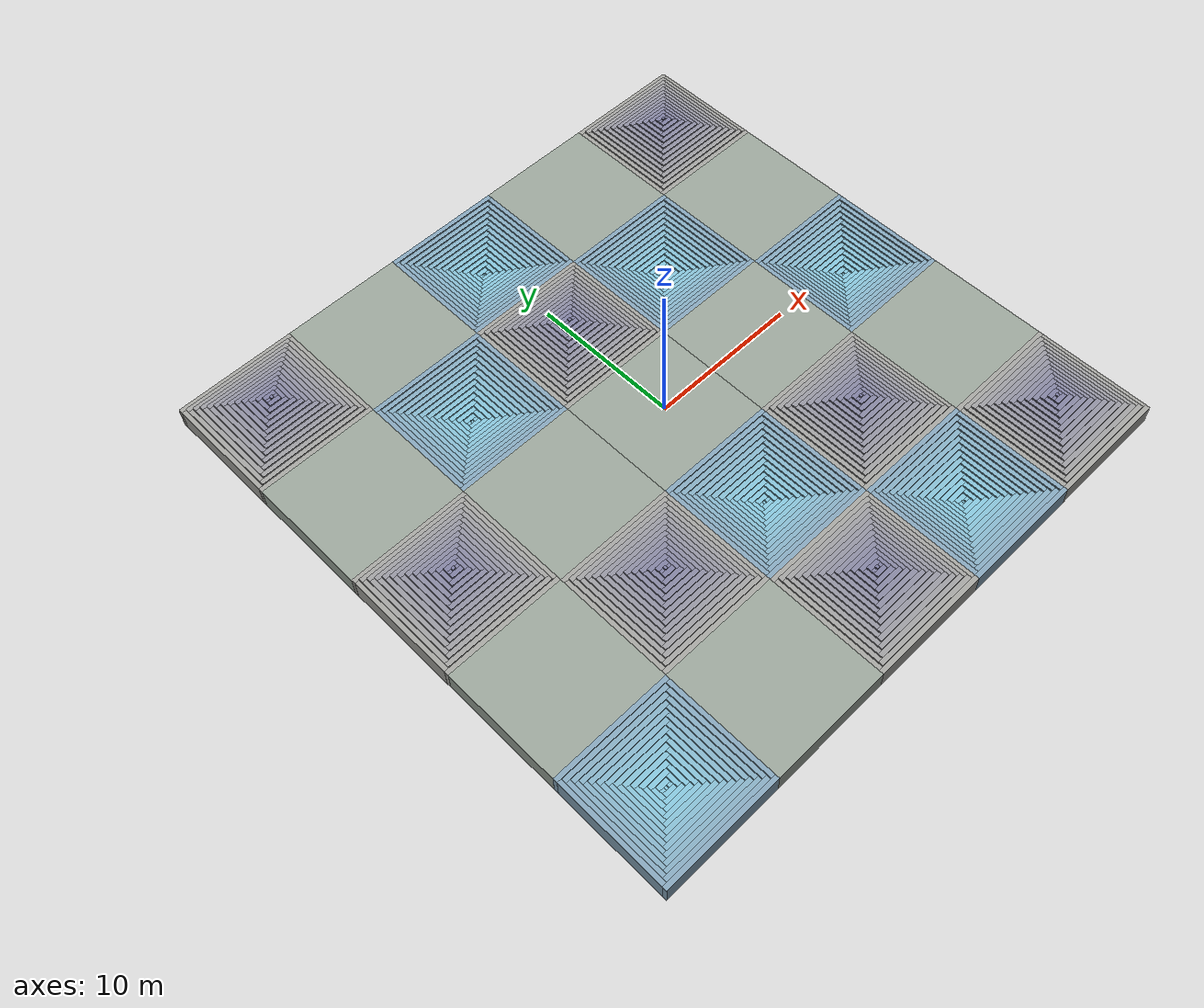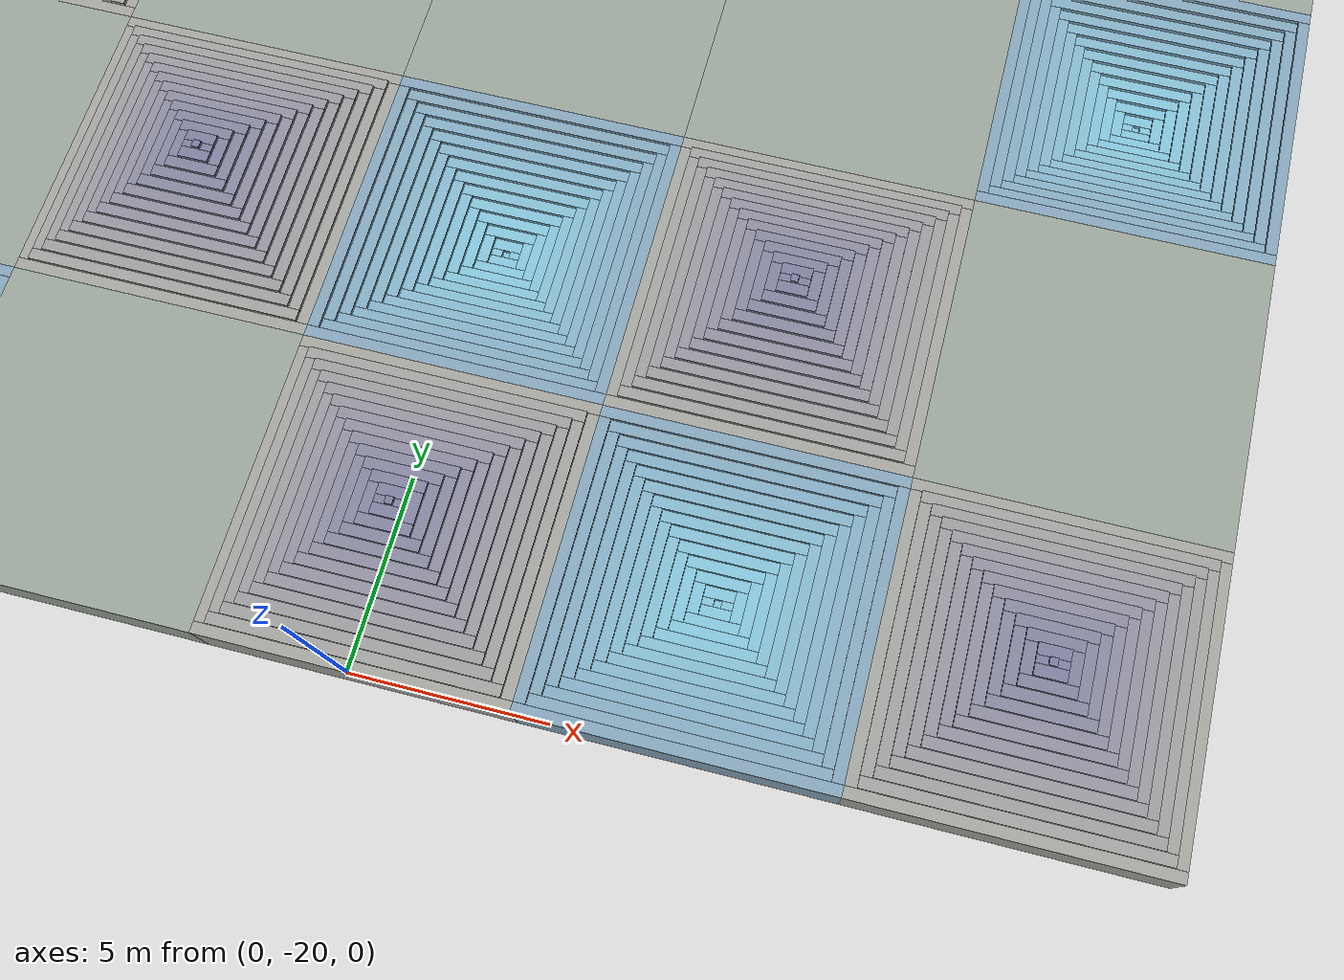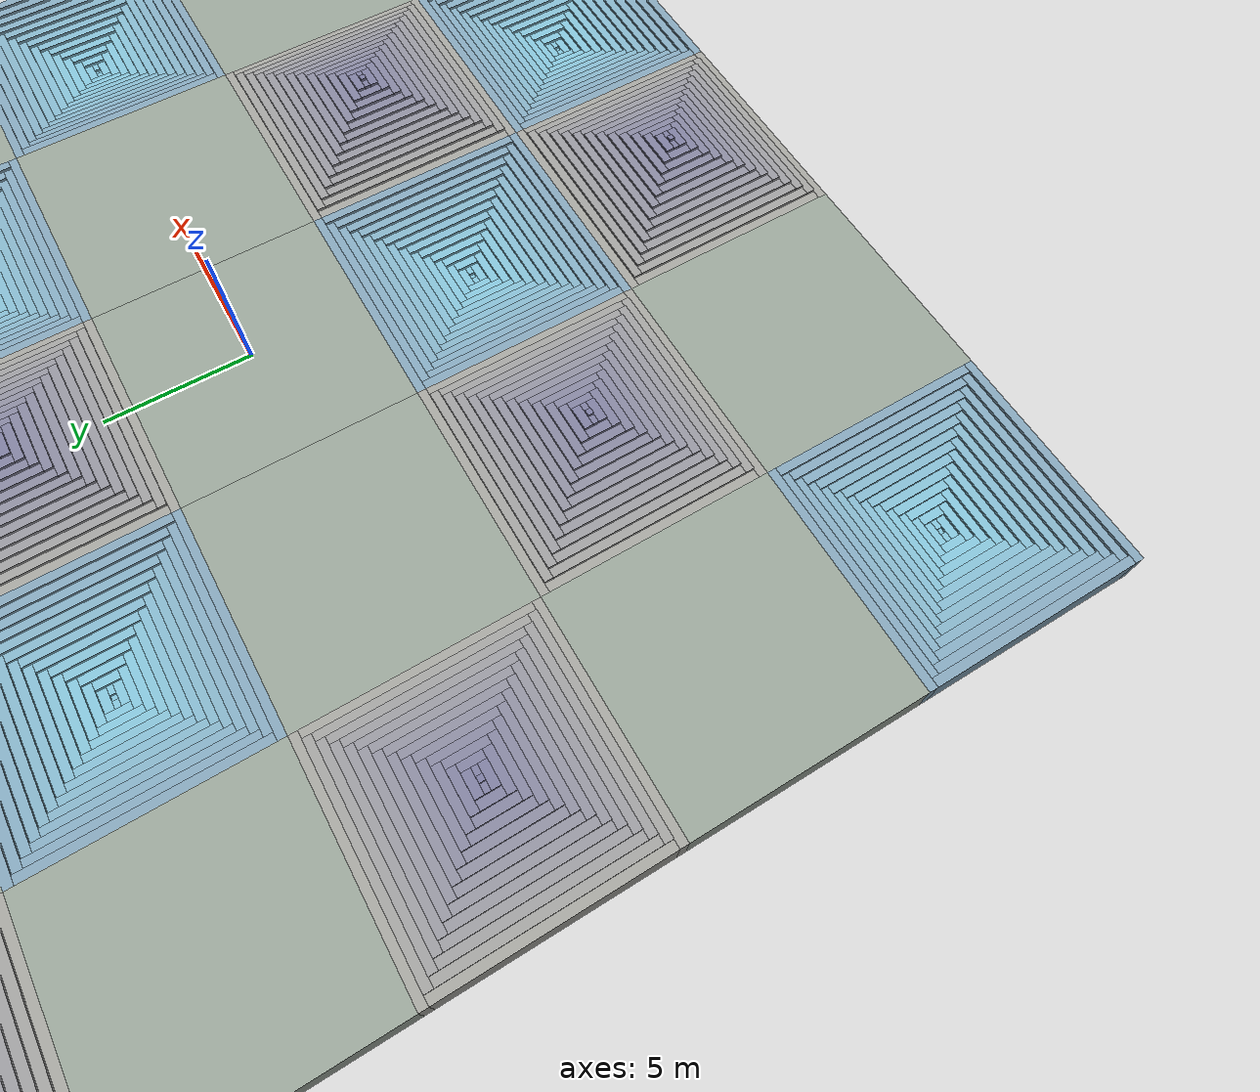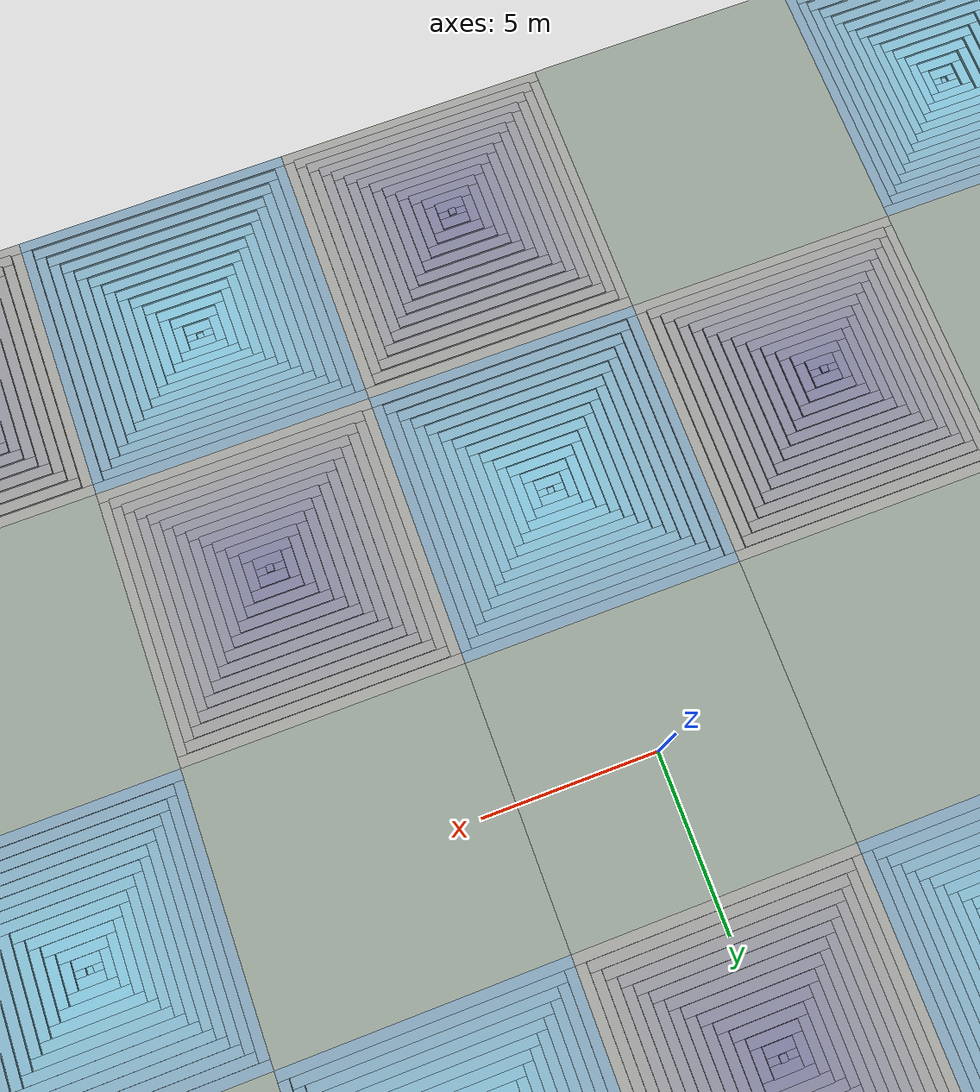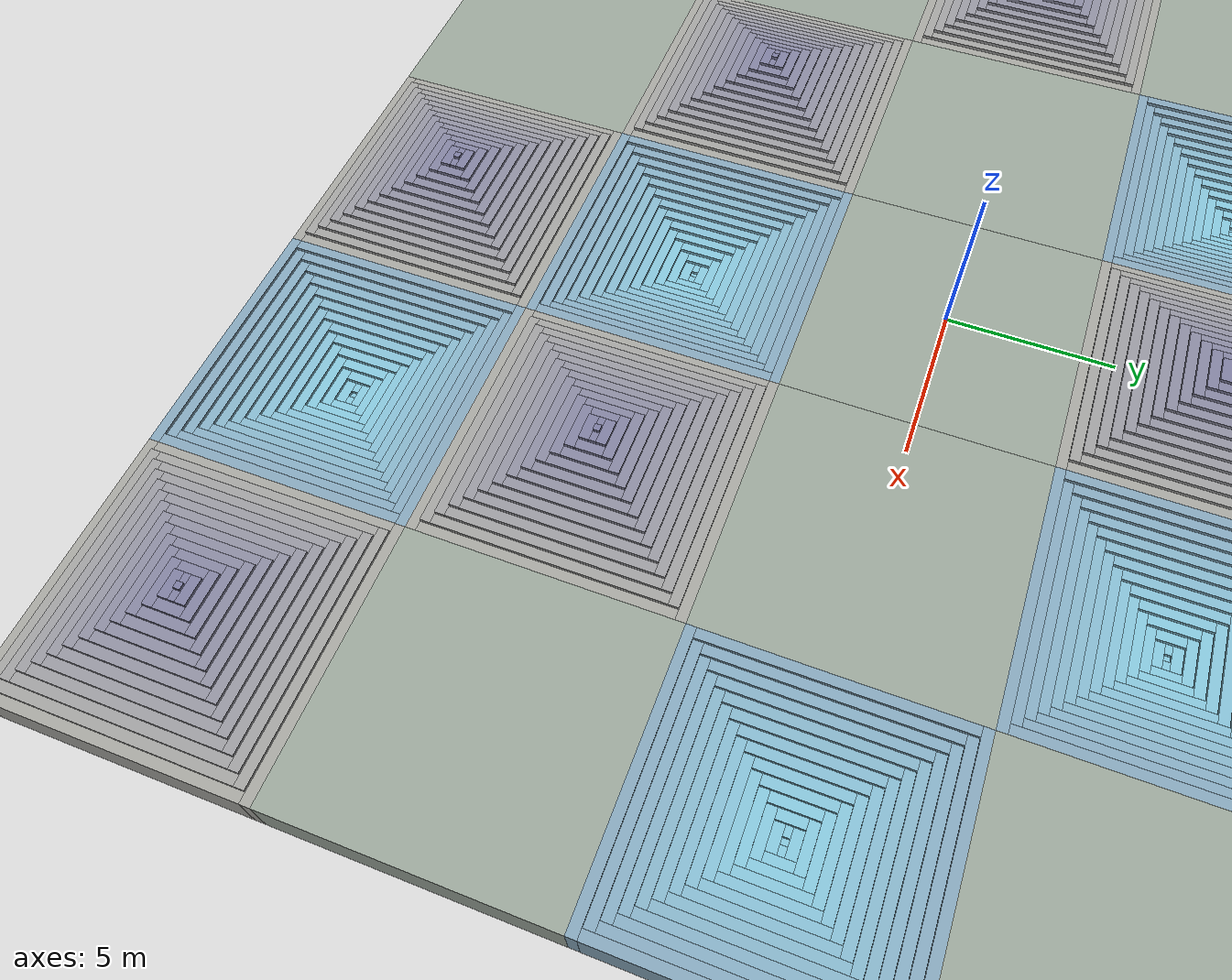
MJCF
<mujoco>
  <worldbody>
    <geom name="tile_r0_c0_up_00_north" type="box" pos="-16.0000 19.8500 -0.7000" size="4.0000 0.1500 0.7000" rgba="0.620 0.620 0.600 1.0" group="2" contype="1" conaffinity="1" friction="0.8 0.02 0.01" />
    <geom name="tile_r0_c0_up_00_south" type="box" pos="-16.0000 12.1500 -0.7000" size="4.0000 0.1500 0.7000" rgba="0.620 0.620 0.600 1.0" group="2" contype="1" conaffinity="1" friction="0.8 0.02 0.01" />
    <geom name="tile_r0_c0_up_00_west" type="box" pos="-19.8500 16.0000 -0.7000" size="0.1500 3.7000 0.7000" rgba="0.620 0.620 0.600 1.0" group="2" contype="1" conaffinity="1" friction="0.8 0.02 0.01" />
    <geom name="tile_r0_c0_up_00_east" type="box" pos="-12.1500 16.0000 -0.7000" size="0.1500 3.7000 0.7000" rgba="0.620 0.620 0.600 1.0" group="2" contype="1" conaffinity="1" friction="0.8 0.02 0.01" />
    <geom name="tile_r0_c0_up_01_north" type="box" pos="-16.0000 19.5500 -0.6500" size="3.7000 0.1500 0.7500" rgba="0.608 0.608 0.600 1.0" group="2" contype="1" conaffinity="1" friction="0.8 0.02 0.01" />
    <geom name="tile_r0_c0_up_01_south" type="box" pos="-16.0000 12.4500 -0.6500" size="3.7000 0.1500 0.7500" rgba="0.608 0.608 0.600 1.0" group="2" contype="1" conaffinity="1" friction="0.8 0.02 0.01" />
    <geom name="tile_r0_c0_up_01_west" type="box" pos="-19.5500 16.0000 -0.6500" size="0.1500 3.4000 0.7500" rgba="0.608 0.608 0.600 1.0" group="2" contype="1" conaffinity="1" friction="0.8 0.02 0.01" />
    <geom name="tile_r0_c0_up_01_east" type="box" pos="-12.4500 16.0000 -0.6500" size="0.1500 3.4000 0.7500" rgba="0.608 0.608 0.600 1.0" group="2" contype="1" conaffinity="1" friction="0.8 0.02 0.01" />
    <geom name="tile_r0_c0_up_02_north" type="box" pos="-16.0000 19.2500 -0.6000" size="3.4000 0.1500 0.8000" rgba="0.596 0.596 0.600 1.0" group="2" contype="1" conaffinity="1" friction="0.8 0.02 0.01" />
    <geom name="tile_r0_c0_up_02_south" type="box" pos="-16.0000 12.7500 -0.6000" size="3.4000 0.1500 0.8000" rgba="0.596 0.596 0.600 1.0" group="2" contype="1" conaffinity="1" friction="0.8 0.02 0.01" />
    <geom name="tile_r0_c0_up_02_west" type="box" pos="-19.2500 16.0000 -0.6000" size="0.1500 3.1000 0.8000" rgba="0.596 0.596 0.600 1.0" group="2" contype="1" conaffinity="1" friction="0.8 0.02 0.01" />
    <geom name="tile_r0_c0_up_02_east" type="box" pos="-12.7500 16.0000 -0.6000" size="0.1500 3.1000 0.8000" rgba="0.596 0.596 0.600 1.0" group="2" contype="1" conaffinity="1" friction="0.8 0.02 0.01" />
    <geom name="tile_r0_c0_up_03_north" type="box" pos="-16.0000 18.9500 -0.5500" size="3.1000 0.1500 0.8500" rgba="0.584 0.584 0.600 1.0" group="2" contype="1" conaffinity="1" friction="0.8 0.02 0.01" />
    <geom name="tile_r0_c0_up_03_south" type="box" pos="-16.0000 13.0500 -0.5500" size="3.1000 0.1500 0.8500" rgba="0.584 0.584 0.600 1.0" group="2" contype="1" conaffinity="1" friction="0.8 0.02 0.01" />
    <geom name="tile_r0_c0_up_03_west" type="box" pos="-18.9500 16.0000 -0.5500" size="0.1500 2.8000 0.8500" rgba="0.584 0.584 0.600 1.0" group="2" contype="1" conaffinity="1" friction="0.8 0.02 0.01" />
    <geom name="tile_r0_c0_up_03_east" type="box" pos="-13.0500 16.0000 -0.5500" size="0.1500 2.8000 0.8500" rgba="0.584 0.584 0.600 1.0" group="2" contype="1" conaffinity="1" friction="0.8 0.02 0.01" />
    <geom name="tile_r0_c0_up_04_north" type="box" pos="-16.0000 18.6500 -0.5000" size="2.8000 0.1500 0.9000" rgba="0.572 0.572 0.600 1.0" group="2" contype="1" conaffinity="1" friction="0.8 0.02 0.01" />
    <geom name="tile_r0_c0_up_04_south" type="box" pos="-16.0000 13.3500 -0.5000" size="2.8000 0.1500 0.9000" rgba="0.572 0.572 0.600 1.0" group="2" contype="1" conaffinity="1" friction="0.8 0.02 0.01" />
    <geom name="tile_r0_c0_up_04_west" type="box" pos="-18.6500 16.0000 -0.5000" size="0.1500 2.5000 0.9000" rgba="0.572 0.572 0.600 1.0" group="2" contype="1" conaffinity="1" friction="0.8 0.02 0.01" />
    <geom name="tile_r0_c0_up_04_east" type="box" pos="-13.3500 16.0000 -0.5000" size="0.1500 2.5000 0.9000" rgba="0.572 0.572 0.600 1.0" group="2" contype="1" conaffinity="1" friction="0.8 0.02 0.01" />
    <geom name="tile_r0_c0_up_05_north" type="box" pos="-16.0000 18.3500 -0.4500" size="2.5000 0.1500 0.9500" rgba="0.560 0.560 0.600 1.0" group="2" contype="1" conaffinity="1" friction="0.8 0.02 0.01" />
    <geom name="tile_r0_c0_up_05_south" type="box" pos="-16.0000 13.6500 -0.4500" size="2.5000 0.1500 0.9500" rgba="0.560 0.560 0.600 1.0" group="2" contype="1" conaffinity="1" friction="0.8 0.02 0.01" />
    <geom name="tile_r0_c0_up_05_west" type="box" pos="-18.3500 16.0000 -0.4500" size="0.1500 2.2000 0.9500" rgba="0.560 0.560 0.600 1.0" group="2" contype="1" conaffinity="1" friction="0.8 0.02 0.01" />
    <geom name="tile_r0_c0_up_05_east" type="box" pos="-13.6500 16.0000 -0.4500" size="0.1500 2.2000 0.9500" rgba="0.560 0.560 0.600 1.0" group="2" contype="1" conaffinity="1" friction="0.8 0.02 0.01" />
    <geom name="tile_r0_c0_up_06_north" type="box" pos="-16.0000 18.0500 -0.4000" size="2.2000 0.1500 1.0000" rgba="0.548 0.548 0.600 1.0" group="2" contype="1" conaffinity="1" friction="0.8 0.02 0.01" />
    <geom name="tile_r0_c0_up_06_south" type="box" pos="-16.0000 13.9500 -0.4000" size="2.2000 0.1500 1.0000" rgba="0.548 0.548 0.600 1.0" group="2" contype="1" conaffinity="1" friction="0.8 0.02 0.01" />
    <geom name="tile_r0_c0_up_06_west" type="box" pos="-18.0500 16.0000 -0.4000" size="0.1500 1.9000 1.0000" rgba="0.548 0.548 0.600 1.0" group="2" contype="1" conaffinity="1" friction="0.8 0.02 0.01" />
    <geom name="tile_r0_c0_up_06_east" type="box" pos="-13.9500 16.0000 -0.4000" size="0.1500 1.9000 1.0000" rgba="0.548 0.548 0.600 1.0" group="2" contype="1" conaffinity="1" friction="0.8 0.02 0.01" />
    <geom name="tile_r0_c0_up_07_north" type="box" pos="-16.0000 17.7500 -0.3500" size="1.9000 0.1500 1.0500" rgba="0.536 0.536 0.600 1.0" group="2" contype="1" conaffinity="1" friction="0.8 0.02 0.01" />
    <geom name="tile_r0_c0_up_07_south" type="box" pos="-16.0000 14.2500 -0.3500" size="1.9000 0.1500 1.0500" rgba="0.536 0.536 0.600 1.0" group="2" contype="1" conaffinity="1" friction="0.8 0.02 0.01" />
    <geom name="tile_r0_c0_up_07_west" type="box" pos="-17.7500 16.0000 -0.3500" size="0.1500 1.6000 1.0500" rgba="0.536 0.536 0.600 1.0" group="2" contype="1" conaffinity="1" friction="0.8 0.02 0.01" />
    <geom name="tile_r0_c0_up_07_east" type="box" pos="-14.2500 16.0000 -0.3500" size="0.1500 1.6000 1.0500" rgba="0.536 0.536 0.600 1.0" group="2" contype="1" conaffinity="1" friction="0.8 0.02 0.01" />
    <geom name="tile_r0_c0_up_08_north" type="box" pos="-16.0000 17.4500 -0.3000" size="1.6000 0.1500 1.1000" rgba="0.524 0.524 0.600 1.0" group="2" contype="1" conaffinity="1" friction="0.8 0.02 0.01" />
    <geom name="tile_r0_c0_up_08_south" type="box" pos="-16.0000 14.5500 -0.3000" size="1.6000 0.1500 1.1000" rgba="0.524 0.524 0.600 1.0" group="2" contype="1" conaffinity="1" friction="0.8 0.02 0.01" />
    <geom name="tile_r0_c0_up_08_west" type="box" pos="-17.4500 16.0000 -0.3000" size="0.1500 1.3000 1.1000" rgba="0.524 0.524 0.600 1.0" group="2" contype="1" conaffinity="1" friction="0.8 0.02 0.01" />
    <geom name="tile_r0_c0_up_08_east" type="box" pos="-14.5500 16.0000 -0.3000" size="0.1500 1.3000 1.1000" rgba="0.524 0.524 0.600 1.0" group="2" contype="1" conaffinity="1" friction="0.8 0.02 0.01" />
    <geom name="tile_r0_c0_up_09_north" type="box" pos="-16.0000 17.1500 -0.2500" size="1.3000 0.1500 1.1500" rgba="0.512 0.512 0.600 1.0" group="2" contype="1" conaffinity="1" friction="0.8 0.02 0.01" />
    <geom name="tile_r0_c0_up_09_south" type="box" pos="-16.0000 14.8500 -0.2500" size="1.3000 0.1500 1.1500" rgba="0.512 0.512 0.600 1.0" group="2" contype="1" conaffinity="1" friction="0.8 0.02 0.01" />
    <geom name="tile_r0_c0_up_09_west" type="box" pos="-17.1500 16.0000 -0.2500" size="0.1500 1.0000 1.1500" rgba="0.512 0.512 0.600 1.0" group="2" contype="1" conaffinity="1" friction="0.8 0.02 0.01" />
    <geom name="tile_r0_c0_up_09_east" type="box" pos="-14.8500 16.0000 -0.2500" size="0.1500 1.0000 1.1500" rgba="0.512 0.512 0.600 1.0" group="2" contype="1" conaffinity="1" friction="0.8 0.02 0.01" />
    <geom name="tile_r0_c0_up_10_north" type="box" pos="-16.0000 16.8500 -0.2000" size="1.0000 0.1500 1.2000" rgba="0.500 0.500 0.600 1.0" group="2" contype="1" conaffinity="1" friction="0.8 0.02 0.01" />
    <geom name="tile_r0_c0_up_10_south" type="box" pos="-16.0000 15.1500 -0.2000" size="1.0000 0.1500 1.2000" rgba="0.500 0.500 0.600 1.0" group="2" contype="1" conaffinity="1" friction="0.8 0.02 0.01" />
    <geom name="tile_r0_c0_up_10_west" type="box" pos="-16.8500 16.0000 -0.2000" size="0.1500 0.7000 1.2000" rgba="0.500 0.500 0.600 1.0" group="2" contype="1" conaffinity="1" friction="0.8 0.02 0.01" />
    <geom name="tile_r0_c0_up_10_east" type="box" pos="-15.1500 16.0000 -0.2000" size="0.1500 0.7000 1.2000" rgba="0.500 0.500 0.600 1.0" group="2" contype="1" conaffinity="1" friction="0.8 0.02 0.01" />
    <geom name="tile_r0_c0_up_11_north" type="box" pos="-16.0000 16.5500 -0.1500" size="0.7000 0.1500 1.2500" rgba="0.488 0.488 0.600 1.0" group="2" contype="1" conaffinity="1" friction="0.8 0.02 0.01" />
    <geom name="tile_r0_c0_up_11_south" type="box" pos="-16.0000 15.4500 -0.1500" size="0.7000 0.1500 1.2500" rgba="0.488 0.488 0.600 1.0" group="2" contype="1" conaffinity="1" friction="0.8 0.02 0.01" />
    <geom name="tile_r0_c0_up_11_west" type="box" pos="-16.5500 16.0000 -0.1500" size="0.1500 0.4000 1.2500" rgba="0.488 0.488 0.600 1.0" group="2" contype="1" conaffinity="1" friction="0.8 0.02 0.01" />
    <geom name="tile_r0_c0_up_11_east" type="box" pos="-15.4500 16.0000 -0.1500" size="0.1500 0.4000 1.2500" rgba="0.488 0.488 0.600 1.0" group="2" contype="1" conaffinity="1" friction="0.8 0.02 0.01" />
    <geom name="tile_r0_c0_up_12_north" type="box" pos="-16.0000 16.2500 -0.1000" size="0.4000 0.1500 1.3000" rgba="0.476 0.476 0.600 1.0" group="2" contype="1" conaffinity="1" friction="0.8 0.02 0.01" />
    <geom name="tile_r0_c0_up_12_south" type="box" pos="-16.0000 15.7500 -0.1000" size="0.4000 0.1500 1.3000" rgba="0.476 0.476 0.600 1.0" group="2" contype="1" conaffinity="1" friction="0.8 0.02 0.01" />
    <geom name="tile_r0_c0_up_12_west" type="box" pos="-16.2500 16.0000 -0.1000" size="0.1500 0.1000 1.3000" rgba="0.476 0.476 0.600 1.0" group="2" contype="1" conaffinity="1" friction="0.8 0.02 0.01" />
    <geom name="tile_r0_c0_up_12_east" type="box" pos="-15.7500 16.0000 -0.1000" size="0.1500 0.1000 1.3000" rgba="0.476 0.476 0.600 1.0" group="2" contype="1" conaffinity="1" friction="0.8 0.02 0.01" />
    <geom name="tile_r0_c0_up_13_center" type="box" pos="-16.0000 16.0000 -0.0500" size="0.1000 0.1000 1.3500" rgba="0.464 0.464 0.600 1.0" group="2" contype="1" conaffinity="1" friction="0.8 0.02 0.01" />
    <geom name="tile_r0_c1_flat" type="box" pos="-8.0000 16.0000 -0.7000" size="4.0000 4.0000 0.7000" rgba="0.580 0.620 0.580 1.0" group="2" contype="1" conaffinity="1" friction="0.8 0.02 0.01" />
    <geom name="tile_r0_c2_down_00_north" type="box" pos="0.0000 19.8500 -0.7000" size="4.0000 0.1500 0.7000" rgba="0.500 0.620 0.700 1.0" group="2" contype="1" conaffinity="1" friction="0.8 0.02 0.01" />
    <geom name="tile_r0_c2_down_00_south" type="box" pos="0.0000 12.1500 -0.7000" size="4.0000 0.1500 0.7000" rgba="0.500 0.620 0.700 1.0" group="2" contype="1" conaffinity="1" friction="0.8 0.02 0.01" />
    <geom name="tile_r0_c2_down_00_west" type="box" pos="-3.8500 16.0000 -0.7000" size="0.1500 3.7000 0.7000" rgba="0.500 0.620 0.700 1.0" group="2" contype="1" conaffinity="1" friction="0.8 0.02 0.01" />
    <geom name="tile_r0_c2_down_00_east" type="box" pos="3.8500 16.0000 -0.7000" size="0.1500 3.7000 0.7000" rgba="0.500 0.620 0.700 1.0" group="2" contype="1" conaffinity="1" friction="0.8 0.02 0.01" />
    <geom name="tile_r0_c2_down_01_north" type="box" pos="0.0000 19.5500 -0.7500" size="3.7000 0.1500 0.6500" rgba="0.500 0.632 0.712 1.0" group="2" contype="1" conaffinity="1" friction="0.8 0.02 0.01" />
    <geom name="tile_r0_c2_down_01_south" type="box" pos="0.0000 12.4500 -0.7500" size="3.7000 0.1500 0.6500" rgba="0.500 0.632 0.712 1.0" group="2" contype="1" conaffinity="1" friction="0.8 0.02 0.01" />
    <geom name="tile_r0_c2_down_01_west" type="box" pos="-3.5500 16.0000 -0.7500" size="0.1500 3.4000 0.6500" rgba="0.500 0.632 0.712 1.0" group="2" contype="1" conaffinity="1" friction="0.8 0.02 0.01" />
    <geom name="tile_r0_c2_down_01_east" type="box" pos="3.5500 16.0000 -0.7500" size="0.1500 3.4000 0.6500" rgba="0.500 0.632 0.712 1.0" group="2" contype="1" conaffinity="1" friction="0.8 0.02 0.01" />
    <geom name="tile_r0_c2_down_02_north" type="box" pos="0.0000 19.2500 -0.8000" size="3.4000 0.1500 0.6000" rgba="0.500 0.644 0.724 1.0" group="2" contype="1" conaffinity="1" friction="0.8 0.02 0.01" />
    <geom name="tile_r0_c2_down_02_south" type="box" pos="0.0000 12.7500 -0.8000" size="3.4000 0.1500 0.6000" rgba="0.500 0.644 0.724 1.0" group="2" contype="1" conaffinity="1" friction="0.8 0.02 0.01" />
    <geom name="tile_r0_c2_down_02_west" type="box" pos="-3.2500 16.0000 -0.8000" size="0.1500 3.1000 0.6000" rgba="0.500 0.644 0.724 1.0" group="2" contype="1" conaffinity="1" friction="0.8 0.02 0.01" />
    <geom name="tile_r0_c2_down_02_east" type="box" pos="3.2500 16.0000 -0.8000" size="0.1500 3.1000 0.6000" rgba="0.500 0.644 0.724 1.0" group="2" contype="1" conaffinity="1" friction="0.8 0.02 0.01" />
    <geom name="tile_r0_c2_down_03_north" type="box" pos="0.0000 18.9500 -0.8500" size="3.1000 0.1500 0.5500" rgba="0.500 0.656 0.736 1.0" group="2" contype="1" conaffinity="1" friction="0.8 0.02 0.01" />
    <geom name="tile_r0_c2_down_03_south" type="box" pos="0.0000 13.0500 -0.8500" size="3.1000 0.1500 0.5500" rgba="0.500 0.656 0.736 1.0" group="2" contype="1" conaffinity="1" friction="0.8 0.02 0.01" />
    <geom name="tile_r0_c2_down_03_west" type="box" pos="-2.9500 16.0000 -0.8500" size="0.1500 2.8000 0.5500" rgba="0.500 0.656 0.736 1.0" group="2" contype="1" conaffinity="1" friction="0.8 0.02 0.01" />
    <geom name="tile_r0_c2_down_03_east" type="box" pos="2.9500 16.0000 -0.8500" size="0.1500 2.8000 0.5500" rgba="0.500 0.656 0.736 1.0" group="2" contype="1" conaffinity="1" friction="0.8 0.02 0.01" />
    <geom name="tile_r0_c2_down_04_north" type="box" pos="0.0000 18.6500 -0.9000" size="2.8000 0.1500 0.5000" rgba="0.500 0.668 0.748 1.0" group="2" contype="1" conaffinity="1" friction="0.8 0.02 0.01" />
    <geom name="tile_r0_c2_down_04_south" type="box" pos="0.0000 13.3500 -0.9000" size="2.8000 0.1500 0.5000" rgba="0.500 0.668 0.748 1.0" group="2" contype="1" conaffinity="1" friction="0.8 0.02 0.01" />
    <geom name="tile_r0_c2_down_04_west" type="box" pos="-2.6500 16.0000 -0.9000" size="0.1500 2.5000 0.5000" rgba="0.500 0.668 0.748 1.0" group="2" contype="1" conaffinity="1" friction="0.8 0.02 0.01" />
    <geom name="tile_r0_c2_down_04_east" type="box" pos="2.6500 16.0000 -0.9000" size="0.1500 2.5000 0.5000" rgba="0.500 0.668 0.748 1.0" group="2" contype="1" conaffinity="1" friction="0.8 0.02 0.01" />
    <geom name="tile_r0_c2_down_05_north" type="box" pos="0.0000 18.3500 -0.9500" size="2.5000 0.1500 0.4500" rgba="0.500 0.680 0.760 1.0" group="2" contype="1" conaffinity="1" friction="0.8 0.02 0.01" />
    <geom name="tile_r0_c2_down_05_south" type="box" pos="0.0000 13.6500 -0.9500" size="2.5000 0.1500 0.4500" rgba="0.500 0.680 0.760 1.0" group="2" contype="1" conaffinity="1" friction="0.8 0.02 0.01" />
    <geom name="tile_r0_c2_down_05_west" type="box" pos="-2.3500 16.0000 -0.9500" size="0.1500 2.2000 0.4500" rgba="0.500 0.680 0.760 1.0" group="2" contype="1" conaffinity="1" friction="0.8 0.02 0.01" />
    <geom name="tile_r0_c2_down_05_east" type="box" pos="2.3500 16.0000 -0.9500" size="0.1500 2.2000 0.4500" rgba="0.500 0.680 0.760 1.0" group="2" contype="1" conaffinity="1" friction="0.8 0.02 0.01" />
    <geom name="tile_r0_c2_down_06_north" type="box" pos="0.0000 18.0500 -1.0000" size="2.2000 0.1500 0.4000" rgba="0.500 0.692 0.772 1.0" group="2" contype="1" conaffinity="1" friction="0.8 0.02 0.01" />
    <geom name="tile_r0_c2_down_06_south" type="box" pos="0.0000 13.9500 -1.0000" size="2.2000 0.1500 0.4000" rgba="0.500 0.692 0.772 1.0" group="2" contype="1" conaffinity="1" friction="0.8 0.02 0.01" />
    <geom name="tile_r0_c2_down_06_west" type="box" pos="-2.0500 16.0000 -1.0000" size="0.1500 1.9000 0.4000" rgba="0.500 0.692 0.772 1.0" group="2" contype="1" conaffinity="1" friction="0.8 0.02 0.01" />
    <geom name="tile_r0_c2_down_06_east" type="box" pos="2.0500 16.0000 -1.0000" size="0.1500 1.9000 0.4000" rgba="0.500 0.692 0.772 1.0" group="2" contype="1" conaffinity="1" friction="0.8 0.02 0.01" />
    <geom name="tile_r0_c2_down_07_north" type="box" pos="0.0000 17.7500 -1.0500" size="1.9000 0.1500 0.3500" rgba="0.500 0.704 0.784 1.0" group="2" contype="1" conaffinity="1" friction="0.8 0.02 0.01" />
    <geom name="tile_r0_c2_down_07_south" type="box" pos="0.0000 14.2500 -1.0500" size="1.9000 0.1500 0.3500" rgba="0.500 0.704 0.784 1.0" group="2" contype="1" conaffinity="1" friction="0.8 0.02 0.01" />
    <geom name="tile_r0_c2_down_07_west" type="box" pos="-1.7500 16.0000 -1.0500" size="0.1500 1.6000 0.3500" rgba="0.500 0.704 0.784 1.0" group="2" contype="1" conaffinity="1" friction="0.8 0.02 0.01" />
    <geom name="tile_r0_c2_down_07_east" type="box" pos="1.7500 16.0000 -1.0500" size="0.1500 1.6000 0.3500" rgba="0.500 0.704 0.784 1.0" group="2" contype="1" conaffinity="1" friction="0.8 0.02 0.01" />
    <geom name="tile_r0_c2_down_08_north" type="box" pos="0.0000 17.4500 -1.1000" size="1.6000 0.1500 0.3000" rgba="0.500 0.716 0.796 1.0" group="2" contype="1" conaffinity="1" friction="0.8 0.02 0.01" />
    <geom name="tile_r0_c2_down_08_south" type="box" pos="0.0000 14.5500 -1.1000" size="1.6000 0.1500 0.3000" rgba="0.500 0.716 0.796 1.0" group="2" contype="1" conaffinity="1" friction="0.8 0.02 0.01" />
    <geom name="tile_r0_c2_down_08_west" type="box" pos="-1.4500 16.0000 -1.1000" size="0.1500 1.3000 0.3000" rgba="0.500 0.716 0.796 1.0" group="2" contype="1" conaffinity="1" friction="0.8 0.02 0.01" />
    <geom name="tile_r0_c2_down_08_east" type="box" pos="1.4500 16.0000 -1.1000" size="0.1500 1.3000 0.3000" rgba="0.500 0.716 0.796 1.0" group="2" contype="1" conaffinity="1" friction="0.8 0.02 0.01" />
    <geom name="tile_r0_c2_down_09_north" type="box" pos="0.0000 17.1500 -1.1500" size="1.3000 0.1500 0.2500" rgba="0.500 0.728 0.808 1.0" group="2" contype="1" conaffinity="1" friction="0.8 0.02 0.01" />
    <geom name="tile_r0_c2_down_09_south" type="box" pos="0.0000 14.8500 -1.1500" size="1.3000 0.1500 0.2500" rgba="0.500 0.728 0.808 1.0" group="2" contype="1" conaffinity="1" friction="0.8 0.02 0.01" />
    <geom name="tile_r0_c2_down_09_west" type="box" pos="-1.1500 16.0000 -1.1500" size="0.1500 1.0000 0.2500" rgba="0.500 0.728 0.808 1.0" group="2" contype="1" conaffinity="1" friction="0.8 0.02 0.01" />
    <geom name="tile_r0_c2_down_09_east" type="box" pos="1.1500 16.0000 -1.1500" size="0.1500 1.0000 0.2500" rgba="0.500 0.728 0.808 1.0" group="2" contype="1" conaffinity="1" friction="0.8 0.02 0.01" />
    <geom name="tile_r0_c2_down_10_north" type="box" pos="0.0000 16.8500 -1.2000" size="1.0000 0.1500 0.2000" rgba="0.500 0.740 0.820 1.0" group="2" contype="1" conaffinity="1" friction="0.8 0.02 0.01" />
    <geom name="tile_r0_c2_down_10_south" type="box" pos="0.0000 15.1500 -1.2000" size="1.0000 0.1500 0.2000" rgba="0.500 0.740 0.820 1.0" group="2" contype="1" conaffinity="1" friction="0.8 0.02 0.01" />
    <geom name="tile_r0_c2_down_10_west" type="box" pos="-0.8500 16.0000 -1.2000" size="0.1500 0.7000 0.2000" rgba="0.500 0.740 0.820 1.0" group="2" contype="1" conaffinity="1" friction="0.8 0.02 0.01" />
    <geom name="tile_r0_c2_down_10_east" type="box" pos="0.8500 16.0000 -1.2000" size="0.1500 0.7000 0.2000" rgba="0.500 0.740 0.820 1.0" group="2" contype="1" conaffinity="1" friction="0.8 0.02 0.01" />
    <geom name="tile_r0_c2_down_11_north" type="box" pos="0.0000 16.5500 -1.2500" size="0.7000 0.1500 0.1500" rgba="0.500 0.740 0.820 1.0" group="2" contype="1" conaffinity="1" friction="0.8 0.02 0.01" />
    <geom name="tile_r0_c2_down_11_south" type="box" pos="0.0000 15.4500 -1.2500" size="0.7000 0.1500 0.1500" rgba="0.500 0.740 0.820 1.0" group="2" contype="1" conaffinity="1" friction="0.8 0.02 0.01" />
    <geom name="tile_r0_c2_down_11_west" type="box" pos="-0.5500 16.0000 -1.2500" size="0.1500 0.4000 0.1500" rgba="0.500 0.740 0.820 1.0" group="2" contype="1" conaffinity="1" friction="0.8 0.02 0.01" />
    <geom name="tile_r0_c2_down_11_east" type="box" pos="0.5500 16.0000 -1.2500" size="0.1500 0.4000 0.1500" rgba="0.500 0.740 0.820 1.0" group="2" contype="1" conaffinity="1" friction="0.8 0.02 0.01" />
    <geom name="tile_r0_c2_down_12_north" type="box" pos="0.0000 16.2500 -1.3000" size="0.4000 0.1500 0.1000" rgba="0.500 0.740 0.820 1.0" group="2" contype="1" conaffinity="1" friction="0.8 0.02 0.01" />
    <geom name="tile_r0_c2_down_12_south" type="box" pos="0.0000 15.7500 -1.3000" size="0.4000 0.1500 0.1000" rgba="0.500 0.740 0.820 1.0" group="2" contype="1" conaffinity="1" friction="0.8 0.02 0.01" />
    <geom name="tile_r0_c2_down_12_west" type="box" pos="-0.2500 16.0000 -1.3000" size="0.1500 0.1000 0.1000" rgba="0.500 0.740 0.820 1.0" group="2" contype="1" conaffinity="1" friction="0.8 0.02 0.01" />
    <geom name="tile_r0_c2_down_12_east" type="box" pos="0.2500 16.0000 -1.3000" size="0.1500 0.1000 0.1000" rgba="0.500 0.740 0.820 1.0" group="2" contype="1" conaffinity="1" friction="0.8 0.02 0.01" />
    <geom name="tile_r0_c2_down_13_center" type="box" pos="0.0000 16.0000 -1.3500" size="0.1000 0.1000 0.0500" rgba="0.500 0.740 0.820 1.0" group="2" contype="1" conaffinity="1" friction="0.8 0.02 0.01" />
    <geom name="tile_r0_c3_flat" type="box" pos="8.0000 16.0000 -0.7000" size="4.0000 4.0000 0.7000" rgba="0.580 0.620 0.580 1.0" group="2" contype="1" conaffinity="1" friction="0.8 0.02 0.01" />
    <geom name="tile_r0_c4_up_00_north" type="box" pos="16.0000 19.8500 -0.7000" size="4.0000 0.1500 0.7000" rgba="0.620 0.620 0.600 1.0" group="2" contype="1" conaffinity="1" friction="0.8 0.02 0.01" />
    <geom name="tile_r0_c4_up_00_south" type="box" pos="16.0000 12.1500 -0.7000" size="4.0000 0.1500 0.7000" rgba="0.620 0.620 0.600 1.0" group="2" contype="1" conaffinity="1" friction="0.8 0.02 0.01" />
    <geom name="tile_r0_c4_up_00_west" type="box" pos="12.1500 16.0000 -0.7000" size="0.1500 3.7000 0.7000" rgba="0.620 0.620 0.600 1.0" group="2" contype="1" conaffinity="1" friction="0.8 0.02 0.01" />
    <geom name="tile_r0_c4_up_00_east" type="box" pos="19.8500 16.0000 -0.7000" size="0.1500 3.7000 0.7000" rgba="0.620 0.620 0.600 1.0" group="2" contype="1" conaffinity="1" friction="0.8 0.02 0.01" />
    <geom name="tile_r0_c4_up_01_north" type="box" pos="16.0000 19.5500 -0.6500" size="3.7000 0.1500 0.7500" rgba="0.608 0.608 0.600 1.0" group="2" contype="1" conaffinity="1" friction="0.8 0.02 0.01" />
    <geom name="tile_r0_c4_up_01_south" type="box" pos="16.0000 12.4500 -0.6500" size="3.7000 0.1500 0.7500" rgba="0.608 0.608 0.600 1.0" group="2" contype="1" conaffinity="1" friction="0.8 0.02 0.01" />
    <geom name="tile_r0_c4_up_01_west" type="box" pos="12.4500 16.0000 -0.6500" size="0.1500 3.4000 0.7500" rgba="0.608 0.608 0.600 1.0" group="2" contype="1" conaffinity="1" friction="0.8 0.02 0.01" />
    <geom name="tile_r0_c4_up_01_east" type="box" pos="19.5500 16.0000 -0.6500" size="0.1500 3.4000 0.7500" rgba="0.608 0.608 0.600 1.0" group="2" contype="1" conaffinity="1" friction="0.8 0.02 0.01" />
    <geom name="tile_r0_c4_up_02_north" type="box" pos="16.0000 19.2500 -0.6000" size="3.4000 0.1500 0.8000" rgba="0.596 0.596 0.600 1.0" group="2" contype="1" conaffinity="1" friction="0.8 0.02 0.01" />
    <geom name="tile_r0_c4_up_02_south" type="box" pos="16.0000 12.7500 -0.6000" size="3.4000 0.1500 0.8000" rgba="0.596 0.596 0.600 1.0" group="2" contype="1" conaffinity="1" friction="0.8 0.02 0.01" />
    <geom name="tile_r0_c4_up_02_west" type="box" pos="12.7500 16.0000 -0.6000" size="0.1500 3.1000 0.8000" rgba="0.596 0.596 0.600 1.0" group="2" contype="1" conaffinity="1" friction="0.8 0.02 0.01" />
    <geom name="tile_r0_c4_up_02_east" type="box" pos="19.2500 16.0000 -0.6000" size="0.1500 3.1000 0.8000" rgba="0.596 0.596 0.600 1.0" group="2" contype="1" conaffinity="1" friction="0.8 0.02 0.01" />
    <geom name="tile_r0_c4_up_03_north" type="box" pos="16.0000 18.9500 -0.5500" size="3.1000 0.1500 0.8500" rgba="0.584 0.584 0.600 1.0" group="2" contype="1" conaffinity="1" friction="0.8 0.02 0.01" />
    <geom name="tile_r0_c4_up_03_south" type="box" pos="16.0000 13.0500 -0.5500" size="3.1000 0.1500 0.8500" rgba="0.584 0.584 0.600 1.0" group="2" contype="1" conaffinity="1" friction="0.8 0.02 0.01" />
    <geom name="tile_r0_c4_up_03_west" type="box" pos="13.0500 16.0000 -0.5500" size="0.1500 2.8000 0.8500" rgba="0.584 0.584 0.600 1.0" group="2" contype="1" conaffinity="1" friction="0.8 0.02 0.01" />
    <geom name="tile_r0_c4_up_03_east" type="box" pos="18.9500 16.0000 -0.5500" size="0.1500 2.8000 0.8500" rgba="0.584 0.584 0.600 1.0" group="2" contype="1" conaffinity="1" friction="0.8 0.02 0.01" />
    <geom name="tile_r0_c4_up_04_north" type="box" pos="16.0000 18.6500 -0.5000" size="2.8000 0.1500 0.9000" rgba="0.572 0.572 0.600 1.0" group="2" contype="1" conaffinity="1" friction="0.8 0.02 0.01" />
    <geom name="tile_r0_c4_up_04_south" type="box" pos="16.0000 13.3500 -0.5000" size="2.8000 0.1500 0.9000" rgba="0.572 0.572 0.600 1.0" group="2" contype="1" conaffinity="1" friction="0.8 0.02 0.01" />
    <geom name="tile_r0_c4_up_04_west" type="box" pos="13.3500 16.0000 -0.5000" size="0.1500 2.5000 0.9000" rgba="0.572 0.572 0.600 1.0" group="2" contype="1" conaffinity="1" friction="0.8 0.02 0.01" />
    <geom name="tile_r0_c4_up_04_east" type="box" pos="18.6500 16.0000 -0.5000" size="0.1500 2.5000 0.9000" rgba="0.572 0.572 0.600 1.0" group="2" contype="1" conaffinity="1" friction="0.8 0.02 0.01" />
    <geom name="tile_r0_c4_up_05_north" type="box" pos="16.0000 18.3500 -0.4500" size="2.5000 0.1500 0.9500" rgba="0.560 0.560 0.600 1.0" group="2" contype="1" conaffinity="1" friction="0.8 0.02 0.01" />
    <geom name="tile_r0_c4_up_05_south" type="box" pos="16.0000 13.6500 -0.4500" size="2.5000 0.1500 0.9500" rgba="0.560 0.560 0.600 1.0" group="2" contype="1" conaffinity="1" friction="0.8 0.02 0.01" />
    <geom name="tile_r0_c4_up_05_west" type="box" pos="13.6500 16.0000 -0.4500" size="0.1500 2.2000 0.9500" rgba="0.560 0.560 0.600 1.0" group="2" contype="1" conaffinity="1" friction="0.8 0.02 0.01" />
    <geom name="tile_r0_c4_up_05_east" type="box" pos="18.3500 16.0000 -0.4500" size="0.1500 2.2000 0.9500" rgba="0.560 0.560 0.600 1.0" group="2" contype="1" conaffinity="1" friction="0.8 0.02 0.01" />
    <geom name="tile_r0_c4_up_06_north" type="box" pos="16.0000 18.0500 -0.4000" size="2.2000 0.1500 1.0000" rgba="0.548 0.548 0.600 1.0" group="2" contype="1" conaffinity="1" friction="0.8 0.02 0.01" />
    <geom name="tile_r0_c4_up_06_south" type="box" pos="16.0000 13.9500 -0.4000" size="2.2000 0.1500 1.0000" rgba="0.548 0.548 0.600 1.0" group="2" contype="1" conaffinity="1" friction="0.8 0.02 0.01" />
    <geom name="tile_r0_c4_up_06_west" type="box" pos="13.9500 16.0000 -0.4000" size="0.1500 1.9000 1.0000" rgba="0.548 0.548 0.600 1.0" group="2" contype="1" conaffinity="1" friction="0.8 0.02 0.01" />
    <geom name="tile_r0_c4_up_06_east" type="box" pos="18.0500 16.0000 -0.4000" size="0.1500 1.9000 1.0000" rgba="0.548 0.548 0.600 1.0" group="2" contype="1" conaffinity="1" friction="0.8 0.02 0.01" />
    <geom name="tile_r0_c4_up_07_north" type="box" pos="16.0000 17.7500 -0.3500" size="1.9000 0.1500 1.0500" rgba="0.536 0.536 0.600 1.0" group="2" contype="1" conaffinity="1" friction="0.8 0.02 0.01" />
    <geom name="tile_r0_c4_up_07_south" type="box" pos="16.0000 14.2500 -0.3500" size="1.9000 0.1500 1.0500" rgba="0.536 0.536 0.600 1.0" group="2" contype="1" conaffinity="1" friction="0.8 0.02 0.01" />
    <geom name="tile_r0_c4_up_07_west" type="box" pos="14.2500 16.0000 -0.3500" size="0.1500 1.6000 1.0500" rgba="0.536 0.536 0.600 1.0" group="2" contype="1" conaffinity="1" friction="0.8 0.02 0.01" />
    <geom name="tile_r0_c4_up_07_east" type="box" pos="17.7500 16.0000 -0.3500" size="0.1500 1.6000 1.0500" rgba="0.536 0.536 0.600 1.0" group="2" contype="1" conaffinity="1" friction="0.8 0.02 0.01" />
    <geom name="tile_r0_c4_up_08_north" type="box" pos="16.0000 17.4500 -0.3000" size="1.6000 0.1500 1.1000" rgba="0.524 0.524 0.600 1.0" group="2" contype="1" conaffinity="1" friction="0.8 0.02 0.01" />
    <geom name="tile_r0_c4_up_08_south" type="box" pos="16.0000 14.5500 -0.3000" size="1.6000 0.1500 1.1000" rgba="0.524 0.524 0.600 1.0" group="2" contype="1" conaffinity="1" friction="0.8 0.02 0.01" />
    <geom name="tile_r0_c4_up_08_west" type="box" pos="14.5500 16.0000 -0.3000" size="0.1500 1.3000 1.1000" rgba="0.524 0.524 0.600 1.0" group="2" contype="1" conaffinity="1" friction="0.8 0.02 0.01" />
    <geom name="tile_r0_c4_up_08_east" type="box" pos="17.4500 16.0000 -0.3000" size="0.1500 1.3000 1.1000" rgba="0.524 0.524 0.600 1.0" group="2" contype="1" conaffinity="1" friction="0.8 0.02 0.01" />
    <geom name="tile_r0_c4_up_09_north" type="box" pos="16.0000 17.1500 -0.2500" size="1.3000 0.1500 1.1500" rgba="0.512 0.512 0.600 1.0" group="2" contype="1" conaffinity="1" friction="0.8 0.02 0.01" />
    <geom name="tile_r0_c4_up_09_south" type="box" pos="16.0000 14.8500 -0.2500" size="1.3000 0.1500 1.1500" rgba="0.512 0.512 0.600 1.0" group="2" contype="1" conaffinity="1" friction="0.8 0.02 0.01" />
    <geom name="tile_r0_c4_up_09_west" type="box" pos="14.8500 16.0000 -0.2500" size="0.1500 1.0000 1.1500" rgba="0.512 0.512 0.600 1.0" group="2" contype="1" conaffinity="1" friction="0.8 0.02 0.01" />
    <geom name="tile_r0_c4_up_09_east" type="box" pos="17.1500 16.0000 -0.2500" size="0.1500 1.0000 1.1500" rgba="0.512 0.512 0.600 1.0" group="2" contype="1" conaffinity="1" friction="0.8 0.02 0.01" />
    <geom name="tile_r0_c4_up_10_north" type="box" pos="16.0000 16.8500 -0.2000" size="1.0000 0.1500 1.2000" rgba="0.500 0.500 0.600 1.0" group="2" contype="1" conaffinity="1" friction="0.8 0.02 0.01" />
    <geom name="tile_r0_c4_up_10_south" type="box" pos="16.0000 15.1500 -0.2000" size="1.0000 0.1500 1.2000" rgba="0.500 0.500 0.600 1.0" group="2" contype="1" conaffinity="1" friction="0.8 0.02 0.01" />
    <geom name="tile_r0_c4_up_10_west" type="box" pos="15.1500 16.0000 -0.2000" size="0.1500 0.7000 1.2000" rgba="0.500 0.500 0.600 1.0" group="2" contype="1" conaffinity="1" friction="0.8 0.02 0.01" />
    <geom name="tile_r0_c4_up_10_east" type="box" pos="16.8500 16.0000 -0.2000" size="0.1500 0.7000 1.2000" rgba="0.500 0.500 0.600 1.0" group="2" contype="1" conaffinity="1" friction="0.8 0.02 0.01" />
    <geom name="tile_r0_c4_up_11_north" type="box" pos="16.0000 16.5500 -0.1500" size="0.7000 0.1500 1.2500" rgba="0.488 0.488 0.600 1.0" group="2" contype="1" conaffinity="1" friction="0.8 0.02 0.01" />
    <geom name="tile_r0_c4_up_11_south" type="box" pos="16.0000 15.4500 -0.1500" size="0.7000 0.1500 1.2500" rgba="0.488 0.488 0.600 1.0" group="2" contype="1" conaffinity="1" friction="0.8 0.02 0.01" />
    <geom name="tile_r0_c4_up_11_west" type="box" pos="15.4500 16.0000 -0.1500" size="0.1500 0.4000 1.2500" rgba="0.488 0.488 0.600 1.0" group="2" contype="1" conaffinity="1" friction="0.8 0.02 0.01" />
    <geom name="tile_r0_c4_up_11_east" type="box" pos="16.5500 16.0000 -0.1500" size="0.1500 0.4000 1.2500" rgba="0.488 0.488 0.600 1.0" group="2" contype="1" conaffinity="1" friction="0.8 0.02 0.01" />
    <geom name="tile_r0_c4_up_12_north" type="box" pos="16.0000 16.2500 -0.1000" size="0.4000 0.1500 1.3000" rgba="0.476 0.476 0.600 1.0" group="2" contype="1" conaffinity="1" friction="0.8 0.02 0.01" />
    <geom name="tile_r0_c4_up_12_south" type="box" pos="16.0000 15.7500 -0.1000" size="0.4000 0.1500 1.3000" rgba="0.476 0.476 0.600 1.0" group="2" contype="1" conaffinity="1" friction="0.8 0.02 0.01" />
    <geom name="tile_r0_c4_up_12_west" type="box" pos="15.7500 16.0000 -0.1000" size="0.1500 0.1000 1.3000" rgba="0.476 0.476 0.600 1.0" group="2" contype="1" conaffinity="1" friction="0.8 0.02 0.01" />
    <geom name="tile_r0_c4_up_12_east" type="box" pos="16.2500 16.0000 -0.1000" size="0.1500 0.1000 1.3000" rgba="0.476 0.476 0.600 1.0" group="2" contype="1" conaffinity="1" friction="0.8 0.02 0.01" />
    <geom name="tile_r0_c4_up_13_center" type="box" pos="16.0000 16.0000 -0.0500" size="0.1000 0.1000 1.3500" rgba="0.464 0.464 0.600 1.0" group="2" contype="1" conaffinity="1" friction="0.8 0.02 0.01" />
    <geom name="tile_r1_c0_flat" type="box" pos="-16.0000 8.0000 -0.7000" size="4.0000 4.0000 0.7000" rgba="0.580 0.620 0.580 1.0" group="2" contype="1" conaffinity="1" friction="0.8 0.02 0.01" />
    <geom name="tile_r1_c1_down_00_north" type="box" pos="-8.0000 11.8500 -0.7000" size="4.0000 0.1500 0.7000" rgba="0.500 0.620 0.700 1.0" group="2" contype="1" conaffinity="1" friction="0.8 0.02 0.01" />
    <geom name="tile_r1_c1_down_00_south" type="box" pos="-8.0000 4.1500 -0.7000" size="4.0000 0.1500 0.7000" rgba="0.500 0.620 0.700 1.0" group="2" contype="1" conaffinity="1" friction="0.8 0.02 0.01" />
    <geom name="tile_r1_c1_down_00_west" type="box" pos="-11.8500 8.0000 -0.7000" size="0.1500 3.7000 0.7000" rgba="0.500 0.620 0.700 1.0" group="2" contype="1" conaffinity="1" friction="0.8 0.02 0.01" />
    <geom name="tile_r1_c1_down_00_east" type="box" pos="-4.1500 8.0000 -0.7000" size="0.1500 3.7000 0.7000" rgba="0.500 0.620 0.700 1.0" group="2" contype="1" conaffinity="1" friction="0.8 0.02 0.01" />
    <geom name="tile_r1_c1_down_01_north" type="box" pos="-8.0000 11.5500 -0.7500" size="3.7000 0.1500 0.6500" rgba="0.500 0.632 0.712 1.0" group="2" contype="1" conaffinity="1" friction="0.8 0.02 0.01" />
    <geom name="tile_r1_c1_down_01_south" type="box" pos="-8.0000 4.4500 -0.7500" size="3.7000 0.1500 0.6500" rgba="0.500 0.632 0.712 1.0" group="2" contype="1" conaffinity="1" friction="0.8 0.02 0.01" />
    <geom name="tile_r1_c1_down_01_west" type="box" pos="-11.5500 8.0000 -0.7500" size="0.1500 3.4000 0.6500" rgba="0.500 0.632 0.712 1.0" group="2" contype="1" conaffinity="1" friction="0.8 0.02 0.01" />
    <geom name="tile_r1_c1_down_01_east" type="box" pos="-4.4500 8.0000 -0.7500" size="0.1500 3.4000 0.6500" rgba="0.500 0.632 0.712 1.0" group="2" contype="1" conaffinity="1" friction="0.8 0.02 0.01" />
    <geom name="tile_r1_c1_down_02_north" type="box" pos="-8.0000 11.2500 -0.8000" size="3.4000 0.1500 0.6000" rgba="0.500 0.644 0.724 1.0" group="2" contype="1" conaffinity="1" friction="0.8 0.02 0.01" />
    <geom name="tile_r1_c1_down_02_south" type="box" pos="-8.0000 4.7500 -0.8000" size="3.4000 0.1500 0.6000" rgba="0.500 0.644 0.724 1.0" group="2" contype="1" conaffinity="1" friction="0.8 0.02 0.01" />
    <geom name="tile_r1_c1_down_02_west" type="box" pos="-11.2500 8.0000 -0.8000" size="0.1500 3.1000 0.6000" rgba="0.500 0.644 0.724 1.0" group="2" contype="1" conaffinity="1" friction="0.8 0.02 0.01" />
    <geom name="tile_r1_c1_down_02_east" type="box" pos="-4.7500 8.0000 -0.8000" size="0.1500 3.1000 0.6000" rgba="0.500 0.644 0.724 1.0" group="2" contype="1" conaffinity="1" friction="0.8 0.02 0.01" />
    <geom name="tile_r1_c1_down_03_north" type="box" pos="-8.0000 10.9500 -0.8500" size="3.1000 0.1500 0.5500" rgba="0.500 0.656 0.736 1.0" group="2" contype="1" conaffinity="1" friction="0.8 0.02 0.01" />
    <geom name="tile_r1_c1_down_03_south" type="box" pos="-8.0000 5.0500 -0.8500" size="3.1000 0.1500 0.5500" rgba="0.500 0.656 0.736 1.0" group="2" contype="1" conaffinity="1" friction="0.8 0.02 0.01" />
    <geom name="tile_r1_c1_down_03_west" type="box" pos="-10.9500 8.0000 -0.8500" size="0.1500 2.8000 0.5500" rgba="0.500 0.656 0.736 1.0" group="2" contype="1" conaffinity="1" friction="0.8 0.02 0.01" />
    <geom name="tile_r1_c1_down_03_east" type="box" pos="-5.0500 8.0000 -0.8500" size="0.1500 2.8000 0.5500" rgba="0.500 0.656 0.736 1.0" group="2" contype="1" conaffinity="1" friction="0.8 0.02 0.01" />
    <geom name="tile_r1_c1_down_04_north" type="box" pos="-8.0000 10.6500 -0.9000" size="2.8000 0.1500 0.5000" rgba="0.500 0.668 0.748 1.0" group="2" contype="1" conaffinity="1" friction="0.8 0.02 0.01" />
    <geom name="tile_r1_c1_down_04_south" type="box" pos="-8.0000 5.3500 -0.9000" size="2.8000 0.1500 0.5000" rgba="0.500 0.668 0.748 1.0" group="2" contype="1" conaffinity="1" friction="0.8 0.02 0.01" />
    <geom name="tile_r1_c1_down_04_west" type="box" pos="-10.6500 8.0000 -0.9000" size="0.1500 2.5000 0.5000" rgba="0.500 0.668 0.748 1.0" group="2" contype="1" conaffinity="1" friction="0.8 0.02 0.01" />
    <geom name="tile_r1_c1_down_04_east" type="box" pos="-5.3500 8.0000 -0.9000" size="0.1500 2.5000 0.5000" rgba="0.500 0.668 0.748 1.0" group="2" contype="1" conaffinity="1" friction="0.8 0.02 0.01" />
    <geom name="tile_r1_c1_down_05_north" type="box" pos="-8.0000 10.3500 -0.9500" size="2.5000 0.1500 0.4500" rgba="0.500 0.680 0.760 1.0" group="2" contype="1" conaffinity="1" friction="0.8 0.02 0.01" />
    <geom name="tile_r1_c1_down_05_south" type="box" pos="-8.0000 5.6500 -0.9500" size="2.5000 0.1500 0.4500" rgba="0.500 0.680 0.760 1.0" group="2" contype="1" conaffinity="1" friction="0.8 0.02 0.01" />
    <geom name="tile_r1_c1_down_05_west" type="box" pos="-10.3500 8.0000 -0.9500" size="0.1500 2.2000 0.4500" rgba="0.500 0.680 0.760 1.0" group="2" contype="1" conaffinity="1" friction="0.8 0.02 0.01" />
    <geom name="tile_r1_c1_down_05_east" type="box" pos="-5.6500 8.0000 -0.9500" size="0.1500 2.2000 0.4500" rgba="0.500 0.680 0.760 1.0" group="2" contype="1" conaffinity="1" friction="0.8 0.02 0.01" />
    <geom name="tile_r1_c1_down_06_north" type="box" pos="-8.0000 10.0500 -1.0000" size="2.2000 0.1500 0.4000" rgba="0.500 0.692 0.772 1.0" group="2" contype="1" conaffinity="1" friction="0.8 0.02 0.01" />
    <geom name="tile_r1_c1_down_06_south" type="box" pos="-8.0000 5.9500 -1.0000" size="2.2000 0.1500 0.4000" rgba="0.500 0.692 0.772 1.0" group="2" contype="1" conaffinity="1" friction="0.8 0.02 0.01" />
    <geom name="tile_r1_c1_down_06_west" type="box" pos="-10.0500 8.0000 -1.0000" size="0.1500 1.9000 0.4000" rgba="0.500 0.692 0.772 1.0" group="2" contype="1" conaffinity="1" friction="0.8 0.02 0.01" />
    <geom name="tile_r1_c1_down_06_east" type="box" pos="-5.9500 8.0000 -1.0000" size="0.1500 1.9000 0.4000" rgba="0.500 0.692 0.772 1.0" group="2" contype="1" conaffinity="1" friction="0.8 0.02 0.01" />
    <geom name="tile_r1_c1_down_07_north" type="box" pos="-8.0000 9.7500 -1.0500" size="1.9000 0.1500 0.3500" rgba="0.500 0.704 0.784 1.0" group="2" contype="1" conaffinity="1" friction="0.8 0.02 0.01" />
    <geom name="tile_r1_c1_down_07_south" type="box" pos="-8.0000 6.2500 -1.0500" size="1.9000 0.1500 0.3500" rgba="0.500 0.704 0.784 1.0" group="2" contype="1" conaffinity="1" friction="0.8 0.02 0.01" />
    <geom name="tile_r1_c1_down_07_west" type="box" pos="-9.7500 8.0000 -1.0500" size="0.1500 1.6000 0.3500" rgba="0.500 0.704 0.784 1.0" group="2" contype="1" conaffinity="1" friction="0.8 0.02 0.01" />
    <geom name="tile_r1_c1_down_07_east" type="box" pos="-6.2500 8.0000 -1.0500" size="0.1500 1.6000 0.3500" rgba="0.500 0.704 0.784 1.0" group="2" contype="1" conaffinity="1" friction="0.8 0.02 0.01" />
    <geom name="tile_r1_c1_down_08_north" type="box" pos="-8.0000 9.4500 -1.1000" size="1.6000 0.1500 0.3000" rgba="0.500 0.716 0.796 1.0" group="2" contype="1" conaffinity="1" friction="0.8 0.02 0.01" />
    <geom name="tile_r1_c1_down_08_south" type="box" pos="-8.0000 6.5500 -1.1000" size="1.6000 0.1500 0.3000" rgba="0.500 0.716 0.796 1.0" group="2" contype="1" conaffinity="1" friction="0.8 0.02 0.01" />
    <geom name="tile_r1_c1_down_08_west" type="box" pos="-9.4500 8.0000 -1.1000" size="0.1500 1.3000 0.3000" rgba="0.500 0.716 0.796 1.0" group="2" contype="1" conaffinity="1" friction="0.8 0.02 0.01" />
    <geom name="tile_r1_c1_down_08_east" type="box" pos="-6.5500 8.0000 -1.1000" size="0.1500 1.3000 0.3000" rgba="0.500 0.716 0.796 1.0" group="2" contype="1" conaffinity="1" friction="0.8 0.02 0.01" />
    <geom name="tile_r1_c1_down_09_north" type="box" pos="-8.0000 9.1500 -1.1500" size="1.3000 0.1500 0.2500" rgba="0.500 0.728 0.808 1.0" group="2" contype="1" conaffinity="1" friction="0.8 0.02 0.01" />
    <geom name="tile_r1_c1_down_09_south" type="box" pos="-8.0000 6.8500 -1.1500" size="1.3000 0.1500 0.2500" rgba="0.500 0.728 0.808 1.0" group="2" contype="1" conaffinity="1" friction="0.8 0.02 0.01" />
    <geom name="tile_r1_c1_down_09_west" type="box" pos="-9.1500 8.0000 -1.1500" size="0.1500 1.0000 0.2500" rgba="0.500 0.728 0.808 1.0" group="2" contype="1" conaffinity="1" friction="0.8 0.02 0.01" />
    <geom name="tile_r1_c1_down_09_east" type="box" pos="-6.8500 8.0000 -1.1500" size="0.1500 1.0000 0.2500" rgba="0.500 0.728 0.808 1.0" group="2" contype="1" conaffinity="1" friction="0.8 0.02 0.01" />
    <geom name="tile_r1_c1_down_10_north" type="box" pos="-8.0000 8.8500 -1.2000" size="1.0000 0.1500 0.2000" rgba="0.500 0.740 0.820 1.0" group="2" contype="1" conaffinity="1" friction="0.8 0.02 0.01" />
    <geom name="tile_r1_c1_down_10_south" type="box" pos="-8.0000 7.1500 -1.2000" size="1.0000 0.1500 0.2000" rgba="0.500 0.740 0.820 1.0" group="2" contype="1" conaffinity="1" friction="0.8 0.02 0.01" />
    <geom name="tile_r1_c1_down_10_west" type="box" pos="-8.8500 8.0000 -1.2000" size="0.1500 0.7000 0.2000" rgba="0.500 0.740 0.820 1.0" group="2" contype="1" conaffinity="1" friction="0.8 0.02 0.01" />
    <geom name="tile_r1_c1_down_10_east" type="box" pos="-7.1500 8.0000 -1.2000" size="0.1500 0.7000 0.2000" rgba="0.500 0.740 0.820 1.0" group="2" contype="1" conaffinity="1" friction="0.8 0.02 0.01" />
    <geom name="tile_r1_c1_down_11_north" type="box" pos="-8.0000 8.5500 -1.2500" size="0.7000 0.1500 0.1500" rgba="0.500 0.740 0.820 1.0" group="2" contype="1" conaffinity="1" friction="0.8 0.02 0.01" />
    <geom name="tile_r1_c1_down_11_south" type="box" pos="-8.0000 7.4500 -1.2500" size="0.7000 0.1500 0.1500" rgba="0.500 0.740 0.820 1.0" group="2" contype="1" conaffinity="1" friction="0.8 0.02 0.01" />
    <geom name="tile_r1_c1_down_11_west" type="box" pos="-8.5500 8.0000 -1.2500" size="0.1500 0.4000 0.1500" rgba="0.500 0.740 0.820 1.0" group="2" contype="1" conaffinity="1" friction="0.8 0.02 0.01" />
    <geom name="tile_r1_c1_down_11_east" type="box" pos="-7.4500 8.0000 -1.2500" size="0.1500 0.4000 0.1500" rgba="0.500 0.740 0.820 1.0" group="2" contype="1" conaffinity="1" friction="0.8 0.02 0.01" />
    <geom name="tile_r1_c1_down_12_north" type="box" pos="-8.0000 8.2500 -1.3000" size="0.4000 0.1500 0.1000" rgba="0.500 0.740 0.820 1.0" group="2" contype="1" conaffinity="1" friction="0.8 0.02 0.01" />
    <geom name="tile_r1_c1_down_12_south" type="box" pos="-8.0000 7.7500 -1.3000" size="0.4000 0.1500 0.1000" rgba="0.500 0.740 0.820 1.0" group="2" contype="1" conaffinity="1" friction="0.8 0.02 0.01" />
    <geom name="tile_r1_c1_down_12_west" type="box" pos="-8.2500 8.0000 -1.3000" size="0.1500 0.1000 0.1000" rgba="0.500 0.740 0.820 1.0" group="2" contype="1" conaffinity="1" friction="0.8 0.02 0.01" />
    <geom name="tile_r1_c1_down_12_east" type="box" pos="-7.7500 8.0000 -1.3000" size="0.1500 0.1000 0.1000" rgba="0.500 0.740 0.820 1.0" group="2" contype="1" conaffinity="1" friction="0.8 0.02 0.01" />
    <geom name="tile_r1_c1_down_13_center" type="box" pos="-8.0000 8.0000 -1.3500" size="0.1000 0.1000 0.0500" rgba="0.500 0.740 0.820 1.0" group="2" contype="1" conaffinity="1" friction="0.8 0.02 0.01" />
    <geom name="tile_r1_c2_up_00_north" type="box" pos="0.0000 11.8500 -0.7000" size="4.0000 0.1500 0.7000" rgba="0.620 0.620 0.600 1.0" group="2" contype="1" conaffinity="1" friction="0.8 0.02 0.01" />
    <geom name="tile_r1_c2_up_00_south" type="box" pos="0.0000 4.1500 -0.7000" size="4.0000 0.1500 0.7000" rgba="0.620 0.620 0.600 1.0" group="2" contype="1" conaffinity="1" friction="0.8 0.02 0.01" />
    <geom name="tile_r1_c2_up_00_west" type="box" pos="-3.8500 8.0000 -0.7000" size="0.1500 3.7000 0.7000" rgba="0.620 0.620 0.600 1.0" group="2" contype="1" conaffinity="1" friction="0.8 0.02 0.01" />
    <geom name="tile_r1_c2_up_00_east" type="box" pos="3.8500 8.0000 -0.7000" size="0.1500 3.7000 0.7000" rgba="0.620 0.620 0.600 1.0" group="2" contype="1" conaffinity="1" friction="0.8 0.02 0.01" />
    <geom name="tile_r1_c2_up_01_north" type="box" pos="0.0000 11.5500 -0.6500" size="3.7000 0.1500 0.7500" rgba="0.608 0.608 0.600 1.0" group="2" contype="1" conaffinity="1" friction="0.8 0.02 0.01" />
    <geom name="tile_r1_c2_up_01_south" type="box" pos="0.0000 4.4500 -0.6500" size="3.7000 0.1500 0.7500" rgba="0.608 0.608 0.600 1.0" group="2" contype="1" conaffinity="1" friction="0.8 0.02 0.01" />
    <geom name="tile_r1_c2_up_01_west" type="box" pos="-3.5500 8.0000 -0.6500" size="0.1500 3.4000 0.7500" rgba="0.608 0.608 0.600 1.0" group="2" contype="1" conaffinity="1" friction="0.8 0.02 0.01" />
    <geom name="tile_r1_c2_up_01_east" type="box" pos="3.5500 8.0000 -0.6500" size="0.1500 3.4000 0.7500" rgba="0.608 0.608 0.600 1.0" group="2" contype="1" conaffinity="1" friction="0.8 0.02 0.01" />
    <geom name="tile_r1_c2_up_02_north" type="box" pos="0.0000 11.2500 -0.6000" size="3.4000 0.1500 0.8000" rgba="0.596 0.596 0.600 1.0" group="2" contype="1" conaffinity="1" friction="0.8 0.02 0.01" />
    <geom name="tile_r1_c2_up_02_south" type="box" pos="0.0000 4.7500 -0.6000" size="3.4000 0.1500 0.8000" rgba="0.596 0.596 0.600 1.0" group="2" contype="1" conaffinity="1" friction="0.8 0.02 0.01" />
    <geom name="tile_r1_c2_up_02_west" type="box" pos="-3.2500 8.0000 -0.6000" size="0.1500 3.1000 0.8000" rgba="0.596 0.596 0.600 1.0" group="2" contype="1" conaffinity="1" friction="0.8 0.02 0.01" />
    <geom name="tile_r1_c2_up_02_east" type="box" pos="3.2500 8.0000 -0.6000" size="0.1500 3.1000 0.8000" rgba="0.596 0.596 0.600 1.0" group="2" contype="1" conaffinity="1" friction="0.8 0.02 0.01" />
    <geom name="tile_r1_c2_up_03_north" type="box" pos="0.0000 10.9500 -0.5500" size="3.1000 0.1500 0.8500" rgba="0.584 0.584 0.600 1.0" group="2" contype="1" conaffinity="1" friction="0.8 0.02 0.01" />
    <geom name="tile_r1_c2_up_03_south" type="box" pos="0.0000 5.0500 -0.5500" size="3.1000 0.1500 0.8500" rgba="0.584 0.584 0.600 1.0" group="2" contype="1" conaffinity="1" friction="0.8 0.02 0.01" />
    <geom name="tile_r1_c2_up_03_west" type="box" pos="-2.9500 8.0000 -0.5500" size="0.1500 2.8000 0.8500" rgba="0.584 0.584 0.600 1.0" group="2" contype="1" conaffinity="1" friction="0.8 0.02 0.01" />
    <geom name="tile_r1_c2_up_03_east" type="box" pos="2.9500 8.0000 -0.5500" size="0.1500 2.8000 0.8500" rgba="0.584 0.584 0.600 1.0" group="2" contype="1" conaffinity="1" friction="0.8 0.02 0.01" />
    <geom name="tile_r1_c2_up_04_north" type="box" pos="0.0000 10.6500 -0.5000" size="2.8000 0.1500 0.9000" rgba="0.572 0.572 0.600 1.0" group="2" contype="1" conaffinity="1" friction="0.8 0.02 0.01" />
    <geom name="tile_r1_c2_up_04_south" type="box" pos="0.0000 5.3500 -0.5000" size="2.8000 0.1500 0.9000" rgba="0.572 0.572 0.600 1.0" group="2" contype="1" conaffinity="1" friction="0.8 0.02 0.01" />
    <geom name="tile_r1_c2_up_04_west" type="box" pos="-2.6500 8.0000 -0.5000" size="0.1500 2.5000 0.9000" rgba="0.572 0.572 0.600 1.0" group="2" contype="1" conaffinity="1" friction="0.8 0.02 0.01" />
    <geom name="tile_r1_c2_up_04_east" type="box" pos="2.6500 8.0000 -0.5000" size="0.1500 2.5000 0.9000" rgba="0.572 0.572 0.600 1.0" group="2" contype="1" conaffinity="1" friction="0.8 0.02 0.01" />
    <geom name="tile_r1_c2_up_05_north" type="box" pos="0.0000 10.3500 -0.4500" size="2.5000 0.1500 0.9500" rgba="0.560 0.560 0.600 1.0" group="2" contype="1" conaffinity="1" friction="0.8 0.02 0.01" />
    <geom name="tile_r1_c2_up_05_south" type="box" pos="0.0000 5.6500 -0.4500" size="2.5000 0.1500 0.9500" rgba="0.560 0.560 0.600 1.0" group="2" contype="1" conaffinity="1" friction="0.8 0.02 0.01" />
    <geom name="tile_r1_c2_up_05_west" type="box" pos="-2.3500 8.0000 -0.4500" size="0.1500 2.2000 0.9500" rgba="0.560 0.560 0.600 1.0" group="2" contype="1" conaffinity="1" friction="0.8 0.02 0.01" />
    <geom name="tile_r1_c2_up_05_east" type="box" pos="2.3500 8.0000 -0.4500" size="0.1500 2.2000 0.9500" rgba="0.560 0.560 0.600 1.0" group="2" contype="1" conaffinity="1" friction="0.8 0.02 0.01" />
    <geom name="tile_r1_c2_up_06_north" type="box" pos="0.0000 10.0500 -0.4000" size="2.2000 0.1500 1.0000" rgba="0.548 0.548 0.600 1.0" group="2" contype="1" conaffinity="1" friction="0.8 0.02 0.01" />
    <geom name="tile_r1_c2_up_06_south" type="box" pos="0.0000 5.9500 -0.4000" size="2.2000 0.1500 1.0000" rgba="0.548 0.548 0.600 1.0" group="2" contype="1" conaffinity="1" friction="0.8 0.02 0.01" />
    <geom name="tile_r1_c2_up_06_west" type="box" pos="-2.0500 8.0000 -0.4000" size="0.1500 1.9000 1.0000" rgba="0.548 0.548 0.600 1.0" group="2" contype="1" conaffinity="1" friction="0.8 0.02 0.01" />
    <geom name="tile_r1_c2_up_06_east" type="box" pos="2.0500 8.0000 -0.4000" size="0.1500 1.9000 1.0000" rgba="0.548 0.548 0.600 1.0" group="2" contype="1" conaffinity="1" friction="0.8 0.02 0.01" />
    <geom name="tile_r1_c2_up_07_north" type="box" pos="0.0000 9.7500 -0.3500" size="1.9000 0.1500 1.0500" rgba="0.536 0.536 0.600 1.0" group="2" contype="1" conaffinity="1" friction="0.8 0.02 0.01" />
    <geom name="tile_r1_c2_up_07_south" type="box" pos="0.0000 6.2500 -0.3500" size="1.9000 0.1500 1.0500" rgba="0.536 0.536 0.600 1.0" group="2" contype="1" conaffinity="1" friction="0.8 0.02 0.01" />
    <geom name="tile_r1_c2_up_07_west" type="box" pos="-1.7500 8.0000 -0.3500" size="0.1500 1.6000 1.0500" rgba="0.536 0.536 0.600 1.0" group="2" contype="1" conaffinity="1" friction="0.8 0.02 0.01" />
    <geom name="tile_r1_c2_up_07_east" type="box" pos="1.7500 8.0000 -0.3500" size="0.1500 1.6000 1.0500" rgba="0.536 0.536 0.600 1.0" group="2" contype="1" conaffinity="1" friction="0.8 0.02 0.01" />
    <geom name="tile_r1_c2_up_08_north" type="box" pos="0.0000 9.4500 -0.3000" size="1.6000 0.1500 1.1000" rgba="0.524 0.524 0.600 1.0" group="2" contype="1" conaffinity="1" friction="0.8 0.02 0.01" />
    <geom name="tile_r1_c2_up_08_south" type="box" pos="0.0000 6.5500 -0.3000" size="1.6000 0.1500 1.1000" rgba="0.524 0.524 0.600 1.0" group="2" contype="1" conaffinity="1" friction="0.8 0.02 0.01" />
    <geom name="tile_r1_c2_up_08_west" type="box" pos="-1.4500 8.0000 -0.3000" size="0.1500 1.3000 1.1000" rgba="0.524 0.524 0.600 1.0" group="2" contype="1" conaffinity="1" friction="0.8 0.02 0.01" />
    <geom name="tile_r1_c2_up_08_east" type="box" pos="1.4500 8.0000 -0.3000" size="0.1500 1.3000 1.1000" rgba="0.524 0.524 0.600 1.0" group="2" contype="1" conaffinity="1" friction="0.8 0.02 0.01" />
    <geom name="tile_r1_c2_up_09_north" type="box" pos="0.0000 9.1500 -0.2500" size="1.3000 0.1500 1.1500" rgba="0.512 0.512 0.600 1.0" group="2" contype="1" conaffinity="1" friction="0.8 0.02 0.01" />
    <geom name="tile_r1_c2_up_09_south" type="box" pos="0.0000 6.8500 -0.2500" size="1.3000 0.1500 1.1500" rgba="0.512 0.512 0.600 1.0" group="2" contype="1" conaffinity="1" friction="0.8 0.02 0.01" />
    <geom name="tile_r1_c2_up_09_west" type="box" pos="-1.1500 8.0000 -0.2500" size="0.1500 1.0000 1.1500" rgba="0.512 0.512 0.600 1.0" group="2" contype="1" conaffinity="1" friction="0.8 0.02 0.01" />
    <geom name="tile_r1_c2_up_09_east" type="box" pos="1.1500 8.0000 -0.2500" size="0.1500 1.0000 1.1500" rgba="0.512 0.512 0.600 1.0" group="2" contype="1" conaffinity="1" friction="0.8 0.02 0.01" />
    <geom name="tile_r1_c2_up_10_north" type="box" pos="0.0000 8.8500 -0.2000" size="1.0000 0.1500 1.2000" rgba="0.500 0.500 0.600 1.0" group="2" contype="1" conaffinity="1" friction="0.8 0.02 0.01" />
    <geom name="tile_r1_c2_up_10_south" type="box" pos="0.0000 7.1500 -0.2000" size="1.0000 0.1500 1.2000" rgba="0.500 0.500 0.600 1.0" group="2" contype="1" conaffinity="1" friction="0.8 0.02 0.01" />
    <geom name="tile_r1_c2_up_10_west" type="box" pos="-0.8500 8.0000 -0.2000" size="0.1500 0.7000 1.2000" rgba="0.500 0.500 0.600 1.0" group="2" contype="1" conaffinity="1" friction="0.8 0.02 0.01" />
    <geom name="tile_r1_c2_up_10_east" type="box" pos="0.8500 8.0000 -0.2000" size="0.1500 0.7000 1.2000" rgba="0.500 0.500 0.600 1.0" group="2" contype="1" conaffinity="1" friction="0.8 0.02 0.01" />
    <geom name="tile_r1_c2_up_11_north" type="box" pos="0.0000 8.5500 -0.1500" size="0.7000 0.1500 1.2500" rgba="0.488 0.488 0.600 1.0" group="2" contype="1" conaffinity="1" friction="0.8 0.02 0.01" />
    <geom name="tile_r1_c2_up_11_south" type="box" pos="0.0000 7.4500 -0.1500" size="0.7000 0.1500 1.2500" rgba="0.488 0.488 0.600 1.0" group="2" contype="1" conaffinity="1" friction="0.8 0.02 0.01" />
    <geom name="tile_r1_c2_up_11_west" type="box" pos="-0.5500 8.0000 -0.1500" size="0.1500 0.4000 1.2500" rgba="0.488 0.488 0.600 1.0" group="2" contype="1" conaffinity="1" friction="0.8 0.02 0.01" />
    <geom name="tile_r1_c2_up_11_east" type="box" pos="0.5500 8.0000 -0.1500" size="0.1500 0.4000 1.2500" rgba="0.488 0.488 0.600 1.0" group="2" contype="1" conaffinity="1" friction="0.8 0.02 0.01" />
    <geom name="tile_r1_c2_up_12_north" type="box" pos="0.0000 8.2500 -0.1000" size="0.4000 0.1500 1.3000" rgba="0.476 0.476 0.600 1.0" group="2" contype="1" conaffinity="1" friction="0.8 0.02 0.01" />
    <geom name="tile_r1_c2_up_12_south" type="box" pos="0.0000 7.7500 -0.1000" size="0.4000 0.1500 1.3000" rgba="0.476 0.476 0.600 1.0" group="2" contype="1" conaffinity="1" friction="0.8 0.02 0.01" />
    <geom name="tile_r1_c2_up_12_west" type="box" pos="-0.2500 8.0000 -0.1000" size="0.1500 0.1000 1.3000" rgba="0.476 0.476 0.600 1.0" group="2" contype="1" conaffinity="1" friction="0.8 0.02 0.01" />
    <geom name="tile_r1_c2_up_12_east" type="box" pos="0.2500 8.0000 -0.1000" size="0.1500 0.1000 1.3000" rgba="0.476 0.476 0.600 1.0" group="2" contype="1" conaffinity="1" friction="0.8 0.02 0.01" />
    <geom name="tile_r1_c2_up_13_center" type="box" pos="0.0000 8.0000 -0.0500" size="0.1000 0.1000 1.3500" rgba="0.464 0.464 0.600 1.0" group="2" contype="1" conaffinity="1" friction="0.8 0.02 0.01" />
    <geom name="tile_r1_c3_down_00_north" type="box" pos="8.0000 11.8500 -0.7000" size="4.0000 0.1500 0.7000" rgba="0.500 0.620 0.700 1.0" group="2" contype="1" conaffinity="1" friction="0.8 0.02 0.01" />
    <geom name="tile_r1_c3_down_00_south" type="box" pos="8.0000 4.1500 -0.7000" size="4.0000 0.1500 0.7000" rgba="0.500 0.620 0.700 1.0" group="2" contype="1" conaffinity="1" friction="0.8 0.02 0.01" />
    <geom name="tile_r1_c3_down_00_west" type="box" pos="4.1500 8.0000 -0.7000" size="0.1500 3.7000 0.7000" rgba="0.500 0.620 0.700 1.0" group="2" contype="1" conaffinity="1" friction="0.8 0.02 0.01" />
    <geom name="tile_r1_c3_down_00_east" type="box" pos="11.8500 8.0000 -0.7000" size="0.1500 3.7000 0.7000" rgba="0.500 0.620 0.700 1.0" group="2" contype="1" conaffinity="1" friction="0.8 0.02 0.01" />
    <geom name="tile_r1_c3_down_01_north" type="box" pos="8.0000 11.5500 -0.7500" size="3.7000 0.1500 0.6500" rgba="0.500 0.632 0.712 1.0" group="2" contype="1" conaffinity="1" friction="0.8 0.02 0.01" />
    <geom name="tile_r1_c3_down_01_south" type="box" pos="8.0000 4.4500 -0.7500" size="3.7000 0.1500 0.6500" rgba="0.500 0.632 0.712 1.0" group="2" contype="1" conaffinity="1" friction="0.8 0.02 0.01" />
    <geom name="tile_r1_c3_down_01_west" type="box" pos="4.4500 8.0000 -0.7500" size="0.1500 3.4000 0.6500" rgba="0.500 0.632 0.712 1.0" group="2" contype="1" conaffinity="1" friction="0.8 0.02 0.01" />
    <geom name="tile_r1_c3_down_01_east" type="box" pos="11.5500 8.0000 -0.7500" size="0.1500 3.4000 0.6500" rgba="0.500 0.632 0.712 1.0" group="2" contype="1" conaffinity="1" friction="0.8 0.02 0.01" />
    <geom name="tile_r1_c3_down_02_north" type="box" pos="8.0000 11.2500 -0.8000" size="3.4000 0.1500 0.6000" rgba="0.500 0.644 0.724 1.0" group="2" contype="1" conaffinity="1" friction="0.8 0.02 0.01" />
    <geom name="tile_r1_c3_down_02_south" type="box" pos="8.0000 4.7500 -0.8000" size="3.4000 0.1500 0.6000" rgba="0.500 0.644 0.724 1.0" group="2" contype="1" conaffinity="1" friction="0.8 0.02 0.01" />
    <geom name="tile_r1_c3_down_02_west" type="box" pos="4.7500 8.0000 -0.8000" size="0.1500 3.1000 0.6000" rgba="0.500 0.644 0.724 1.0" group="2" contype="1" conaffinity="1" friction="0.8 0.02 0.01" />
    <geom name="tile_r1_c3_down_02_east" type="box" pos="11.2500 8.0000 -0.8000" size="0.1500 3.1000 0.6000" rgba="0.500 0.644 0.724 1.0" group="2" contype="1" conaffinity="1" friction="0.8 0.02 0.01" />
    <geom name="tile_r1_c3_down_03_north" type="box" pos="8.0000 10.9500 -0.8500" size="3.1000 0.1500 0.5500" rgba="0.500 0.656 0.736 1.0" group="2" contype="1" conaffinity="1" friction="0.8 0.02 0.01" />
    <geom name="tile_r1_c3_down_03_south" type="box" pos="8.0000 5.0500 -0.8500" size="3.1000 0.1500 0.5500" rgba="0.500 0.656 0.736 1.0" group="2" contype="1" conaffinity="1" friction="0.8 0.02 0.01" />
    <geom name="tile_r1_c3_down_03_west" type="box" pos="5.0500 8.0000 -0.8500" size="0.1500 2.8000 0.5500" rgba="0.500 0.656 0.736 1.0" group="2" contype="1" conaffinity="1" friction="0.8 0.02 0.01" />
    <geom name="tile_r1_c3_down_03_east" type="box" pos="10.9500 8.0000 -0.8500" size="0.1500 2.8000 0.5500" rgba="0.500 0.656 0.736 1.0" group="2" contype="1" conaffinity="1" friction="0.8 0.02 0.01" />
    <geom name="tile_r1_c3_down_04_north" type="box" pos="8.0000 10.6500 -0.9000" size="2.8000 0.1500 0.5000" rgba="0.500 0.668 0.748 1.0" group="2" contype="1" conaffinity="1" friction="0.8 0.02 0.01" />
    <geom name="tile_r1_c3_down_04_south" type="box" pos="8.0000 5.3500 -0.9000" size="2.8000 0.1500 0.5000" rgba="0.500 0.668 0.748 1.0" group="2" contype="1" conaffinity="1" friction="0.8 0.02 0.01" />
    <geom name="tile_r1_c3_down_04_west" type="box" pos="5.3500 8.0000 -0.9000" size="0.1500 2.5000 0.5000" rgba="0.500 0.668 0.748 1.0" group="2" contype="1" conaffinity="1" friction="0.8 0.02 0.01" />
    <geom name="tile_r1_c3_down_04_east" type="box" pos="10.6500 8.0000 -0.9000" size="0.1500 2.5000 0.5000" rgba="0.500 0.668 0.748 1.0" group="2" contype="1" conaffinity="1" friction="0.8 0.02 0.01" />
    <geom name="tile_r1_c3_down_05_north" type="box" pos="8.0000 10.3500 -0.9500" size="2.5000 0.1500 0.4500" rgba="0.500 0.680 0.760 1.0" group="2" contype="1" conaffinity="1" friction="0.8 0.02 0.01" />
    <geom name="tile_r1_c3_down_05_south" type="box" pos="8.0000 5.6500 -0.9500" size="2.5000 0.1500 0.4500" rgba="0.500 0.680 0.760 1.0" group="2" contype="1" conaffinity="1" friction="0.8 0.02 0.01" />
    <geom name="tile_r1_c3_down_05_west" type="box" pos="5.6500 8.0000 -0.9500" size="0.1500 2.2000 0.4500" rgba="0.500 0.680 0.760 1.0" group="2" contype="1" conaffinity="1" friction="0.8 0.02 0.01" />
    <geom name="tile_r1_c3_down_05_east" type="box" pos="10.3500 8.0000 -0.9500" size="0.1500 2.2000 0.4500" rgba="0.500 0.680 0.760 1.0" group="2" contype="1" conaffinity="1" friction="0.8 0.02 0.01" />
    <geom name="tile_r1_c3_down_06_north" type="box" pos="8.0000 10.0500 -1.0000" size="2.2000 0.1500 0.4000" rgba="0.500 0.692 0.772 1.0" group="2" contype="1" conaffinity="1" friction="0.8 0.02 0.01" />
    <geom name="tile_r1_c3_down_06_south" type="box" pos="8.0000 5.9500 -1.0000" size="2.2000 0.1500 0.4000" rgba="0.500 0.692 0.772 1.0" group="2" contype="1" conaffinity="1" friction="0.8 0.02 0.01" />
    <geom name="tile_r1_c3_down_06_west" type="box" pos="5.9500 8.0000 -1.0000" size="0.1500 1.9000 0.4000" rgba="0.500 0.692 0.772 1.0" group="2" contype="1" conaffinity="1" friction="0.8 0.02 0.01" />
    <geom name="tile_r1_c3_down_06_east" type="box" pos="10.0500 8.0000 -1.0000" size="0.1500 1.9000 0.4000" rgba="0.500 0.692 0.772 1.0" group="2" contype="1" conaffinity="1" friction="0.8 0.02 0.01" />
    <geom name="tile_r1_c3_down_07_north" type="box" pos="8.0000 9.7500 -1.0500" size="1.9000 0.1500 0.3500" rgba="0.500 0.704 0.784 1.0" group="2" contype="1" conaffinity="1" friction="0.8 0.02 0.01" />
    <geom name="tile_r1_c3_down_07_south" type="box" pos="8.0000 6.2500 -1.0500" size="1.9000 0.1500 0.3500" rgba="0.500 0.704 0.784 1.0" group="2" contype="1" conaffinity="1" friction="0.8 0.02 0.01" />
    <geom name="tile_r1_c3_down_07_west" type="box" pos="6.2500 8.0000 -1.0500" size="0.1500 1.6000 0.3500" rgba="0.500 0.704 0.784 1.0" group="2" contype="1" conaffinity="1" friction="0.8 0.02 0.01" />
    <geom name="tile_r1_c3_down_07_east" type="box" pos="9.7500 8.0000 -1.0500" size="0.1500 1.6000 0.3500" rgba="0.500 0.704 0.784 1.0" group="2" contype="1" conaffinity="1" friction="0.8 0.02 0.01" />
    <geom name="tile_r1_c3_down_08_north" type="box" pos="8.0000 9.4500 -1.1000" size="1.6000 0.1500 0.3000" rgba="0.500 0.716 0.796 1.0" group="2" contype="1" conaffinity="1" friction="0.8 0.02 0.01" />
    <geom name="tile_r1_c3_down_08_south" type="box" pos="8.0000 6.5500 -1.1000" size="1.6000 0.1500 0.3000" rgba="0.500 0.716 0.796 1.0" group="2" contype="1" conaffinity="1" friction="0.8 0.02 0.01" />
    <geom name="tile_r1_c3_down_08_west" type="box" pos="6.5500 8.0000 -1.1000" size="0.1500 1.3000 0.3000" rgba="0.500 0.716 0.796 1.0" group="2" contype="1" conaffinity="1" friction="0.8 0.02 0.01" />
    <geom name="tile_r1_c3_down_08_east" type="box" pos="9.4500 8.0000 -1.1000" size="0.1500 1.3000 0.3000" rgba="0.500 0.716 0.796 1.0" group="2" contype="1" conaffinity="1" friction="0.8 0.02 0.01" />
    <geom name="tile_r1_c3_down_09_north" type="box" pos="8.0000 9.1500 -1.1500" size="1.3000 0.1500 0.2500" rgba="0.500 0.728 0.808 1.0" group="2" contype="1" conaffinity="1" friction="0.8 0.02 0.01" />
    <geom name="tile_r1_c3_down_09_south" type="box" pos="8.0000 6.8500 -1.1500" size="1.3000 0.1500 0.2500" rgba="0.500 0.728 0.808 1.0" group="2" contype="1" conaffinity="1" friction="0.8 0.02 0.01" />
    <geom name="tile_r1_c3_down_09_west" type="box" pos="6.8500 8.0000 -1.1500" size="0.1500 1.0000 0.2500" rgba="0.500 0.728 0.808 1.0" group="2" contype="1" conaffinity="1" friction="0.8 0.02 0.01" />
    <geom name="tile_r1_c3_down_09_east" type="box" pos="9.1500 8.0000 -1.1500" size="0.1500 1.0000 0.2500" rgba="0.500 0.728 0.808 1.0" group="2" contype="1" conaffinity="1" friction="0.8 0.02 0.01" />
    <geom name="tile_r1_c3_down_10_north" type="box" pos="8.0000 8.8500 -1.2000" size="1.0000 0.1500 0.2000" rgba="0.500 0.740 0.820 1.0" group="2" contype="1" conaffinity="1" friction="0.8 0.02 0.01" />
    <geom name="tile_r1_c3_down_10_south" type="box" pos="8.0000 7.1500 -1.2000" size="1.0000 0.1500 0.2000" rgba="0.500 0.740 0.820 1.0" group="2" contype="1" conaffinity="1" friction="0.8 0.02 0.01" />
    <geom name="tile_r1_c3_down_10_west" type="box" pos="7.1500 8.0000 -1.2000" size="0.1500 0.7000 0.2000" rgba="0.500 0.740 0.820 1.0" group="2" contype="1" conaffinity="1" friction="0.8 0.02 0.01" />
    <geom name="tile_r1_c3_down_10_east" type="box" pos="8.8500 8.0000 -1.2000" size="0.1500 0.7000 0.2000" rgba="0.500 0.740 0.820 1.0" group="2" contype="1" conaffinity="1" friction="0.8 0.02 0.01" />
    <geom name="tile_r1_c3_down_11_north" type="box" pos="8.0000 8.5500 -1.2500" size="0.7000 0.1500 0.1500" rgba="0.500 0.740 0.820 1.0" group="2" contype="1" conaffinity="1" friction="0.8 0.02 0.01" />
    <geom name="tile_r1_c3_down_11_south" type="box" pos="8.0000 7.4500 -1.2500" size="0.7000 0.1500 0.1500" rgba="0.500 0.740 0.820 1.0" group="2" contype="1" conaffinity="1" friction="0.8 0.02 0.01" />
    <geom name="tile_r1_c3_down_11_west" type="box" pos="7.4500 8.0000 -1.2500" size="0.1500 0.4000 0.1500" rgba="0.500 0.740 0.820 1.0" group="2" contype="1" conaffinity="1" friction="0.8 0.02 0.01" />
    <geom name="tile_r1_c3_down_11_east" type="box" pos="8.5500 8.0000 -1.2500" size="0.1500 0.4000 0.1500" rgba="0.500 0.740 0.820 1.0" group="2" contype="1" conaffinity="1" friction="0.8 0.02 0.01" />
    <geom name="tile_r1_c3_down_12_north" type="box" pos="8.0000 8.2500 -1.3000" size="0.4000 0.1500 0.1000" rgba="0.500 0.740 0.820 1.0" group="2" contype="1" conaffinity="1" friction="0.8 0.02 0.01" />
    <geom name="tile_r1_c3_down_12_south" type="box" pos="8.0000 7.7500 -1.3000" size="0.4000 0.1500 0.1000" rgba="0.500 0.740 0.820 1.0" group="2" contype="1" conaffinity="1" friction="0.8 0.02 0.01" />
    <geom name="tile_r1_c3_down_12_west" type="box" pos="7.7500 8.0000 -1.3000" size="0.1500 0.1000 0.1000" rgba="0.500 0.740 0.820 1.0" group="2" contype="1" conaffinity="1" friction="0.8 0.02 0.01" />
    <geom name="tile_r1_c3_down_12_east" type="box" pos="8.2500 8.0000 -1.3000" size="0.1500 0.1000 0.1000" rgba="0.500 0.740 0.820 1.0" group="2" contype="1" conaffinity="1" friction="0.8 0.02 0.01" />
    <geom name="tile_r1_c3_down_13_center" type="box" pos="8.0000 8.0000 -1.3500" size="0.1000 0.1000 0.0500" rgba="0.500 0.740 0.820 1.0" group="2" contype="1" conaffinity="1" friction="0.8 0.02 0.01" />
    <geom name="tile_r1_c4_flat" type="box" pos="16.0000 8.0000 -0.7000" size="4.0000 4.0000 0.7000" rgba="0.580 0.620 0.580 1.0" group="2" contype="1" conaffinity="1" friction="0.8 0.02 0.01" />
    <geom name="tile_r2_c0_up_00_north" type="box" pos="-16.0000 3.8500 -0.7000" size="4.0000 0.1500 0.7000" rgba="0.620 0.620 0.600 1.0" group="2" contype="1" conaffinity="1" friction="0.8 0.02 0.01" />
    <geom name="tile_r2_c0_up_00_south" type="box" pos="-16.0000 -3.8500 -0.7000" size="4.0000 0.1500 0.7000" rgba="0.620 0.620 0.600 1.0" group="2" contype="1" conaffinity="1" friction="0.8 0.02 0.01" />
    <geom name="tile_r2_c0_up_00_west" type="box" pos="-19.8500 0.0000 -0.7000" size="0.1500 3.7000 0.7000" rgba="0.620 0.620 0.600 1.0" group="2" contype="1" conaffinity="1" friction="0.8 0.02 0.01" />
    <geom name="tile_r2_c0_up_00_east" type="box" pos="-12.1500 0.0000 -0.7000" size="0.1500 3.7000 0.7000" rgba="0.620 0.620 0.600 1.0" group="2" contype="1" conaffinity="1" friction="0.8 0.02 0.01" />
    <geom name="tile_r2_c0_up_01_north" type="box" pos="-16.0000 3.5500 -0.6500" size="3.7000 0.1500 0.7500" rgba="0.608 0.608 0.600 1.0" group="2" contype="1" conaffinity="1" friction="0.8 0.02 0.01" />
    <geom name="tile_r2_c0_up_01_south" type="box" pos="-16.0000 -3.5500 -0.6500" size="3.7000 0.1500 0.7500" rgba="0.608 0.608 0.600 1.0" group="2" contype="1" conaffinity="1" friction="0.8 0.02 0.01" />
    <geom name="tile_r2_c0_up_01_west" type="box" pos="-19.5500 0.0000 -0.6500" size="0.1500 3.4000 0.7500" rgba="0.608 0.608 0.600 1.0" group="2" contype="1" conaffinity="1" friction="0.8 0.02 0.01" />
    <geom name="tile_r2_c0_up_01_east" type="box" pos="-12.4500 0.0000 -0.6500" size="0.1500 3.4000 0.7500" rgba="0.608 0.608 0.600 1.0" group="2" contype="1" conaffinity="1" friction="0.8 0.02 0.01" />
    <geom name="tile_r2_c0_up_02_north" type="box" pos="-16.0000 3.2500 -0.6000" size="3.4000 0.1500 0.8000" rgba="0.596 0.596 0.600 1.0" group="2" contype="1" conaffinity="1" friction="0.8 0.02 0.01" />
    <geom name="tile_r2_c0_up_02_south" type="box" pos="-16.0000 -3.2500 -0.6000" size="3.4000 0.1500 0.8000" rgba="0.596 0.596 0.600 1.0" group="2" contype="1" conaffinity="1" friction="0.8 0.02 0.01" />
    <geom name="tile_r2_c0_up_02_west" type="box" pos="-19.2500 0.0000 -0.6000" size="0.1500 3.1000 0.8000" rgba="0.596 0.596 0.600 1.0" group="2" contype="1" conaffinity="1" friction="0.8 0.02 0.01" />
    <geom name="tile_r2_c0_up_02_east" type="box" pos="-12.7500 0.0000 -0.6000" size="0.1500 3.1000 0.8000" rgba="0.596 0.596 0.600 1.0" group="2" contype="1" conaffinity="1" friction="0.8 0.02 0.01" />
    <geom name="tile_r2_c0_up_03_north" type="box" pos="-16.0000 2.9500 -0.5500" size="3.1000 0.1500 0.8500" rgba="0.584 0.584 0.600 1.0" group="2" contype="1" conaffinity="1" friction="0.8 0.02 0.01" />
    <geom name="tile_r2_c0_up_03_south" type="box" pos="-16.0000 -2.9500 -0.5500" size="3.1000 0.1500 0.8500" rgba="0.584 0.584 0.600 1.0" group="2" contype="1" conaffinity="1" friction="0.8 0.02 0.01" />
    <geom name="tile_r2_c0_up_03_west" type="box" pos="-18.9500 0.0000 -0.5500" size="0.1500 2.8000 0.8500" rgba="0.584 0.584 0.600 1.0" group="2" contype="1" conaffinity="1" friction="0.8 0.02 0.01" />
    <geom name="tile_r2_c0_up_03_east" type="box" pos="-13.0500 0.0000 -0.5500" size="0.1500 2.8000 0.8500" rgba="0.584 0.584 0.600 1.0" group="2" contype="1" conaffinity="1" friction="0.8 0.02 0.01" />
    <geom name="tile_r2_c0_up_04_north" type="box" pos="-16.0000 2.6500 -0.5000" size="2.8000 0.1500 0.9000" rgba="0.572 0.572 0.600 1.0" group="2" contype="1" conaffinity="1" friction="0.8 0.02 0.01" />
    <geom name="tile_r2_c0_up_04_south" type="box" pos="-16.0000 -2.6500 -0.5000" size="2.8000 0.1500 0.9000" rgba="0.572 0.572 0.600 1.0" group="2" contype="1" conaffinity="1" friction="0.8 0.02 0.01" />
    <geom name="tile_r2_c0_up_04_west" type="box" pos="-18.6500 0.0000 -0.5000" size="0.1500 2.5000 0.9000" rgba="0.572 0.572 0.600 1.0" group="2" contype="1" conaffinity="1" friction="0.8 0.02 0.01" />
    <geom name="tile_r2_c0_up_04_east" type="box" pos="-13.3500 0.0000 -0.5000" size="0.1500 2.5000 0.9000" rgba="0.572 0.572 0.600 1.0" group="2" contype="1" conaffinity="1" friction="0.8 0.02 0.01" />
    <geom name="tile_r2_c0_up_05_north" type="box" pos="-16.0000 2.3500 -0.4500" size="2.5000 0.1500 0.9500" rgba="0.560 0.560 0.600 1.0" group="2" contype="1" conaffinity="1" friction="0.8 0.02 0.01" />
    <geom name="tile_r2_c0_up_05_south" type="box" pos="-16.0000 -2.3500 -0.4500" size="2.5000 0.1500 0.9500" rgba="0.560 0.560 0.600 1.0" group="2" contype="1" conaffinity="1" friction="0.8 0.02 0.01" />
    <geom name="tile_r2_c0_up_05_west" type="box" pos="-18.3500 0.0000 -0.4500" size="0.1500 2.2000 0.9500" rgba="0.560 0.560 0.600 1.0" group="2" contype="1" conaffinity="1" friction="0.8 0.02 0.01" />
    <geom name="tile_r2_c0_up_05_east" type="box" pos="-13.6500 0.0000 -0.4500" size="0.1500 2.2000 0.9500" rgba="0.560 0.560 0.600 1.0" group="2" contype="1" conaffinity="1" friction="0.8 0.02 0.01" />
    <geom name="tile_r2_c0_up_06_north" type="box" pos="-16.0000 2.0500 -0.4000" size="2.2000 0.1500 1.0000" rgba="0.548 0.548 0.600 1.0" group="2" contype="1" conaffinity="1" friction="0.8 0.02 0.01" />
    <geom name="tile_r2_c0_up_06_south" type="box" pos="-16.0000 -2.0500 -0.4000" size="2.2000 0.1500 1.0000" rgba="0.548 0.548 0.600 1.0" group="2" contype="1" conaffinity="1" friction="0.8 0.02 0.01" />
    <geom name="tile_r2_c0_up_06_west" type="box" pos="-18.0500 0.0000 -0.4000" size="0.1500 1.9000 1.0000" rgba="0.548 0.548 0.600 1.0" group="2" contype="1" conaffinity="1" friction="0.8 0.02 0.01" />
    <geom name="tile_r2_c0_up_06_east" type="box" pos="-13.9500 0.0000 -0.4000" size="0.1500 1.9000 1.0000" rgba="0.548 0.548 0.600 1.0" group="2" contype="1" conaffinity="1" friction="0.8 0.02 0.01" />
    <geom name="tile_r2_c0_up_07_north" type="box" pos="-16.0000 1.7500 -0.3500" size="1.9000 0.1500 1.0500" rgba="0.536 0.536 0.600 1.0" group="2" contype="1" conaffinity="1" friction="0.8 0.02 0.01" />
    <geom name="tile_r2_c0_up_07_south" type="box" pos="-16.0000 -1.7500 -0.3500" size="1.9000 0.1500 1.0500" rgba="0.536 0.536 0.600 1.0" group="2" contype="1" conaffinity="1" friction="0.8 0.02 0.01" />
    <geom name="tile_r2_c0_up_07_west" type="box" pos="-17.7500 0.0000 -0.3500" size="0.1500 1.6000 1.0500" rgba="0.536 0.536 0.600 1.0" group="2" contype="1" conaffinity="1" friction="0.8 0.02 0.01" />
    <geom name="tile_r2_c0_up_07_east" type="box" pos="-14.2500 0.0000 -0.3500" size="0.1500 1.6000 1.0500" rgba="0.536 0.536 0.600 1.0" group="2" contype="1" conaffinity="1" friction="0.8 0.02 0.01" />
    <geom name="tile_r2_c0_up_08_north" type="box" pos="-16.0000 1.4500 -0.3000" size="1.6000 0.1500 1.1000" rgba="0.524 0.524 0.600 1.0" group="2" contype="1" conaffinity="1" friction="0.8 0.02 0.01" />
    <geom name="tile_r2_c0_up_08_south" type="box" pos="-16.0000 -1.4500 -0.3000" size="1.6000 0.1500 1.1000" rgba="0.524 0.524 0.600 1.0" group="2" contype="1" conaffinity="1" friction="0.8 0.02 0.01" />
    <geom name="tile_r2_c0_up_08_west" type="box" pos="-17.4500 0.0000 -0.3000" size="0.1500 1.3000 1.1000" rgba="0.524 0.524 0.600 1.0" group="2" contype="1" conaffinity="1" friction="0.8 0.02 0.01" />
    <geom name="tile_r2_c0_up_08_east" type="box" pos="-14.5500 0.0000 -0.3000" size="0.1500 1.3000 1.1000" rgba="0.524 0.524 0.600 1.0" group="2" contype="1" conaffinity="1" friction="0.8 0.02 0.01" />
    <geom name="tile_r2_c0_up_09_north" type="box" pos="-16.0000 1.1500 -0.2500" size="1.3000 0.1500 1.1500" rgba="0.512 0.512 0.600 1.0" group="2" contype="1" conaffinity="1" friction="0.8 0.02 0.01" />
    <geom name="tile_r2_c0_up_09_south" type="box" pos="-16.0000 -1.1500 -0.2500" size="1.3000 0.1500 1.1500" rgba="0.512 0.512 0.600 1.0" group="2" contype="1" conaffinity="1" friction="0.8 0.02 0.01" />
    <geom name="tile_r2_c0_up_09_west" type="box" pos="-17.1500 0.0000 -0.2500" size="0.1500 1.0000 1.1500" rgba="0.512 0.512 0.600 1.0" group="2" contype="1" conaffinity="1" friction="0.8 0.02 0.01" />
    <geom name="tile_r2_c0_up_09_east" type="box" pos="-14.8500 0.0000 -0.2500" size="0.1500 1.0000 1.1500" rgba="0.512 0.512 0.600 1.0" group="2" contype="1" conaffinity="1" friction="0.8 0.02 0.01" />
    <geom name="tile_r2_c0_up_10_north" type="box" pos="-16.0000 0.8500 -0.2000" size="1.0000 0.1500 1.2000" rgba="0.500 0.500 0.600 1.0" group="2" contype="1" conaffinity="1" friction="0.8 0.02 0.01" />
    <geom name="tile_r2_c0_up_10_south" type="box" pos="-16.0000 -0.8500 -0.2000" size="1.0000 0.1500 1.2000" rgba="0.500 0.500 0.600 1.0" group="2" contype="1" conaffinity="1" friction="0.8 0.02 0.01" />
    <geom name="tile_r2_c0_up_10_west" type="box" pos="-16.8500 0.0000 -0.2000" size="0.1500 0.7000 1.2000" rgba="0.500 0.500 0.600 1.0" group="2" contype="1" conaffinity="1" friction="0.8 0.02 0.01" />
    <geom name="tile_r2_c0_up_10_east" type="box" pos="-15.1500 0.0000 -0.2000" size="0.1500 0.7000 1.2000" rgba="0.500 0.500 0.600 1.0" group="2" contype="1" conaffinity="1" friction="0.8 0.02 0.01" />
    <geom name="tile_r2_c0_up_11_north" type="box" pos="-16.0000 0.5500 -0.1500" size="0.7000 0.1500 1.2500" rgba="0.488 0.488 0.600 1.0" group="2" contype="1" conaffinity="1" friction="0.8 0.02 0.01" />
    <geom name="tile_r2_c0_up_11_south" type="box" pos="-16.0000 -0.5500 -0.1500" size="0.7000 0.1500 1.2500" rgba="0.488 0.488 0.600 1.0" group="2" contype="1" conaffinity="1" friction="0.8 0.02 0.01" />
    <geom name="tile_r2_c0_up_11_west" type="box" pos="-16.5500 0.0000 -0.1500" size="0.1500 0.4000 1.2500" rgba="0.488 0.488 0.600 1.0" group="2" contype="1" conaffinity="1" friction="0.8 0.02 0.01" />
    <geom name="tile_r2_c0_up_11_east" type="box" pos="-15.4500 0.0000 -0.1500" size="0.1500 0.4000 1.2500" rgba="0.488 0.488 0.600 1.0" group="2" contype="1" conaffinity="1" friction="0.8 0.02 0.01" />
    <geom name="tile_r2_c0_up_12_north" type="box" pos="-16.0000 0.2500 -0.1000" size="0.4000 0.1500 1.3000" rgba="0.476 0.476 0.600 1.0" group="2" contype="1" conaffinity="1" friction="0.8 0.02 0.01" />
    <geom name="tile_r2_c0_up_12_south" type="box" pos="-16.0000 -0.2500 -0.1000" size="0.4000 0.1500 1.3000" rgba="0.476 0.476 0.600 1.0" group="2" contype="1" conaffinity="1" friction="0.8 0.02 0.01" />
    <geom name="tile_r2_c0_up_12_west" type="box" pos="-16.2500 0.0000 -0.1000" size="0.1500 0.1000 1.3000" rgba="0.476 0.476 0.600 1.0" group="2" contype="1" conaffinity="1" friction="0.8 0.02 0.01" />
    <geom name="tile_r2_c0_up_12_east" type="box" pos="-15.7500 0.0000 -0.1000" size="0.1500 0.1000 1.3000" rgba="0.476 0.476 0.600 1.0" group="2" contype="1" conaffinity="1" friction="0.8 0.02 0.01" />
    <geom name="tile_r2_c0_up_13_center" type="box" pos="-16.0000 0.0000 -0.0500" size="0.1000 0.1000 1.3500" rgba="0.464 0.464 0.600 1.0" group="2" contype="1" conaffinity="1" friction="0.8 0.02 0.01" />
    <geom name="tile_r2_c1_flat" type="box" pos="-8.0000 0.0000 -0.7000" size="4.0000 4.0000 0.7000" rgba="0.580 0.620 0.580 1.0" group="2" contype="1" conaffinity="1" friction="0.8 0.02 0.01" />
    <geom name="tile_r2_c2_flat" type="box" pos="0.0000 0.0000 -0.7000" size="4.0000 4.0000 0.7000" rgba="0.580 0.620 0.580 1.0" group="2" contype="1" conaffinity="1" friction="0.8 0.02 0.01" />
    <geom name="tile_r2_c3_flat" type="box" pos="8.0000 0.0000 -0.7000" size="4.0000 4.0000 0.7000" rgba="0.580 0.620 0.580 1.0" group="2" contype="1" conaffinity="1" friction="0.8 0.02 0.01" />
    <geom name="tile_r2_c4_down_00_north" type="box" pos="16.0000 3.8500 -0.7000" size="4.0000 0.1500 0.7000" rgba="0.500 0.620 0.700 1.0" group="2" contype="1" conaffinity="1" friction="0.8 0.02 0.01" />
    <geom name="tile_r2_c4_down_00_south" type="box" pos="16.0000 -3.8500 -0.7000" size="4.0000 0.1500 0.7000" rgba="0.500 0.620 0.700 1.0" group="2" contype="1" conaffinity="1" friction="0.8 0.02 0.01" />
    <geom name="tile_r2_c4_down_00_west" type="box" pos="12.1500 0.0000 -0.7000" size="0.1500 3.7000 0.7000" rgba="0.500 0.620 0.700 1.0" group="2" contype="1" conaffinity="1" friction="0.8 0.02 0.01" />
    <geom name="tile_r2_c4_down_00_east" type="box" pos="19.8500 0.0000 -0.7000" size="0.1500 3.7000 0.7000" rgba="0.500 0.620 0.700 1.0" group="2" contype="1" conaffinity="1" friction="0.8 0.02 0.01" />
    <geom name="tile_r2_c4_down_01_north" type="box" pos="16.0000 3.5500 -0.7500" size="3.7000 0.1500 0.6500" rgba="0.500 0.632 0.712 1.0" group="2" contype="1" conaffinity="1" friction="0.8 0.02 0.01" />
    <geom name="tile_r2_c4_down_01_south" type="box" pos="16.0000 -3.5500 -0.7500" size="3.7000 0.1500 0.6500" rgba="0.500 0.632 0.712 1.0" group="2" contype="1" conaffinity="1" friction="0.8 0.02 0.01" />
    <geom name="tile_r2_c4_down_01_west" type="box" pos="12.4500 0.0000 -0.7500" size="0.1500 3.4000 0.6500" rgba="0.500 0.632 0.712 1.0" group="2" contype="1" conaffinity="1" friction="0.8 0.02 0.01" />
    <geom name="tile_r2_c4_down_01_east" type="box" pos="19.5500 0.0000 -0.7500" size="0.1500 3.4000 0.6500" rgba="0.500 0.632 0.712 1.0" group="2" contype="1" conaffinity="1" friction="0.8 0.02 0.01" />
    <geom name="tile_r2_c4_down_02_north" type="box" pos="16.0000 3.2500 -0.8000" size="3.4000 0.1500 0.6000" rgba="0.500 0.644 0.724 1.0" group="2" contype="1" conaffinity="1" friction="0.8 0.02 0.01" />
    <geom name="tile_r2_c4_down_02_south" type="box" pos="16.0000 -3.2500 -0.8000" size="3.4000 0.1500 0.6000" rgba="0.500 0.644 0.724 1.0" group="2" contype="1" conaffinity="1" friction="0.8 0.02 0.01" />
    <geom name="tile_r2_c4_down_02_west" type="box" pos="12.7500 0.0000 -0.8000" size="0.1500 3.1000 0.6000" rgba="0.500 0.644 0.724 1.0" group="2" contype="1" conaffinity="1" friction="0.8 0.02 0.01" />
    <geom name="tile_r2_c4_down_02_east" type="box" pos="19.2500 0.0000 -0.8000" size="0.1500 3.1000 0.6000" rgba="0.500 0.644 0.724 1.0" group="2" contype="1" conaffinity="1" friction="0.8 0.02 0.01" />
    <geom name="tile_r2_c4_down_03_north" type="box" pos="16.0000 2.9500 -0.8500" size="3.1000 0.1500 0.5500" rgba="0.500 0.656 0.736 1.0" group="2" contype="1" conaffinity="1" friction="0.8 0.02 0.01" />
    <geom name="tile_r2_c4_down_03_south" type="box" pos="16.0000 -2.9500 -0.8500" size="3.1000 0.1500 0.5500" rgba="0.500 0.656 0.736 1.0" group="2" contype="1" conaffinity="1" friction="0.8 0.02 0.01" />
    <geom name="tile_r2_c4_down_03_west" type="box" pos="13.0500 0.0000 -0.8500" size="0.1500 2.8000 0.5500" rgba="0.500 0.656 0.736 1.0" group="2" contype="1" conaffinity="1" friction="0.8 0.02 0.01" />
    <geom name="tile_r2_c4_down_03_east" type="box" pos="18.9500 0.0000 -0.8500" size="0.1500 2.8000 0.5500" rgba="0.500 0.656 0.736 1.0" group="2" contype="1" conaffinity="1" friction="0.8 0.02 0.01" />
    <geom name="tile_r2_c4_down_04_north" type="box" pos="16.0000 2.6500 -0.9000" size="2.8000 0.1500 0.5000" rgba="0.500 0.668 0.748 1.0" group="2" contype="1" conaffinity="1" friction="0.8 0.02 0.01" />
    <geom name="tile_r2_c4_down_04_south" type="box" pos="16.0000 -2.6500 -0.9000" size="2.8000 0.1500 0.5000" rgba="0.500 0.668 0.748 1.0" group="2" contype="1" conaffinity="1" friction="0.8 0.02 0.01" />
    <geom name="tile_r2_c4_down_04_west" type="box" pos="13.3500 0.0000 -0.9000" size="0.1500 2.5000 0.5000" rgba="0.500 0.668 0.748 1.0" group="2" contype="1" conaffinity="1" friction="0.8 0.02 0.01" />
    <geom name="tile_r2_c4_down_04_east" type="box" pos="18.6500 0.0000 -0.9000" size="0.1500 2.5000 0.5000" rgba="0.500 0.668 0.748 1.0" group="2" contype="1" conaffinity="1" friction="0.8 0.02 0.01" />
    <geom name="tile_r2_c4_down_05_north" type="box" pos="16.0000 2.3500 -0.9500" size="2.5000 0.1500 0.4500" rgba="0.500 0.680 0.760 1.0" group="2" contype="1" conaffinity="1" friction="0.8 0.02 0.01" />
    <geom name="tile_r2_c4_down_05_south" type="box" pos="16.0000 -2.3500 -0.9500" size="2.5000 0.1500 0.4500" rgba="0.500 0.680 0.760 1.0" group="2" contype="1" conaffinity="1" friction="0.8 0.02 0.01" />
    <geom name="tile_r2_c4_down_05_west" type="box" pos="13.6500 0.0000 -0.9500" size="0.1500 2.2000 0.4500" rgba="0.500 0.680 0.760 1.0" group="2" contype="1" conaffinity="1" friction="0.8 0.02 0.01" />
    <geom name="tile_r2_c4_down_05_east" type="box" pos="18.3500 0.0000 -0.9500" size="0.1500 2.2000 0.4500" rgba="0.500 0.680 0.760 1.0" group="2" contype="1" conaffinity="1" friction="0.8 0.02 0.01" />
    <geom name="tile_r2_c4_down_06_north" type="box" pos="16.0000 2.0500 -1.0000" size="2.2000 0.1500 0.4000" rgba="0.500 0.692 0.772 1.0" group="2" contype="1" conaffinity="1" friction="0.8 0.02 0.01" />
    <geom name="tile_r2_c4_down_06_south" type="box" pos="16.0000 -2.0500 -1.0000" size="2.2000 0.1500 0.4000" rgba="0.500 0.692 0.772 1.0" group="2" contype="1" conaffinity="1" friction="0.8 0.02 0.01" />
    <geom name="tile_r2_c4_down_06_west" type="box" pos="13.9500 0.0000 -1.0000" size="0.1500 1.9000 0.4000" rgba="0.500 0.692 0.772 1.0" group="2" contype="1" conaffinity="1" friction="0.8 0.02 0.01" />
    <geom name="tile_r2_c4_down_06_east" type="box" pos="18.0500 0.0000 -1.0000" size="0.1500 1.9000 0.4000" rgba="0.500 0.692 0.772 1.0" group="2" contype="1" conaffinity="1" friction="0.8 0.02 0.01" />
    <geom name="tile_r2_c4_down_07_north" type="box" pos="16.0000 1.7500 -1.0500" size="1.9000 0.1500 0.3500" rgba="0.500 0.704 0.784 1.0" group="2" contype="1" conaffinity="1" friction="0.8 0.02 0.01" />
    <geom name="tile_r2_c4_down_07_south" type="box" pos="16.0000 -1.7500 -1.0500" size="1.9000 0.1500 0.3500" rgba="0.500 0.704 0.784 1.0" group="2" contype="1" conaffinity="1" friction="0.8 0.02 0.01" />
    <geom name="tile_r2_c4_down_07_west" type="box" pos="14.2500 0.0000 -1.0500" size="0.1500 1.6000 0.3500" rgba="0.500 0.704 0.784 1.0" group="2" contype="1" conaffinity="1" friction="0.8 0.02 0.01" />
    <geom name="tile_r2_c4_down_07_east" type="box" pos="17.7500 0.0000 -1.0500" size="0.1500 1.6000 0.3500" rgba="0.500 0.704 0.784 1.0" group="2" contype="1" conaffinity="1" friction="0.8 0.02 0.01" />
    <geom name="tile_r2_c4_down_08_north" type="box" pos="16.0000 1.4500 -1.1000" size="1.6000 0.1500 0.3000" rgba="0.500 0.716 0.796 1.0" group="2" contype="1" conaffinity="1" friction="0.8 0.02 0.01" />
    <geom name="tile_r2_c4_down_08_south" type="box" pos="16.0000 -1.4500 -1.1000" size="1.6000 0.1500 0.3000" rgba="0.500 0.716 0.796 1.0" group="2" contype="1" conaffinity="1" friction="0.8 0.02 0.01" />
    <geom name="tile_r2_c4_down_08_west" type="box" pos="14.5500 0.0000 -1.1000" size="0.1500 1.3000 0.3000" rgba="0.500 0.716 0.796 1.0" group="2" contype="1" conaffinity="1" friction="0.8 0.02 0.01" />
    <geom name="tile_r2_c4_down_08_east" type="box" pos="17.4500 0.0000 -1.1000" size="0.1500 1.3000 0.3000" rgba="0.500 0.716 0.796 1.0" group="2" contype="1" conaffinity="1" friction="0.8 0.02 0.01" />
    <geom name="tile_r2_c4_down_09_north" type="box" pos="16.0000 1.1500 -1.1500" size="1.3000 0.1500 0.2500" rgba="0.500 0.728 0.808 1.0" group="2" contype="1" conaffinity="1" friction="0.8 0.02 0.01" />
    <geom name="tile_r2_c4_down_09_south" type="box" pos="16.0000 -1.1500 -1.1500" size="1.3000 0.1500 0.2500" rgba="0.500 0.728 0.808 1.0" group="2" contype="1" conaffinity="1" friction="0.8 0.02 0.01" />
    <geom name="tile_r2_c4_down_09_west" type="box" pos="14.8500 0.0000 -1.1500" size="0.1500 1.0000 0.2500" rgba="0.500 0.728 0.808 1.0" group="2" contype="1" conaffinity="1" friction="0.8 0.02 0.01" />
    <geom name="tile_r2_c4_down_09_east" type="box" pos="17.1500 0.0000 -1.1500" size="0.1500 1.0000 0.2500" rgba="0.500 0.728 0.808 1.0" group="2" contype="1" conaffinity="1" friction="0.8 0.02 0.01" />
    <geom name="tile_r2_c4_down_10_north" type="box" pos="16.0000 0.8500 -1.2000" size="1.0000 0.1500 0.2000" rgba="0.500 0.740 0.820 1.0" group="2" contype="1" conaffinity="1" friction="0.8 0.02 0.01" />
    <geom name="tile_r2_c4_down_10_south" type="box" pos="16.0000 -0.8500 -1.2000" size="1.0000 0.1500 0.2000" rgba="0.500 0.740 0.820 1.0" group="2" contype="1" conaffinity="1" friction="0.8 0.02 0.01" />
    <geom name="tile_r2_c4_down_10_west" type="box" pos="15.1500 0.0000 -1.2000" size="0.1500 0.7000 0.2000" rgba="0.500 0.740 0.820 1.0" group="2" contype="1" conaffinity="1" friction="0.8 0.02 0.01" />
    <geom name="tile_r2_c4_down_10_east" type="box" pos="16.8500 0.0000 -1.2000" size="0.1500 0.7000 0.2000" rgba="0.500 0.740 0.820 1.0" group="2" contype="1" conaffinity="1" friction="0.8 0.02 0.01" />
    <geom name="tile_r2_c4_down_11_north" type="box" pos="16.0000 0.5500 -1.2500" size="0.7000 0.1500 0.1500" rgba="0.500 0.740 0.820 1.0" group="2" contype="1" conaffinity="1" friction="0.8 0.02 0.01" />
    <geom name="tile_r2_c4_down_11_south" type="box" pos="16.0000 -0.5500 -1.2500" size="0.7000 0.1500 0.1500" rgba="0.500 0.740 0.820 1.0" group="2" contype="1" conaffinity="1" friction="0.8 0.02 0.01" />
    <geom name="tile_r2_c4_down_11_west" type="box" pos="15.4500 0.0000 -1.2500" size="0.1500 0.4000 0.1500" rgba="0.500 0.740 0.820 1.0" group="2" contype="1" conaffinity="1" friction="0.8 0.02 0.01" />
    <geom name="tile_r2_c4_down_11_east" type="box" pos="16.5500 0.0000 -1.2500" size="0.1500 0.4000 0.1500" rgba="0.500 0.740 0.820 1.0" group="2" contype="1" conaffinity="1" friction="0.8 0.02 0.01" />
    <geom name="tile_r2_c4_down_12_north" type="box" pos="16.0000 0.2500 -1.3000" size="0.4000 0.1500 0.1000" rgba="0.500 0.740 0.820 1.0" group="2" contype="1" conaffinity="1" friction="0.8 0.02 0.01" />
    <geom name="tile_r2_c4_down_12_south" type="box" pos="16.0000 -0.2500 -1.3000" size="0.4000 0.1500 0.1000" rgba="0.500 0.740 0.820 1.0" group="2" contype="1" conaffinity="1" friction="0.8 0.02 0.01" />
    <geom name="tile_r2_c4_down_12_west" type="box" pos="15.7500 0.0000 -1.3000" size="0.1500 0.1000 0.1000" rgba="0.500 0.740 0.820 1.0" group="2" contype="1" conaffinity="1" friction="0.8 0.02 0.01" />
    <geom name="tile_r2_c4_down_12_east" type="box" pos="16.2500 0.0000 -1.3000" size="0.1500 0.1000 0.1000" rgba="0.500 0.740 0.820 1.0" group="2" contype="1" conaffinity="1" friction="0.8 0.02 0.01" />
    <geom name="tile_r2_c4_down_13_center" type="box" pos="16.0000 0.0000 -1.3500" size="0.1000 0.1000 0.0500" rgba="0.500 0.740 0.820 1.0" group="2" contype="1" conaffinity="1" friction="0.8 0.02 0.01" />
    <geom name="tile_r3_c0_flat" type="box" pos="-16.0000 -8.0000 -0.7000" size="4.0000 4.0000 0.7000" rgba="0.580 0.620 0.580 1.0" group="2" contype="1" conaffinity="1" friction="0.8 0.02 0.01" />
    <geom name="tile_r3_c1_up_00_north" type="box" pos="-8.0000 -4.1500 -0.7000" size="4.0000 0.1500 0.7000" rgba="0.620 0.620 0.600 1.0" group="2" contype="1" conaffinity="1" friction="0.8 0.02 0.01" />
    <geom name="tile_r3_c1_up_00_south" type="box" pos="-8.0000 -11.8500 -0.7000" size="4.0000 0.1500 0.7000" rgba="0.620 0.620 0.600 1.0" group="2" contype="1" conaffinity="1" friction="0.8 0.02 0.01" />
    <geom name="tile_r3_c1_up_00_west" type="box" pos="-11.8500 -8.0000 -0.7000" size="0.1500 3.7000 0.7000" rgba="0.620 0.620 0.600 1.0" group="2" contype="1" conaffinity="1" friction="0.8 0.02 0.01" />
    <geom name="tile_r3_c1_up_00_east" type="box" pos="-4.1500 -8.0000 -0.7000" size="0.1500 3.7000 0.7000" rgba="0.620 0.620 0.600 1.0" group="2" contype="1" conaffinity="1" friction="0.8 0.02 0.01" />
    <geom name="tile_r3_c1_up_01_north" type="box" pos="-8.0000 -4.4500 -0.6500" size="3.7000 0.1500 0.7500" rgba="0.608 0.608 0.600 1.0" group="2" contype="1" conaffinity="1" friction="0.8 0.02 0.01" />
    <geom name="tile_r3_c1_up_01_south" type="box" pos="-8.0000 -11.5500 -0.6500" size="3.7000 0.1500 0.7500" rgba="0.608 0.608 0.600 1.0" group="2" contype="1" conaffinity="1" friction="0.8 0.02 0.01" />
    <geom name="tile_r3_c1_up_01_west" type="box" pos="-11.5500 -8.0000 -0.6500" size="0.1500 3.4000 0.7500" rgba="0.608 0.608 0.600 1.0" group="2" contype="1" conaffinity="1" friction="0.8 0.02 0.01" />
    <geom name="tile_r3_c1_up_01_east" type="box" pos="-4.4500 -8.0000 -0.6500" size="0.1500 3.4000 0.7500" rgba="0.608 0.608 0.600 1.0" group="2" contype="1" conaffinity="1" friction="0.8 0.02 0.01" />
    <geom name="tile_r3_c1_up_02_north" type="box" pos="-8.0000 -4.7500 -0.6000" size="3.4000 0.1500 0.8000" rgba="0.596 0.596 0.600 1.0" group="2" contype="1" conaffinity="1" friction="0.8 0.02 0.01" />
    <geom name="tile_r3_c1_up_02_south" type="box" pos="-8.0000 -11.2500 -0.6000" size="3.4000 0.1500 0.8000" rgba="0.596 0.596 0.600 1.0" group="2" contype="1" conaffinity="1" friction="0.8 0.02 0.01" />
    <geom name="tile_r3_c1_up_02_west" type="box" pos="-11.2500 -8.0000 -0.6000" size="0.1500 3.1000 0.8000" rgba="0.596 0.596 0.600 1.0" group="2" contype="1" conaffinity="1" friction="0.8 0.02 0.01" />
    <geom name="tile_r3_c1_up_02_east" type="box" pos="-4.7500 -8.0000 -0.6000" size="0.1500 3.1000 0.8000" rgba="0.596 0.596 0.600 1.0" group="2" contype="1" conaffinity="1" friction="0.8 0.02 0.01" />
    <geom name="tile_r3_c1_up_03_north" type="box" pos="-8.0000 -5.0500 -0.5500" size="3.1000 0.1500 0.8500" rgba="0.584 0.584 0.600 1.0" group="2" contype="1" conaffinity="1" friction="0.8 0.02 0.01" />
    <geom name="tile_r3_c1_up_03_south" type="box" pos="-8.0000 -10.9500 -0.5500" size="3.1000 0.1500 0.8500" rgba="0.584 0.584 0.600 1.0" group="2" contype="1" conaffinity="1" friction="0.8 0.02 0.01" />
    <geom name="tile_r3_c1_up_03_west" type="box" pos="-10.9500 -8.0000 -0.5500" size="0.1500 2.8000 0.8500" rgba="0.584 0.584 0.600 1.0" group="2" contype="1" conaffinity="1" friction="0.8 0.02 0.01" />
    <geom name="tile_r3_c1_up_03_east" type="box" pos="-5.0500 -8.0000 -0.5500" size="0.1500 2.8000 0.8500" rgba="0.584 0.584 0.600 1.0" group="2" contype="1" conaffinity="1" friction="0.8 0.02 0.01" />
    <geom name="tile_r3_c1_up_04_north" type="box" pos="-8.0000 -5.3500 -0.5000" size="2.8000 0.1500 0.9000" rgba="0.572 0.572 0.600 1.0" group="2" contype="1" conaffinity="1" friction="0.8 0.02 0.01" />
    <geom name="tile_r3_c1_up_04_south" type="box" pos="-8.0000 -10.6500 -0.5000" size="2.8000 0.1500 0.9000" rgba="0.572 0.572 0.600 1.0" group="2" contype="1" conaffinity="1" friction="0.8 0.02 0.01" />
    <geom name="tile_r3_c1_up_04_west" type="box" pos="-10.6500 -8.0000 -0.5000" size="0.1500 2.5000 0.9000" rgba="0.572 0.572 0.600 1.0" group="2" contype="1" conaffinity="1" friction="0.8 0.02 0.01" />
    <geom name="tile_r3_c1_up_04_east" type="box" pos="-5.3500 -8.0000 -0.5000" size="0.1500 2.5000 0.9000" rgba="0.572 0.572 0.600 1.0" group="2" contype="1" conaffinity="1" friction="0.8 0.02 0.01" />
    <geom name="tile_r3_c1_up_05_north" type="box" pos="-8.0000 -5.6500 -0.4500" size="2.5000 0.1500 0.9500" rgba="0.560 0.560 0.600 1.0" group="2" contype="1" conaffinity="1" friction="0.8 0.02 0.01" />
    <geom name="tile_r3_c1_up_05_south" type="box" pos="-8.0000 -10.3500 -0.4500" size="2.5000 0.1500 0.9500" rgba="0.560 0.560 0.600 1.0" group="2" contype="1" conaffinity="1" friction="0.8 0.02 0.01" />
    <geom name="tile_r3_c1_up_05_west" type="box" pos="-10.3500 -8.0000 -0.4500" size="0.1500 2.2000 0.9500" rgba="0.560 0.560 0.600 1.0" group="2" contype="1" conaffinity="1" friction="0.8 0.02 0.01" />
    <geom name="tile_r3_c1_up_05_east" type="box" pos="-5.6500 -8.0000 -0.4500" size="0.1500 2.2000 0.9500" rgba="0.560 0.560 0.600 1.0" group="2" contype="1" conaffinity="1" friction="0.8 0.02 0.01" />
    <geom name="tile_r3_c1_up_06_north" type="box" pos="-8.0000 -5.9500 -0.4000" size="2.2000 0.1500 1.0000" rgba="0.548 0.548 0.600 1.0" group="2" contype="1" conaffinity="1" friction="0.8 0.02 0.01" />
    <geom name="tile_r3_c1_up_06_south" type="box" pos="-8.0000 -10.0500 -0.4000" size="2.2000 0.1500 1.0000" rgba="0.548 0.548 0.600 1.0" group="2" contype="1" conaffinity="1" friction="0.8 0.02 0.01" />
    <geom name="tile_r3_c1_up_06_west" type="box" pos="-10.0500 -8.0000 -0.4000" size="0.1500 1.9000 1.0000" rgba="0.548 0.548 0.600 1.0" group="2" contype="1" conaffinity="1" friction="0.8 0.02 0.01" />
    <geom name="tile_r3_c1_up_06_east" type="box" pos="-5.9500 -8.0000 -0.4000" size="0.1500 1.9000 1.0000" rgba="0.548 0.548 0.600 1.0" group="2" contype="1" conaffinity="1" friction="0.8 0.02 0.01" />
    <geom name="tile_r3_c1_up_07_north" type="box" pos="-8.0000 -6.2500 -0.3500" size="1.9000 0.1500 1.0500" rgba="0.536 0.536 0.600 1.0" group="2" contype="1" conaffinity="1" friction="0.8 0.02 0.01" />
    <geom name="tile_r3_c1_up_07_south" type="box" pos="-8.0000 -9.7500 -0.3500" size="1.9000 0.1500 1.0500" rgba="0.536 0.536 0.600 1.0" group="2" contype="1" conaffinity="1" friction="0.8 0.02 0.01" />
    <geom name="tile_r3_c1_up_07_west" type="box" pos="-9.7500 -8.0000 -0.3500" size="0.1500 1.6000 1.0500" rgba="0.536 0.536 0.600 1.0" group="2" contype="1" conaffinity="1" friction="0.8 0.02 0.01" />
    <geom name="tile_r3_c1_up_07_east" type="box" pos="-6.2500 -8.0000 -0.3500" size="0.1500 1.6000 1.0500" rgba="0.536 0.536 0.600 1.0" group="2" contype="1" conaffinity="1" friction="0.8 0.02 0.01" />
    <geom name="tile_r3_c1_up_08_north" type="box" pos="-8.0000 -6.5500 -0.3000" size="1.6000 0.1500 1.1000" rgba="0.524 0.524 0.600 1.0" group="2" contype="1" conaffinity="1" friction="0.8 0.02 0.01" />
    <geom name="tile_r3_c1_up_08_south" type="box" pos="-8.0000 -9.4500 -0.3000" size="1.6000 0.1500 1.1000" rgba="0.524 0.524 0.600 1.0" group="2" contype="1" conaffinity="1" friction="0.8 0.02 0.01" />
    <geom name="tile_r3_c1_up_08_west" type="box" pos="-9.4500 -8.0000 -0.3000" size="0.1500 1.3000 1.1000" rgba="0.524 0.524 0.600 1.0" group="2" contype="1" conaffinity="1" friction="0.8 0.02 0.01" />
    <geom name="tile_r3_c1_up_08_east" type="box" pos="-6.5500 -8.0000 -0.3000" size="0.1500 1.3000 1.1000" rgba="0.524 0.524 0.600 1.0" group="2" contype="1" conaffinity="1" friction="0.8 0.02 0.01" />
    <geom name="tile_r3_c1_up_09_north" type="box" pos="-8.0000 -6.8500 -0.2500" size="1.3000 0.1500 1.1500" rgba="0.512 0.512 0.600 1.0" group="2" contype="1" conaffinity="1" friction="0.8 0.02 0.01" />
    <geom name="tile_r3_c1_up_09_south" type="box" pos="-8.0000 -9.1500 -0.2500" size="1.3000 0.1500 1.1500" rgba="0.512 0.512 0.600 1.0" group="2" contype="1" conaffinity="1" friction="0.8 0.02 0.01" />
    <geom name="tile_r3_c1_up_09_west" type="box" pos="-9.1500 -8.0000 -0.2500" size="0.1500 1.0000 1.1500" rgba="0.512 0.512 0.600 1.0" group="2" contype="1" conaffinity="1" friction="0.8 0.02 0.01" />
    <geom name="tile_r3_c1_up_09_east" type="box" pos="-6.8500 -8.0000 -0.2500" size="0.1500 1.0000 1.1500" rgba="0.512 0.512 0.600 1.0" group="2" contype="1" conaffinity="1" friction="0.8 0.02 0.01" />
    <geom name="tile_r3_c1_up_10_north" type="box" pos="-8.0000 -7.1500 -0.2000" size="1.0000 0.1500 1.2000" rgba="0.500 0.500 0.600 1.0" group="2" contype="1" conaffinity="1" friction="0.8 0.02 0.01" />
    <geom name="tile_r3_c1_up_10_south" type="box" pos="-8.0000 -8.8500 -0.2000" size="1.0000 0.1500 1.2000" rgba="0.500 0.500 0.600 1.0" group="2" contype="1" conaffinity="1" friction="0.8 0.02 0.01" />
    <geom name="tile_r3_c1_up_10_west" type="box" pos="-8.8500 -8.0000 -0.2000" size="0.1500 0.7000 1.2000" rgba="0.500 0.500 0.600 1.0" group="2" contype="1" conaffinity="1" friction="0.8 0.02 0.01" />
    <geom name="tile_r3_c1_up_10_east" type="box" pos="-7.1500 -8.0000 -0.2000" size="0.1500 0.7000 1.2000" rgba="0.500 0.500 0.600 1.0" group="2" contype="1" conaffinity="1" friction="0.8 0.02 0.01" />
    <geom name="tile_r3_c1_up_11_north" type="box" pos="-8.0000 -7.4500 -0.1500" size="0.7000 0.1500 1.2500" rgba="0.488 0.488 0.600 1.0" group="2" contype="1" conaffinity="1" friction="0.8 0.02 0.01" />
    <geom name="tile_r3_c1_up_11_south" type="box" pos="-8.0000 -8.5500 -0.1500" size="0.7000 0.1500 1.2500" rgba="0.488 0.488 0.600 1.0" group="2" contype="1" conaffinity="1" friction="0.8 0.02 0.01" />
    <geom name="tile_r3_c1_up_11_west" type="box" pos="-8.5500 -8.0000 -0.1500" size="0.1500 0.4000 1.2500" rgba="0.488 0.488 0.600 1.0" group="2" contype="1" conaffinity="1" friction="0.8 0.02 0.01" />
    <geom name="tile_r3_c1_up_11_east" type="box" pos="-7.4500 -8.0000 -0.1500" size="0.1500 0.4000 1.2500" rgba="0.488 0.488 0.600 1.0" group="2" contype="1" conaffinity="1" friction="0.8 0.02 0.01" />
    <geom name="tile_r3_c1_up_12_north" type="box" pos="-8.0000 -7.7500 -0.1000" size="0.4000 0.1500 1.3000" rgba="0.476 0.476 0.600 1.0" group="2" contype="1" conaffinity="1" friction="0.8 0.02 0.01" />
    <geom name="tile_r3_c1_up_12_south" type="box" pos="-8.0000 -8.2500 -0.1000" size="0.4000 0.1500 1.3000" rgba="0.476 0.476 0.600 1.0" group="2" contype="1" conaffinity="1" friction="0.8 0.02 0.01" />
    <geom name="tile_r3_c1_up_12_west" type="box" pos="-8.2500 -8.0000 -0.1000" size="0.1500 0.1000 1.3000" rgba="0.476 0.476 0.600 1.0" group="2" contype="1" conaffinity="1" friction="0.8 0.02 0.01" />
    <geom name="tile_r3_c1_up_12_east" type="box" pos="-7.7500 -8.0000 -0.1000" size="0.1500 0.1000 1.3000" rgba="0.476 0.476 0.600 1.0" group="2" contype="1" conaffinity="1" friction="0.8 0.02 0.01" />
    <geom name="tile_r3_c1_up_13_center" type="box" pos="-8.0000 -8.0000 -0.0500" size="0.1000 0.1000 1.3500" rgba="0.464 0.464 0.600 1.0" group="2" contype="1" conaffinity="1" friction="0.8 0.02 0.01" />
    <geom name="tile_r3_c2_down_00_north" type="box" pos="0.0000 -4.1500 -0.7000" size="4.0000 0.1500 0.7000" rgba="0.500 0.620 0.700 1.0" group="2" contype="1" conaffinity="1" friction="0.8 0.02 0.01" />
    <geom name="tile_r3_c2_down_00_south" type="box" pos="0.0000 -11.8500 -0.7000" size="4.0000 0.1500 0.7000" rgba="0.500 0.620 0.700 1.0" group="2" contype="1" conaffinity="1" friction="0.8 0.02 0.01" />
    <geom name="tile_r3_c2_down_00_west" type="box" pos="-3.8500 -8.0000 -0.7000" size="0.1500 3.7000 0.7000" rgba="0.500 0.620 0.700 1.0" group="2" contype="1" conaffinity="1" friction="0.8 0.02 0.01" />
    <geom name="tile_r3_c2_down_00_east" type="box" pos="3.8500 -8.0000 -0.7000" size="0.1500 3.7000 0.7000" rgba="0.500 0.620 0.700 1.0" group="2" contype="1" conaffinity="1" friction="0.8 0.02 0.01" />
    <geom name="tile_r3_c2_down_01_north" type="box" pos="0.0000 -4.4500 -0.7500" size="3.7000 0.1500 0.6500" rgba="0.500 0.632 0.712 1.0" group="2" contype="1" conaffinity="1" friction="0.8 0.02 0.01" />
    <geom name="tile_r3_c2_down_01_south" type="box" pos="0.0000 -11.5500 -0.7500" size="3.7000 0.1500 0.6500" rgba="0.500 0.632 0.712 1.0" group="2" contype="1" conaffinity="1" friction="0.8 0.02 0.01" />
    <geom name="tile_r3_c2_down_01_west" type="box" pos="-3.5500 -8.0000 -0.7500" size="0.1500 3.4000 0.6500" rgba="0.500 0.632 0.712 1.0" group="2" contype="1" conaffinity="1" friction="0.8 0.02 0.01" />
    <geom name="tile_r3_c2_down_01_east" type="box" pos="3.5500 -8.0000 -0.7500" size="0.1500 3.4000 0.6500" rgba="0.500 0.632 0.712 1.0" group="2" contype="1" conaffinity="1" friction="0.8 0.02 0.01" />
    <geom name="tile_r3_c2_down_02_north" type="box" pos="0.0000 -4.7500 -0.8000" size="3.4000 0.1500 0.6000" rgba="0.500 0.644 0.724 1.0" group="2" contype="1" conaffinity="1" friction="0.8 0.02 0.01" />
    <geom name="tile_r3_c2_down_02_south" type="box" pos="0.0000 -11.2500 -0.8000" size="3.4000 0.1500 0.6000" rgba="0.500 0.644 0.724 1.0" group="2" contype="1" conaffinity="1" friction="0.8 0.02 0.01" />
    <geom name="tile_r3_c2_down_02_west" type="box" pos="-3.2500 -8.0000 -0.8000" size="0.1500 3.1000 0.6000" rgba="0.500 0.644 0.724 1.0" group="2" contype="1" conaffinity="1" friction="0.8 0.02 0.01" />
    <geom name="tile_r3_c2_down_02_east" type="box" pos="3.2500 -8.0000 -0.8000" size="0.1500 3.1000 0.6000" rgba="0.500 0.644 0.724 1.0" group="2" contype="1" conaffinity="1" friction="0.8 0.02 0.01" />
    <geom name="tile_r3_c2_down_03_north" type="box" pos="0.0000 -5.0500 -0.8500" size="3.1000 0.1500 0.5500" rgba="0.500 0.656 0.736 1.0" group="2" contype="1" conaffinity="1" friction="0.8 0.02 0.01" />
    <geom name="tile_r3_c2_down_03_south" type="box" pos="0.0000 -10.9500 -0.8500" size="3.1000 0.1500 0.5500" rgba="0.500 0.656 0.736 1.0" group="2" contype="1" conaffinity="1" friction="0.8 0.02 0.01" />
    <geom name="tile_r3_c2_down_03_west" type="box" pos="-2.9500 -8.0000 -0.8500" size="0.1500 2.8000 0.5500" rgba="0.500 0.656 0.736 1.0" group="2" contype="1" conaffinity="1" friction="0.8 0.02 0.01" />
    <geom name="tile_r3_c2_down_03_east" type="box" pos="2.9500 -8.0000 -0.8500" size="0.1500 2.8000 0.5500" rgba="0.500 0.656 0.736 1.0" group="2" contype="1" conaffinity="1" friction="0.8 0.02 0.01" />
    <geom name="tile_r3_c2_down_04_north" type="box" pos="0.0000 -5.3500 -0.9000" size="2.8000 0.1500 0.5000" rgba="0.500 0.668 0.748 1.0" group="2" contype="1" conaffinity="1" friction="0.8 0.02 0.01" />
    <geom name="tile_r3_c2_down_04_south" type="box" pos="0.0000 -10.6500 -0.9000" size="2.8000 0.1500 0.5000" rgba="0.500 0.668 0.748 1.0" group="2" contype="1" conaffinity="1" friction="0.8 0.02 0.01" />
    <geom name="tile_r3_c2_down_04_west" type="box" pos="-2.6500 -8.0000 -0.9000" size="0.1500 2.5000 0.5000" rgba="0.500 0.668 0.748 1.0" group="2" contype="1" conaffinity="1" friction="0.8 0.02 0.01" />
    <geom name="tile_r3_c2_down_04_east" type="box" pos="2.6500 -8.0000 -0.9000" size="0.1500 2.5000 0.5000" rgba="0.500 0.668 0.748 1.0" group="2" contype="1" conaffinity="1" friction="0.8 0.02 0.01" />
    <geom name="tile_r3_c2_down_05_north" type="box" pos="0.0000 -5.6500 -0.9500" size="2.5000 0.1500 0.4500" rgba="0.500 0.680 0.760 1.0" group="2" contype="1" conaffinity="1" friction="0.8 0.02 0.01" />
    <geom name="tile_r3_c2_down_05_south" type="box" pos="0.0000 -10.3500 -0.9500" size="2.5000 0.1500 0.4500" rgba="0.500 0.680 0.760 1.0" group="2" contype="1" conaffinity="1" friction="0.8 0.02 0.01" />
    <geom name="tile_r3_c2_down_05_west" type="box" pos="-2.3500 -8.0000 -0.9500" size="0.1500 2.2000 0.4500" rgba="0.500 0.680 0.760 1.0" group="2" contype="1" conaffinity="1" friction="0.8 0.02 0.01" />
    <geom name="tile_r3_c2_down_05_east" type="box" pos="2.3500 -8.0000 -0.9500" size="0.1500 2.2000 0.4500" rgba="0.500 0.680 0.760 1.0" group="2" contype="1" conaffinity="1" friction="0.8 0.02 0.01" />
    <geom name="tile_r3_c2_down_06_north" type="box" pos="0.0000 -5.9500 -1.0000" size="2.2000 0.1500 0.4000" rgba="0.500 0.692 0.772 1.0" group="2" contype="1" conaffinity="1" friction="0.8 0.02 0.01" />
    <geom name="tile_r3_c2_down_06_south" type="box" pos="0.0000 -10.0500 -1.0000" size="2.2000 0.1500 0.4000" rgba="0.500 0.692 0.772 1.0" group="2" contype="1" conaffinity="1" friction="0.8 0.02 0.01" />
    <geom name="tile_r3_c2_down_06_west" type="box" pos="-2.0500 -8.0000 -1.0000" size="0.1500 1.9000 0.4000" rgba="0.500 0.692 0.772 1.0" group="2" contype="1" conaffinity="1" friction="0.8 0.02 0.01" />
    <geom name="tile_r3_c2_down_06_east" type="box" pos="2.0500 -8.0000 -1.0000" size="0.1500 1.9000 0.4000" rgba="0.500 0.692 0.772 1.0" group="2" contype="1" conaffinity="1" friction="0.8 0.02 0.01" />
    <geom name="tile_r3_c2_down_07_north" type="box" pos="0.0000 -6.2500 -1.0500" size="1.9000 0.1500 0.3500" rgba="0.500 0.704 0.784 1.0" group="2" contype="1" conaffinity="1" friction="0.8 0.02 0.01" />
    <geom name="tile_r3_c2_down_07_south" type="box" pos="0.0000 -9.7500 -1.0500" size="1.9000 0.1500 0.3500" rgba="0.500 0.704 0.784 1.0" group="2" contype="1" conaffinity="1" friction="0.8 0.02 0.01" />
    <geom name="tile_r3_c2_down_07_west" type="box" pos="-1.7500 -8.0000 -1.0500" size="0.1500 1.6000 0.3500" rgba="0.500 0.704 0.784 1.0" group="2" contype="1" conaffinity="1" friction="0.8 0.02 0.01" />
    <geom name="tile_r3_c2_down_07_east" type="box" pos="1.7500 -8.0000 -1.0500" size="0.1500 1.6000 0.3500" rgba="0.500 0.704 0.784 1.0" group="2" contype="1" conaffinity="1" friction="0.8 0.02 0.01" />
    <geom name="tile_r3_c2_down_08_north" type="box" pos="0.0000 -6.5500 -1.1000" size="1.6000 0.1500 0.3000" rgba="0.500 0.716 0.796 1.0" group="2" contype="1" conaffinity="1" friction="0.8 0.02 0.01" />
    <geom name="tile_r3_c2_down_08_south" type="box" pos="0.0000 -9.4500 -1.1000" size="1.6000 0.1500 0.3000" rgba="0.500 0.716 0.796 1.0" group="2" contype="1" conaffinity="1" friction="0.8 0.02 0.01" />
    <geom name="tile_r3_c2_down_08_west" type="box" pos="-1.4500 -8.0000 -1.1000" size="0.1500 1.3000 0.3000" rgba="0.500 0.716 0.796 1.0" group="2" contype="1" conaffinity="1" friction="0.8 0.02 0.01" />
    <geom name="tile_r3_c2_down_08_east" type="box" pos="1.4500 -8.0000 -1.1000" size="0.1500 1.3000 0.3000" rgba="0.500 0.716 0.796 1.0" group="2" contype="1" conaffinity="1" friction="0.8 0.02 0.01" />
    <geom name="tile_r3_c2_down_09_north" type="box" pos="0.0000 -6.8500 -1.1500" size="1.3000 0.1500 0.2500" rgba="0.500 0.728 0.808 1.0" group="2" contype="1" conaffinity="1" friction="0.8 0.02 0.01" />
    <geom name="tile_r3_c2_down_09_south" type="box" pos="0.0000 -9.1500 -1.1500" size="1.3000 0.1500 0.2500" rgba="0.500 0.728 0.808 1.0" group="2" contype="1" conaffinity="1" friction="0.8 0.02 0.01" />
    <geom name="tile_r3_c2_down_09_west" type="box" pos="-1.1500 -8.0000 -1.1500" size="0.1500 1.0000 0.2500" rgba="0.500 0.728 0.808 1.0" group="2" contype="1" conaffinity="1" friction="0.8 0.02 0.01" />
    <geom name="tile_r3_c2_down_09_east" type="box" pos="1.1500 -8.0000 -1.1500" size="0.1500 1.0000 0.2500" rgba="0.500 0.728 0.808 1.0" group="2" contype="1" conaffinity="1" friction="0.8 0.02 0.01" />
    <geom name="tile_r3_c2_down_10_north" type="box" pos="0.0000 -7.1500 -1.2000" size="1.0000 0.1500 0.2000" rgba="0.500 0.740 0.820 1.0" group="2" contype="1" conaffinity="1" friction="0.8 0.02 0.01" />
    <geom name="tile_r3_c2_down_10_south" type="box" pos="0.0000 -8.8500 -1.2000" size="1.0000 0.1500 0.2000" rgba="0.500 0.740 0.820 1.0" group="2" contype="1" conaffinity="1" friction="0.8 0.02 0.01" />
    <geom name="tile_r3_c2_down_10_west" type="box" pos="-0.8500 -8.0000 -1.2000" size="0.1500 0.7000 0.2000" rgba="0.500 0.740 0.820 1.0" group="2" contype="1" conaffinity="1" friction="0.8 0.02 0.01" />
    <geom name="tile_r3_c2_down_10_east" type="box" pos="0.8500 -8.0000 -1.2000" size="0.1500 0.7000 0.2000" rgba="0.500 0.740 0.820 1.0" group="2" contype="1" conaffinity="1" friction="0.8 0.02 0.01" />
    <geom name="tile_r3_c2_down_11_north" type="box" pos="0.0000 -7.4500 -1.2500" size="0.7000 0.1500 0.1500" rgba="0.500 0.740 0.820 1.0" group="2" contype="1" conaffinity="1" friction="0.8 0.02 0.01" />
    <geom name="tile_r3_c2_down_11_south" type="box" pos="0.0000 -8.5500 -1.2500" size="0.7000 0.1500 0.1500" rgba="0.500 0.740 0.820 1.0" group="2" contype="1" conaffinity="1" friction="0.8 0.02 0.01" />
    <geom name="tile_r3_c2_down_11_west" type="box" pos="-0.5500 -8.0000 -1.2500" size="0.1500 0.4000 0.1500" rgba="0.500 0.740 0.820 1.0" group="2" contype="1" conaffinity="1" friction="0.8 0.02 0.01" />
    <geom name="tile_r3_c2_down_11_east" type="box" pos="0.5500 -8.0000 -1.2500" size="0.1500 0.4000 0.1500" rgba="0.500 0.740 0.820 1.0" group="2" contype="1" conaffinity="1" friction="0.8 0.02 0.01" />
    <geom name="tile_r3_c2_down_12_north" type="box" pos="0.0000 -7.7500 -1.3000" size="0.4000 0.1500 0.1000" rgba="0.500 0.740 0.820 1.0" group="2" contype="1" conaffinity="1" friction="0.8 0.02 0.01" />
    <geom name="tile_r3_c2_down_12_south" type="box" pos="0.0000 -8.2500 -1.3000" size="0.4000 0.1500 0.1000" rgba="0.500 0.740 0.820 1.0" group="2" contype="1" conaffinity="1" friction="0.8 0.02 0.01" />
    <geom name="tile_r3_c2_down_12_west" type="box" pos="-0.2500 -8.0000 -1.3000" size="0.1500 0.1000 0.1000" rgba="0.500 0.740 0.820 1.0" group="2" contype="1" conaffinity="1" friction="0.8 0.02 0.01" />
    <geom name="tile_r3_c2_down_12_east" type="box" pos="0.2500 -8.0000 -1.3000" size="0.1500 0.1000 0.1000" rgba="0.500 0.740 0.820 1.0" group="2" contype="1" conaffinity="1" friction="0.8 0.02 0.01" />
    <geom name="tile_r3_c2_down_13_center" type="box" pos="0.0000 -8.0000 -1.3500" size="0.1000 0.1000 0.0500" rgba="0.500 0.740 0.820 1.0" group="2" contype="1" conaffinity="1" friction="0.8 0.02 0.01" />
    <geom name="tile_r3_c3_up_00_north" type="box" pos="8.0000 -4.1500 -0.7000" size="4.0000 0.1500 0.7000" rgba="0.620 0.620 0.600 1.0" group="2" contype="1" conaffinity="1" friction="0.8 0.02 0.01" />
    <geom name="tile_r3_c3_up_00_south" type="box" pos="8.0000 -11.8500 -0.7000" size="4.0000 0.1500 0.7000" rgba="0.620 0.620 0.600 1.0" group="2" contype="1" conaffinity="1" friction="0.8 0.02 0.01" />
    <geom name="tile_r3_c3_up_00_west" type="box" pos="4.1500 -8.0000 -0.7000" size="0.1500 3.7000 0.7000" rgba="0.620 0.620 0.600 1.0" group="2" contype="1" conaffinity="1" friction="0.8 0.02 0.01" />
    <geom name="tile_r3_c3_up_00_east" type="box" pos="11.8500 -8.0000 -0.7000" size="0.1500 3.7000 0.7000" rgba="0.620 0.620 0.600 1.0" group="2" contype="1" conaffinity="1" friction="0.8 0.02 0.01" />
    <geom name="tile_r3_c3_up_01_north" type="box" pos="8.0000 -4.4500 -0.6500" size="3.7000 0.1500 0.7500" rgba="0.608 0.608 0.600 1.0" group="2" contype="1" conaffinity="1" friction="0.8 0.02 0.01" />
    <geom name="tile_r3_c3_up_01_south" type="box" pos="8.0000 -11.5500 -0.6500" size="3.7000 0.1500 0.7500" rgba="0.608 0.608 0.600 1.0" group="2" contype="1" conaffinity="1" friction="0.8 0.02 0.01" />
    <geom name="tile_r3_c3_up_01_west" type="box" pos="4.4500 -8.0000 -0.6500" size="0.1500 3.4000 0.7500" rgba="0.608 0.608 0.600 1.0" group="2" contype="1" conaffinity="1" friction="0.8 0.02 0.01" />
    <geom name="tile_r3_c3_up_01_east" type="box" pos="11.5500 -8.0000 -0.6500" size="0.1500 3.4000 0.7500" rgba="0.608 0.608 0.600 1.0" group="2" contype="1" conaffinity="1" friction="0.8 0.02 0.01" />
    <geom name="tile_r3_c3_up_02_north" type="box" pos="8.0000 -4.7500 -0.6000" size="3.4000 0.1500 0.8000" rgba="0.596 0.596 0.600 1.0" group="2" contype="1" conaffinity="1" friction="0.8 0.02 0.01" />
    <geom name="tile_r3_c3_up_02_south" type="box" pos="8.0000 -11.2500 -0.6000" size="3.4000 0.1500 0.8000" rgba="0.596 0.596 0.600 1.0" group="2" contype="1" conaffinity="1" friction="0.8 0.02 0.01" />
    <geom name="tile_r3_c3_up_02_west" type="box" pos="4.7500 -8.0000 -0.6000" size="0.1500 3.1000 0.8000" rgba="0.596 0.596 0.600 1.0" group="2" contype="1" conaffinity="1" friction="0.8 0.02 0.01" />
    <geom name="tile_r3_c3_up_02_east" type="box" pos="11.2500 -8.0000 -0.6000" size="0.1500 3.1000 0.8000" rgba="0.596 0.596 0.600 1.0" group="2" contype="1" conaffinity="1" friction="0.8 0.02 0.01" />
    <geom name="tile_r3_c3_up_03_north" type="box" pos="8.0000 -5.0500 -0.5500" size="3.1000 0.1500 0.8500" rgba="0.584 0.584 0.600 1.0" group="2" contype="1" conaffinity="1" friction="0.8 0.02 0.01" />
    <geom name="tile_r3_c3_up_03_south" type="box" pos="8.0000 -10.9500 -0.5500" size="3.1000 0.1500 0.8500" rgba="0.584 0.584 0.600 1.0" group="2" contype="1" conaffinity="1" friction="0.8 0.02 0.01" />
    <geom name="tile_r3_c3_up_03_west" type="box" pos="5.0500 -8.0000 -0.5500" size="0.1500 2.8000 0.8500" rgba="0.584 0.584 0.600 1.0" group="2" contype="1" conaffinity="1" friction="0.8 0.02 0.01" />
    <geom name="tile_r3_c3_up_03_east" type="box" pos="10.9500 -8.0000 -0.5500" size="0.1500 2.8000 0.8500" rgba="0.584 0.584 0.600 1.0" group="2" contype="1" conaffinity="1" friction="0.8 0.02 0.01" />
    <geom name="tile_r3_c3_up_04_north" type="box" pos="8.0000 -5.3500 -0.5000" size="2.8000 0.1500 0.9000" rgba="0.572 0.572 0.600 1.0" group="2" contype="1" conaffinity="1" friction="0.8 0.02 0.01" />
    <geom name="tile_r3_c3_up_04_south" type="box" pos="8.0000 -10.6500 -0.5000" size="2.8000 0.1500 0.9000" rgba="0.572 0.572 0.600 1.0" group="2" contype="1" conaffinity="1" friction="0.8 0.02 0.01" />
    <geom name="tile_r3_c3_up_04_west" type="box" pos="5.3500 -8.0000 -0.5000" size="0.1500 2.5000 0.9000" rgba="0.572 0.572 0.600 1.0" group="2" contype="1" conaffinity="1" friction="0.8 0.02 0.01" />
    <geom name="tile_r3_c3_up_04_east" type="box" pos="10.6500 -8.0000 -0.5000" size="0.1500 2.5000 0.9000" rgba="0.572 0.572 0.600 1.0" group="2" contype="1" conaffinity="1" friction="0.8 0.02 0.01" />
    <geom name="tile_r3_c3_up_05_north" type="box" pos="8.0000 -5.6500 -0.4500" size="2.5000 0.1500 0.9500" rgba="0.560 0.560 0.600 1.0" group="2" contype="1" conaffinity="1" friction="0.8 0.02 0.01" />
    <geom name="tile_r3_c3_up_05_south" type="box" pos="8.0000 -10.3500 -0.4500" size="2.5000 0.1500 0.9500" rgba="0.560 0.560 0.600 1.0" group="2" contype="1" conaffinity="1" friction="0.8 0.02 0.01" />
    <geom name="tile_r3_c3_up_05_west" type="box" pos="5.6500 -8.0000 -0.4500" size="0.1500 2.2000 0.9500" rgba="0.560 0.560 0.600 1.0" group="2" contype="1" conaffinity="1" friction="0.8 0.02 0.01" />
    <geom name="tile_r3_c3_up_05_east" type="box" pos="10.3500 -8.0000 -0.4500" size="0.1500 2.2000 0.9500" rgba="0.560 0.560 0.600 1.0" group="2" contype="1" conaffinity="1" friction="0.8 0.02 0.01" />
    <geom name="tile_r3_c3_up_06_north" type="box" pos="8.0000 -5.9500 -0.4000" size="2.2000 0.1500 1.0000" rgba="0.548 0.548 0.600 1.0" group="2" contype="1" conaffinity="1" friction="0.8 0.02 0.01" />
    <geom name="tile_r3_c3_up_06_south" type="box" pos="8.0000 -10.0500 -0.4000" size="2.2000 0.1500 1.0000" rgba="0.548 0.548 0.600 1.0" group="2" contype="1" conaffinity="1" friction="0.8 0.02 0.01" />
    <geom name="tile_r3_c3_up_06_west" type="box" pos="5.9500 -8.0000 -0.4000" size="0.1500 1.9000 1.0000" rgba="0.548 0.548 0.600 1.0" group="2" contype="1" conaffinity="1" friction="0.8 0.02 0.01" />
    <geom name="tile_r3_c3_up_06_east" type="box" pos="10.0500 -8.0000 -0.4000" size="0.1500 1.9000 1.0000" rgba="0.548 0.548 0.600 1.0" group="2" contype="1" conaffinity="1" friction="0.8 0.02 0.01" />
    <geom name="tile_r3_c3_up_07_north" type="box" pos="8.0000 -6.2500 -0.3500" size="1.9000 0.1500 1.0500" rgba="0.536 0.536 0.600 1.0" group="2" contype="1" conaffinity="1" friction="0.8 0.02 0.01" />
    <geom name="tile_r3_c3_up_07_south" type="box" pos="8.0000 -9.7500 -0.3500" size="1.9000 0.1500 1.0500" rgba="0.536 0.536 0.600 1.0" group="2" contype="1" conaffinity="1" friction="0.8 0.02 0.01" />
    <geom name="tile_r3_c3_up_07_west" type="box" pos="6.2500 -8.0000 -0.3500" size="0.1500 1.6000 1.0500" rgba="0.536 0.536 0.600 1.0" group="2" contype="1" conaffinity="1" friction="0.8 0.02 0.01" />
    <geom name="tile_r3_c3_up_07_east" type="box" pos="9.7500 -8.0000 -0.3500" size="0.1500 1.6000 1.0500" rgba="0.536 0.536 0.600 1.0" group="2" contype="1" conaffinity="1" friction="0.8 0.02 0.01" />
    <geom name="tile_r3_c3_up_08_north" type="box" pos="8.0000 -6.5500 -0.3000" size="1.6000 0.1500 1.1000" rgba="0.524 0.524 0.600 1.0" group="2" contype="1" conaffinity="1" friction="0.8 0.02 0.01" />
    <geom name="tile_r3_c3_up_08_south" type="box" pos="8.0000 -9.4500 -0.3000" size="1.6000 0.1500 1.1000" rgba="0.524 0.524 0.600 1.0" group="2" contype="1" conaffinity="1" friction="0.8 0.02 0.01" />
    <geom name="tile_r3_c3_up_08_west" type="box" pos="6.5500 -8.0000 -0.3000" size="0.1500 1.3000 1.1000" rgba="0.524 0.524 0.600 1.0" group="2" contype="1" conaffinity="1" friction="0.8 0.02 0.01" />
    <geom name="tile_r3_c3_up_08_east" type="box" pos="9.4500 -8.0000 -0.3000" size="0.1500 1.3000 1.1000" rgba="0.524 0.524 0.600 1.0" group="2" contype="1" conaffinity="1" friction="0.8 0.02 0.01" />
    <geom name="tile_r3_c3_up_09_north" type="box" pos="8.0000 -6.8500 -0.2500" size="1.3000 0.1500 1.1500" rgba="0.512 0.512 0.600 1.0" group="2" contype="1" conaffinity="1" friction="0.8 0.02 0.01" />
    <geom name="tile_r3_c3_up_09_south" type="box" pos="8.0000 -9.1500 -0.2500" size="1.3000 0.1500 1.1500" rgba="0.512 0.512 0.600 1.0" group="2" contype="1" conaffinity="1" friction="0.8 0.02 0.01" />
    <geom name="tile_r3_c3_up_09_west" type="box" pos="6.8500 -8.0000 -0.2500" size="0.1500 1.0000 1.1500" rgba="0.512 0.512 0.600 1.0" group="2" contype="1" conaffinity="1" friction="0.8 0.02 0.01" />
    <geom name="tile_r3_c3_up_09_east" type="box" pos="9.1500 -8.0000 -0.2500" size="0.1500 1.0000 1.1500" rgba="0.512 0.512 0.600 1.0" group="2" contype="1" conaffinity="1" friction="0.8 0.02 0.01" />
    <geom name="tile_r3_c3_up_10_north" type="box" pos="8.0000 -7.1500 -0.2000" size="1.0000 0.1500 1.2000" rgba="0.500 0.500 0.600 1.0" group="2" contype="1" conaffinity="1" friction="0.8 0.02 0.01" />
    <geom name="tile_r3_c3_up_10_south" type="box" pos="8.0000 -8.8500 -0.2000" size="1.0000 0.1500 1.2000" rgba="0.500 0.500 0.600 1.0" group="2" contype="1" conaffinity="1" friction="0.8 0.02 0.01" />
    <geom name="tile_r3_c3_up_10_west" type="box" pos="7.1500 -8.0000 -0.2000" size="0.1500 0.7000 1.2000" rgba="0.500 0.500 0.600 1.0" group="2" contype="1" conaffinity="1" friction="0.8 0.02 0.01" />
    <geom name="tile_r3_c3_up_10_east" type="box" pos="8.8500 -8.0000 -0.2000" size="0.1500 0.7000 1.2000" rgba="0.500 0.500 0.600 1.0" group="2" contype="1" conaffinity="1" friction="0.8 0.02 0.01" />
    <geom name="tile_r3_c3_up_11_north" type="box" pos="8.0000 -7.4500 -0.1500" size="0.7000 0.1500 1.2500" rgba="0.488 0.488 0.600 1.0" group="2" contype="1" conaffinity="1" friction="0.8 0.02 0.01" />
    <geom name="tile_r3_c3_up_11_south" type="box" pos="8.0000 -8.5500 -0.1500" size="0.7000 0.1500 1.2500" rgba="0.488 0.488 0.600 1.0" group="2" contype="1" conaffinity="1" friction="0.8 0.02 0.01" />
    <geom name="tile_r3_c3_up_11_west" type="box" pos="7.4500 -8.0000 -0.1500" size="0.1500 0.4000 1.2500" rgba="0.488 0.488 0.600 1.0" group="2" contype="1" conaffinity="1" friction="0.8 0.02 0.01" />
    <geom name="tile_r3_c3_up_11_east" type="box" pos="8.5500 -8.0000 -0.1500" size="0.1500 0.4000 1.2500" rgba="0.488 0.488 0.600 1.0" group="2" contype="1" conaffinity="1" friction="0.8 0.02 0.01" />
    <geom name="tile_r3_c3_up_12_north" type="box" pos="8.0000 -7.7500 -0.1000" size="0.4000 0.1500 1.3000" rgba="0.476 0.476 0.600 1.0" group="2" contype="1" conaffinity="1" friction="0.8 0.02 0.01" />
    <geom name="tile_r3_c3_up_12_south" type="box" pos="8.0000 -8.2500 -0.1000" size="0.4000 0.1500 1.3000" rgba="0.476 0.476 0.600 1.0" group="2" contype="1" conaffinity="1" friction="0.8 0.02 0.01" />
    <geom name="tile_r3_c3_up_12_west" type="box" pos="7.7500 -8.0000 -0.1000" size="0.1500 0.1000 1.3000" rgba="0.476 0.476 0.600 1.0" group="2" contype="1" conaffinity="1" friction="0.8 0.02 0.01" />
    <geom name="tile_r3_c3_up_12_east" type="box" pos="8.2500 -8.0000 -0.1000" size="0.1500 0.1000 1.3000" rgba="0.476 0.476 0.600 1.0" group="2" contype="1" conaffinity="1" friction="0.8 0.02 0.01" />
    <geom name="tile_r3_c3_up_13_center" type="box" pos="8.0000 -8.0000 -0.0500" size="0.1000 0.1000 1.3500" rgba="0.464 0.464 0.600 1.0" group="2" contype="1" conaffinity="1" friction="0.8 0.02 0.01" />
    <geom name="tile_r3_c4_flat" type="box" pos="16.0000 -8.0000 -0.7000" size="4.0000 4.0000 0.7000" rgba="0.580 0.620 0.580 1.0" group="2" contype="1" conaffinity="1" friction="0.8 0.02 0.01" />
    <geom name="tile_r4_c0_down_00_north" type="box" pos="-16.0000 -12.1500 -0.7000" size="4.0000 0.1500 0.7000" rgba="0.500 0.620 0.700 1.0" group="2" contype="1" conaffinity="1" friction="0.8 0.02 0.01" />
    <geom name="tile_r4_c0_down_00_south" type="box" pos="-16.0000 -19.8500 -0.7000" size="4.0000 0.1500 0.7000" rgba="0.500 0.620 0.700 1.0" group="2" contype="1" conaffinity="1" friction="0.8 0.02 0.01" />
    <geom name="tile_r4_c0_down_00_west" type="box" pos="-19.8500 -16.0000 -0.7000" size="0.1500 3.7000 0.7000" rgba="0.500 0.620 0.700 1.0" group="2" contype="1" conaffinity="1" friction="0.8 0.02 0.01" />
    <geom name="tile_r4_c0_down_00_east" type="box" pos="-12.1500 -16.0000 -0.7000" size="0.1500 3.7000 0.7000" rgba="0.500 0.620 0.700 1.0" group="2" contype="1" conaffinity="1" friction="0.8 0.02 0.01" />
    <geom name="tile_r4_c0_down_01_north" type="box" pos="-16.0000 -12.4500 -0.7500" size="3.7000 0.1500 0.6500" rgba="0.500 0.632 0.712 1.0" group="2" contype="1" conaffinity="1" friction="0.8 0.02 0.01" />
    <geom name="tile_r4_c0_down_01_south" type="box" pos="-16.0000 -19.5500 -0.7500" size="3.7000 0.1500 0.6500" rgba="0.500 0.632 0.712 1.0" group="2" contype="1" conaffinity="1" friction="0.8 0.02 0.01" />
    <geom name="tile_r4_c0_down_01_west" type="box" pos="-19.5500 -16.0000 -0.7500" size="0.1500 3.4000 0.6500" rgba="0.500 0.632 0.712 1.0" group="2" contype="1" conaffinity="1" friction="0.8 0.02 0.01" />
    <geom name="tile_r4_c0_down_01_east" type="box" pos="-12.4500 -16.0000 -0.7500" size="0.1500 3.4000 0.6500" rgba="0.500 0.632 0.712 1.0" group="2" contype="1" conaffinity="1" friction="0.8 0.02 0.01" />
    <geom name="tile_r4_c0_down_02_north" type="box" pos="-16.0000 -12.7500 -0.8000" size="3.4000 0.1500 0.6000" rgba="0.500 0.644 0.724 1.0" group="2" contype="1" conaffinity="1" friction="0.8 0.02 0.01" />
    <geom name="tile_r4_c0_down_02_south" type="box" pos="-16.0000 -19.2500 -0.8000" size="3.4000 0.1500 0.6000" rgba="0.500 0.644 0.724 1.0" group="2" contype="1" conaffinity="1" friction="0.8 0.02 0.01" />
    <geom name="tile_r4_c0_down_02_west" type="box" pos="-19.2500 -16.0000 -0.8000" size="0.1500 3.1000 0.6000" rgba="0.500 0.644 0.724 1.0" group="2" contype="1" conaffinity="1" friction="0.8 0.02 0.01" />
    <geom name="tile_r4_c0_down_02_east" type="box" pos="-12.7500 -16.0000 -0.8000" size="0.1500 3.1000 0.6000" rgba="0.500 0.644 0.724 1.0" group="2" contype="1" conaffinity="1" friction="0.8 0.02 0.01" />
    <geom name="tile_r4_c0_down_03_north" type="box" pos="-16.0000 -13.0500 -0.8500" size="3.1000 0.1500 0.5500" rgba="0.500 0.656 0.736 1.0" group="2" contype="1" conaffinity="1" friction="0.8 0.02 0.01" />
    <geom name="tile_r4_c0_down_03_south" type="box" pos="-16.0000 -18.9500 -0.8500" size="3.1000 0.1500 0.5500" rgba="0.500 0.656 0.736 1.0" group="2" contype="1" conaffinity="1" friction="0.8 0.02 0.01" />
    <geom name="tile_r4_c0_down_03_west" type="box" pos="-18.9500 -16.0000 -0.8500" size="0.1500 2.8000 0.5500" rgba="0.500 0.656 0.736 1.0" group="2" contype="1" conaffinity="1" friction="0.8 0.02 0.01" />
    <geom name="tile_r4_c0_down_03_east" type="box" pos="-13.0500 -16.0000 -0.8500" size="0.1500 2.8000 0.5500" rgba="0.500 0.656 0.736 1.0" group="2" contype="1" conaffinity="1" friction="0.8 0.02 0.01" />
    <geom name="tile_r4_c0_down_04_north" type="box" pos="-16.0000 -13.3500 -0.9000" size="2.8000 0.1500 0.5000" rgba="0.500 0.668 0.748 1.0" group="2" contype="1" conaffinity="1" friction="0.8 0.02 0.01" />
    <geom name="tile_r4_c0_down_04_south" type="box" pos="-16.0000 -18.6500 -0.9000" size="2.8000 0.1500 0.5000" rgba="0.500 0.668 0.748 1.0" group="2" contype="1" conaffinity="1" friction="0.8 0.02 0.01" />
    <geom name="tile_r4_c0_down_04_west" type="box" pos="-18.6500 -16.0000 -0.9000" size="0.1500 2.5000 0.5000" rgba="0.500 0.668 0.748 1.0" group="2" contype="1" conaffinity="1" friction="0.8 0.02 0.01" />
    <geom name="tile_r4_c0_down_04_east" type="box" pos="-13.3500 -16.0000 -0.9000" size="0.1500 2.5000 0.5000" rgba="0.500 0.668 0.748 1.0" group="2" contype="1" conaffinity="1" friction="0.8 0.02 0.01" />
    <geom name="tile_r4_c0_down_05_north" type="box" pos="-16.0000 -13.6500 -0.9500" size="2.5000 0.1500 0.4500" rgba="0.500 0.680 0.760 1.0" group="2" contype="1" conaffinity="1" friction="0.8 0.02 0.01" />
    <geom name="tile_r4_c0_down_05_south" type="box" pos="-16.0000 -18.3500 -0.9500" size="2.5000 0.1500 0.4500" rgba="0.500 0.680 0.760 1.0" group="2" contype="1" conaffinity="1" friction="0.8 0.02 0.01" />
    <geom name="tile_r4_c0_down_05_west" type="box" pos="-18.3500 -16.0000 -0.9500" size="0.1500 2.2000 0.4500" rgba="0.500 0.680 0.760 1.0" group="2" contype="1" conaffinity="1" friction="0.8 0.02 0.01" />
    <geom name="tile_r4_c0_down_05_east" type="box" pos="-13.6500 -16.0000 -0.9500" size="0.1500 2.2000 0.4500" rgba="0.500 0.680 0.760 1.0" group="2" contype="1" conaffinity="1" friction="0.8 0.02 0.01" />
    <geom name="tile_r4_c0_down_06_north" type="box" pos="-16.0000 -13.9500 -1.0000" size="2.2000 0.1500 0.4000" rgba="0.500 0.692 0.772 1.0" group="2" contype="1" conaffinity="1" friction="0.8 0.02 0.01" />
    <geom name="tile_r4_c0_down_06_south" type="box" pos="-16.0000 -18.0500 -1.0000" size="2.2000 0.1500 0.4000" rgba="0.500 0.692 0.772 1.0" group="2" contype="1" conaffinity="1" friction="0.8 0.02 0.01" />
    <geom name="tile_r4_c0_down_06_west" type="box" pos="-18.0500 -16.0000 -1.0000" size="0.1500 1.9000 0.4000" rgba="0.500 0.692 0.772 1.0" group="2" contype="1" conaffinity="1" friction="0.8 0.02 0.01" />
    <geom name="tile_r4_c0_down_06_east" type="box" pos="-13.9500 -16.0000 -1.0000" size="0.1500 1.9000 0.4000" rgba="0.500 0.692 0.772 1.0" group="2" contype="1" conaffinity="1" friction="0.8 0.02 0.01" />
    <geom name="tile_r4_c0_down_07_north" type="box" pos="-16.0000 -14.2500 -1.0500" size="1.9000 0.1500 0.3500" rgba="0.500 0.704 0.784 1.0" group="2" contype="1" conaffinity="1" friction="0.8 0.02 0.01" />
    <geom name="tile_r4_c0_down_07_south" type="box" pos="-16.0000 -17.7500 -1.0500" size="1.9000 0.1500 0.3500" rgba="0.500 0.704 0.784 1.0" group="2" contype="1" conaffinity="1" friction="0.8 0.02 0.01" />
    <geom name="tile_r4_c0_down_07_west" type="box" pos="-17.7500 -16.0000 -1.0500" size="0.1500 1.6000 0.3500" rgba="0.500 0.704 0.784 1.0" group="2" contype="1" conaffinity="1" friction="0.8 0.02 0.01" />
    <geom name="tile_r4_c0_down_07_east" type="box" pos="-14.2500 -16.0000 -1.0500" size="0.1500 1.6000 0.3500" rgba="0.500 0.704 0.784 1.0" group="2" contype="1" conaffinity="1" friction="0.8 0.02 0.01" />
    <geom name="tile_r4_c0_down_08_north" type="box" pos="-16.0000 -14.5500 -1.1000" size="1.6000 0.1500 0.3000" rgba="0.500 0.716 0.796 1.0" group="2" contype="1" conaffinity="1" friction="0.8 0.02 0.01" />
    <geom name="tile_r4_c0_down_08_south" type="box" pos="-16.0000 -17.4500 -1.1000" size="1.6000 0.1500 0.3000" rgba="0.500 0.716 0.796 1.0" group="2" contype="1" conaffinity="1" friction="0.8 0.02 0.01" />
    <geom name="tile_r4_c0_down_08_west" type="box" pos="-17.4500 -16.0000 -1.1000" size="0.1500 1.3000 0.3000" rgba="0.500 0.716 0.796 1.0" group="2" contype="1" conaffinity="1" friction="0.8 0.02 0.01" />
    <geom name="tile_r4_c0_down_08_east" type="box" pos="-14.5500 -16.0000 -1.1000" size="0.1500 1.3000 0.3000" rgba="0.500 0.716 0.796 1.0" group="2" contype="1" conaffinity="1" friction="0.8 0.02 0.01" />
    <geom name="tile_r4_c0_down_09_north" type="box" pos="-16.0000 -14.8500 -1.1500" size="1.3000 0.1500 0.2500" rgba="0.500 0.728 0.808 1.0" group="2" contype="1" conaffinity="1" friction="0.8 0.02 0.01" />
    <geom name="tile_r4_c0_down_09_south" type="box" pos="-16.0000 -17.1500 -1.1500" size="1.3000 0.1500 0.2500" rgba="0.500 0.728 0.808 1.0" group="2" contype="1" conaffinity="1" friction="0.8 0.02 0.01" />
    <geom name="tile_r4_c0_down_09_west" type="box" pos="-17.1500 -16.0000 -1.1500" size="0.1500 1.0000 0.2500" rgba="0.500 0.728 0.808 1.0" group="2" contype="1" conaffinity="1" friction="0.8 0.02 0.01" />
    <geom name="tile_r4_c0_down_09_east" type="box" pos="-14.8500 -16.0000 -1.1500" size="0.1500 1.0000 0.2500" rgba="0.500 0.728 0.808 1.0" group="2" contype="1" conaffinity="1" friction="0.8 0.02 0.01" />
    <geom name="tile_r4_c0_down_10_north" type="box" pos="-16.0000 -15.1500 -1.2000" size="1.0000 0.1500 0.2000" rgba="0.500 0.740 0.820 1.0" group="2" contype="1" conaffinity="1" friction="0.8 0.02 0.01" />
    <geom name="tile_r4_c0_down_10_south" type="box" pos="-16.0000 -16.8500 -1.2000" size="1.0000 0.1500 0.2000" rgba="0.500 0.740 0.820 1.0" group="2" contype="1" conaffinity="1" friction="0.8 0.02 0.01" />
    <geom name="tile_r4_c0_down_10_west" type="box" pos="-16.8500 -16.0000 -1.2000" size="0.1500 0.7000 0.2000" rgba="0.500 0.740 0.820 1.0" group="2" contype="1" conaffinity="1" friction="0.8 0.02 0.01" />
    <geom name="tile_r4_c0_down_10_east" type="box" pos="-15.1500 -16.0000 -1.2000" size="0.1500 0.7000 0.2000" rgba="0.500 0.740 0.820 1.0" group="2" contype="1" conaffinity="1" friction="0.8 0.02 0.01" />
    <geom name="tile_r4_c0_down_11_north" type="box" pos="-16.0000 -15.4500 -1.2500" size="0.7000 0.1500 0.1500" rgba="0.500 0.740 0.820 1.0" group="2" contype="1" conaffinity="1" friction="0.8 0.02 0.01" />
    <geom name="tile_r4_c0_down_11_south" type="box" pos="-16.0000 -16.5500 -1.2500" size="0.7000 0.1500 0.1500" rgba="0.500 0.740 0.820 1.0" group="2" contype="1" conaffinity="1" friction="0.8 0.02 0.01" />
    <geom name="tile_r4_c0_down_11_west" type="box" pos="-16.5500 -16.0000 -1.2500" size="0.1500 0.4000 0.1500" rgba="0.500 0.740 0.820 1.0" group="2" contype="1" conaffinity="1" friction="0.8 0.02 0.01" />
    <geom name="tile_r4_c0_down_11_east" type="box" pos="-15.4500 -16.0000 -1.2500" size="0.1500 0.4000 0.1500" rgba="0.500 0.740 0.820 1.0" group="2" contype="1" conaffinity="1" friction="0.8 0.02 0.01" />
    <geom name="tile_r4_c0_down_12_north" type="box" pos="-16.0000 -15.7500 -1.3000" size="0.4000 0.1500 0.1000" rgba="0.500 0.740 0.820 1.0" group="2" contype="1" conaffinity="1" friction="0.8 0.02 0.01" />
    <geom name="tile_r4_c0_down_12_south" type="box" pos="-16.0000 -16.2500 -1.3000" size="0.4000 0.1500 0.1000" rgba="0.500 0.740 0.820 1.0" group="2" contype="1" conaffinity="1" friction="0.8 0.02 0.01" />
    <geom name="tile_r4_c0_down_12_west" type="box" pos="-16.2500 -16.0000 -1.3000" size="0.1500 0.1000 0.1000" rgba="0.500 0.740 0.820 1.0" group="2" contype="1" conaffinity="1" friction="0.8 0.02 0.01" />
    <geom name="tile_r4_c0_down_12_east" type="box" pos="-15.7500 -16.0000 -1.3000" size="0.1500 0.1000 0.1000" rgba="0.500 0.740 0.820 1.0" group="2" contype="1" conaffinity="1" friction="0.8 0.02 0.01" />
    <geom name="tile_r4_c0_down_13_center" type="box" pos="-16.0000 -16.0000 -1.3500" size="0.1000 0.1000 0.0500" rgba="0.500 0.740 0.820 1.0" group="2" contype="1" conaffinity="1" friction="0.8 0.02 0.01" />
    <geom name="tile_r4_c1_flat" type="box" pos="-8.0000 -16.0000 -0.7000" size="4.0000 4.0000 0.7000" rgba="0.580 0.620 0.580 1.0" group="2" contype="1" conaffinity="1" friction="0.8 0.02 0.01" />
    <geom name="tile_r4_c2_up_00_north" type="box" pos="0.0000 -12.1500 -0.7000" size="4.0000 0.1500 0.7000" rgba="0.620 0.620 0.600 1.0" group="2" contype="1" conaffinity="1" friction="0.8 0.02 0.01" />
    <geom name="tile_r4_c2_up_00_south" type="box" pos="0.0000 -19.8500 -0.7000" size="4.0000 0.1500 0.7000" rgba="0.620 0.620 0.600 1.0" group="2" contype="1" conaffinity="1" friction="0.8 0.02 0.01" />
    <geom name="tile_r4_c2_up_00_west" type="box" pos="-3.8500 -16.0000 -0.7000" size="0.1500 3.7000 0.7000" rgba="0.620 0.620 0.600 1.0" group="2" contype="1" conaffinity="1" friction="0.8 0.02 0.01" />
    <geom name="tile_r4_c2_up_00_east" type="box" pos="3.8500 -16.0000 -0.7000" size="0.1500 3.7000 0.7000" rgba="0.620 0.620 0.600 1.0" group="2" contype="1" conaffinity="1" friction="0.8 0.02 0.01" />
    <geom name="tile_r4_c2_up_01_north" type="box" pos="0.0000 -12.4500 -0.6500" size="3.7000 0.1500 0.7500" rgba="0.608 0.608 0.600 1.0" group="2" contype="1" conaffinity="1" friction="0.8 0.02 0.01" />
    <geom name="tile_r4_c2_up_01_south" type="box" pos="0.0000 -19.5500 -0.6500" size="3.7000 0.1500 0.7500" rgba="0.608 0.608 0.600 1.0" group="2" contype="1" conaffinity="1" friction="0.8 0.02 0.01" />
    <geom name="tile_r4_c2_up_01_west" type="box" pos="-3.5500 -16.0000 -0.6500" size="0.1500 3.4000 0.7500" rgba="0.608 0.608 0.600 1.0" group="2" contype="1" conaffinity="1" friction="0.8 0.02 0.01" />
    <geom name="tile_r4_c2_up_01_east" type="box" pos="3.5500 -16.0000 -0.6500" size="0.1500 3.4000 0.7500" rgba="0.608 0.608 0.600 1.0" group="2" contype="1" conaffinity="1" friction="0.8 0.02 0.01" />
    <geom name="tile_r4_c2_up_02_north" type="box" pos="0.0000 -12.7500 -0.6000" size="3.4000 0.1500 0.8000" rgba="0.596 0.596 0.600 1.0" group="2" contype="1" conaffinity="1" friction="0.8 0.02 0.01" />
    <geom name="tile_r4_c2_up_02_south" type="box" pos="0.0000 -19.2500 -0.6000" size="3.4000 0.1500 0.8000" rgba="0.596 0.596 0.600 1.0" group="2" contype="1" conaffinity="1" friction="0.8 0.02 0.01" />
    <geom name="tile_r4_c2_up_02_west" type="box" pos="-3.2500 -16.0000 -0.6000" size="0.1500 3.1000 0.8000" rgba="0.596 0.596 0.600 1.0" group="2" contype="1" conaffinity="1" friction="0.8 0.02 0.01" />
    <geom name="tile_r4_c2_up_02_east" type="box" pos="3.2500 -16.0000 -0.6000" size="0.1500 3.1000 0.8000" rgba="0.596 0.596 0.600 1.0" group="2" contype="1" conaffinity="1" friction="0.8 0.02 0.01" />
    <geom name="tile_r4_c2_up_03_north" type="box" pos="0.0000 -13.0500 -0.5500" size="3.1000 0.1500 0.8500" rgba="0.584 0.584 0.600 1.0" group="2" contype="1" conaffinity="1" friction="0.8 0.02 0.01" />
    <geom name="tile_r4_c2_up_03_south" type="box" pos="0.0000 -18.9500 -0.5500" size="3.1000 0.1500 0.8500" rgba="0.584 0.584 0.600 1.0" group="2" contype="1" conaffinity="1" friction="0.8 0.02 0.01" />
    <geom name="tile_r4_c2_up_03_west" type="box" pos="-2.9500 -16.0000 -0.5500" size="0.1500 2.8000 0.8500" rgba="0.584 0.584 0.600 1.0" group="2" contype="1" conaffinity="1" friction="0.8 0.02 0.01" />
    <geom name="tile_r4_c2_up_03_east" type="box" pos="2.9500 -16.0000 -0.5500" size="0.1500 2.8000 0.8500" rgba="0.584 0.584 0.600 1.0" group="2" contype="1" conaffinity="1" friction="0.8 0.02 0.01" />
    <geom name="tile_r4_c2_up_04_north" type="box" pos="0.0000 -13.3500 -0.5000" size="2.8000 0.1500 0.9000" rgba="0.572 0.572 0.600 1.0" group="2" contype="1" conaffinity="1" friction="0.8 0.02 0.01" />
    <geom name="tile_r4_c2_up_04_south" type="box" pos="0.0000 -18.6500 -0.5000" size="2.8000 0.1500 0.9000" rgba="0.572 0.572 0.600 1.0" group="2" contype="1" conaffinity="1" friction="0.8 0.02 0.01" />
    <geom name="tile_r4_c2_up_04_west" type="box" pos="-2.6500 -16.0000 -0.5000" size="0.1500 2.5000 0.9000" rgba="0.572 0.572 0.600 1.0" group="2" contype="1" conaffinity="1" friction="0.8 0.02 0.01" />
    <geom name="tile_r4_c2_up_04_east" type="box" pos="2.6500 -16.0000 -0.5000" size="0.1500 2.5000 0.9000" rgba="0.572 0.572 0.600 1.0" group="2" contype="1" conaffinity="1" friction="0.8 0.02 0.01" />
    <geom name="tile_r4_c2_up_05_north" type="box" pos="0.0000 -13.6500 -0.4500" size="2.5000 0.1500 0.9500" rgba="0.560 0.560 0.600 1.0" group="2" contype="1" conaffinity="1" friction="0.8 0.02 0.01" />
    <geom name="tile_r4_c2_up_05_south" type="box" pos="0.0000 -18.3500 -0.4500" size="2.5000 0.1500 0.9500" rgba="0.560 0.560 0.600 1.0" group="2" contype="1" conaffinity="1" friction="0.8 0.02 0.01" />
    <geom name="tile_r4_c2_up_05_west" type="box" pos="-2.3500 -16.0000 -0.4500" size="0.1500 2.2000 0.9500" rgba="0.560 0.560 0.600 1.0" group="2" contype="1" conaffinity="1" friction="0.8 0.02 0.01" />
    <geom name="tile_r4_c2_up_05_east" type="box" pos="2.3500 -16.0000 -0.4500" size="0.1500 2.2000 0.9500" rgba="0.560 0.560 0.600 1.0" group="2" contype="1" conaffinity="1" friction="0.8 0.02 0.01" />
    <geom name="tile_r4_c2_up_06_north" type="box" pos="0.0000 -13.9500 -0.4000" size="2.2000 0.1500 1.0000" rgba="0.548 0.548 0.600 1.0" group="2" contype="1" conaffinity="1" friction="0.8 0.02 0.01" />
    <geom name="tile_r4_c2_up_06_south" type="box" pos="0.0000 -18.0500 -0.4000" size="2.2000 0.1500 1.0000" rgba="0.548 0.548 0.600 1.0" group="2" contype="1" conaffinity="1" friction="0.8 0.02 0.01" />
    <geom name="tile_r4_c2_up_06_west" type="box" pos="-2.0500 -16.0000 -0.4000" size="0.1500 1.9000 1.0000" rgba="0.548 0.548 0.600 1.0" group="2" contype="1" conaffinity="1" friction="0.8 0.02 0.01" />
    <geom name="tile_r4_c2_up_06_east" type="box" pos="2.0500 -16.0000 -0.4000" size="0.1500 1.9000 1.0000" rgba="0.548 0.548 0.600 1.0" group="2" contype="1" conaffinity="1" friction="0.8 0.02 0.01" />
    <geom name="tile_r4_c2_up_07_north" type="box" pos="0.0000 -14.2500 -0.3500" size="1.9000 0.1500 1.0500" rgba="0.536 0.536 0.600 1.0" group="2" contype="1" conaffinity="1" friction="0.8 0.02 0.01" />
    <geom name="tile_r4_c2_up_07_south" type="box" pos="0.0000 -17.7500 -0.3500" size="1.9000 0.1500 1.0500" rgba="0.536 0.536 0.600 1.0" group="2" contype="1" conaffinity="1" friction="0.8 0.02 0.01" />
    <geom name="tile_r4_c2_up_07_west" type="box" pos="-1.7500 -16.0000 -0.3500" size="0.1500 1.6000 1.0500" rgba="0.536 0.536 0.600 1.0" group="2" contype="1" conaffinity="1" friction="0.8 0.02 0.01" />
    <geom name="tile_r4_c2_up_07_east" type="box" pos="1.7500 -16.0000 -0.3500" size="0.1500 1.6000 1.0500" rgba="0.536 0.536 0.600 1.0" group="2" contype="1" conaffinity="1" friction="0.8 0.02 0.01" />
    <geom name="tile_r4_c2_up_08_north" type="box" pos="0.0000 -14.5500 -0.3000" size="1.6000 0.1500 1.1000" rgba="0.524 0.524 0.600 1.0" group="2" contype="1" conaffinity="1" friction="0.8 0.02 0.01" />
    <geom name="tile_r4_c2_up_08_south" type="box" pos="0.0000 -17.4500 -0.3000" size="1.6000 0.1500 1.1000" rgba="0.524 0.524 0.600 1.0" group="2" contype="1" conaffinity="1" friction="0.8 0.02 0.01" />
    <geom name="tile_r4_c2_up_08_west" type="box" pos="-1.4500 -16.0000 -0.3000" size="0.1500 1.3000 1.1000" rgba="0.524 0.524 0.600 1.0" group="2" contype="1" conaffinity="1" friction="0.8 0.02 0.01" />
    <geom name="tile_r4_c2_up_08_east" type="box" pos="1.4500 -16.0000 -0.3000" size="0.1500 1.3000 1.1000" rgba="0.524 0.524 0.600 1.0" group="2" contype="1" conaffinity="1" friction="0.8 0.02 0.01" />
    <geom name="tile_r4_c2_up_09_north" type="box" pos="0.0000 -14.8500 -0.2500" size="1.3000 0.1500 1.1500" rgba="0.512 0.512 0.600 1.0" group="2" contype="1" conaffinity="1" friction="0.8 0.02 0.01" />
    <geom name="tile_r4_c2_up_09_south" type="box" pos="0.0000 -17.1500 -0.2500" size="1.3000 0.1500 1.1500" rgba="0.512 0.512 0.600 1.0" group="2" contype="1" conaffinity="1" friction="0.8 0.02 0.01" />
    <geom name="tile_r4_c2_up_09_west" type="box" pos="-1.1500 -16.0000 -0.2500" size="0.1500 1.0000 1.1500" rgba="0.512 0.512 0.600 1.0" group="2" contype="1" conaffinity="1" friction="0.8 0.02 0.01" />
    <geom name="tile_r4_c2_up_09_east" type="box" pos="1.1500 -16.0000 -0.2500" size="0.1500 1.0000 1.1500" rgba="0.512 0.512 0.600 1.0" group="2" contype="1" conaffinity="1" friction="0.8 0.02 0.01" />
    <geom name="tile_r4_c2_up_10_north" type="box" pos="0.0000 -15.1500 -0.2000" size="1.0000 0.1500 1.2000" rgba="0.500 0.500 0.600 1.0" group="2" contype="1" conaffinity="1" friction="0.8 0.02 0.01" />
    <geom name="tile_r4_c2_up_10_south" type="box" pos="0.0000 -16.8500 -0.2000" size="1.0000 0.1500 1.2000" rgba="0.500 0.500 0.600 1.0" group="2" contype="1" conaffinity="1" friction="0.8 0.02 0.01" />
    <geom name="tile_r4_c2_up_10_west" type="box" pos="-0.8500 -16.0000 -0.2000" size="0.1500 0.7000 1.2000" rgba="0.500 0.500 0.600 1.0" group="2" contype="1" conaffinity="1" friction="0.8 0.02 0.01" />
    <geom name="tile_r4_c2_up_10_east" type="box" pos="0.8500 -16.0000 -0.2000" size="0.1500 0.7000 1.2000" rgba="0.500 0.500 0.600 1.0" group="2" contype="1" conaffinity="1" friction="0.8 0.02 0.01" />
    <geom name="tile_r4_c2_up_11_north" type="box" pos="0.0000 -15.4500 -0.1500" size="0.7000 0.1500 1.2500" rgba="0.488 0.488 0.600 1.0" group="2" contype="1" conaffinity="1" friction="0.8 0.02 0.01" />
    <geom name="tile_r4_c2_up_11_south" type="box" pos="0.0000 -16.5500 -0.1500" size="0.7000 0.1500 1.2500" rgba="0.488 0.488 0.600 1.0" group="2" contype="1" conaffinity="1" friction="0.8 0.02 0.01" />
    <geom name="tile_r4_c2_up_11_west" type="box" pos="-0.5500 -16.0000 -0.1500" size="0.1500 0.4000 1.2500" rgba="0.488 0.488 0.600 1.0" group="2" contype="1" conaffinity="1" friction="0.8 0.02 0.01" />
    <geom name="tile_r4_c2_up_11_east" type="box" pos="0.5500 -16.0000 -0.1500" size="0.1500 0.4000 1.2500" rgba="0.488 0.488 0.600 1.0" group="2" contype="1" conaffinity="1" friction="0.8 0.02 0.01" />
    <geom name="tile_r4_c2_up_12_north" type="box" pos="0.0000 -15.7500 -0.1000" size="0.4000 0.1500 1.3000" rgba="0.476 0.476 0.600 1.0" group="2" contype="1" conaffinity="1" friction="0.8 0.02 0.01" />
    <geom name="tile_r4_c2_up_12_south" type="box" pos="0.0000 -16.2500 -0.1000" size="0.4000 0.1500 1.3000" rgba="0.476 0.476 0.600 1.0" group="2" contype="1" conaffinity="1" friction="0.8 0.02 0.01" />
    <geom name="tile_r4_c2_up_12_west" type="box" pos="-0.2500 -16.0000 -0.1000" size="0.1500 0.1000 1.3000" rgba="0.476 0.476 0.600 1.0" group="2" contype="1" conaffinity="1" friction="0.8 0.02 0.01" />
    <geom name="tile_r4_c2_up_12_east" type="box" pos="0.2500 -16.0000 -0.1000" size="0.1500 0.1000 1.3000" rgba="0.476 0.476 0.600 1.0" group="2" contype="1" conaffinity="1" friction="0.8 0.02 0.01" />
    <geom name="tile_r4_c2_up_13_center" type="box" pos="0.0000 -16.0000 -0.0500" size="0.1000 0.1000 1.3500" rgba="0.464 0.464 0.600 1.0" group="2" contype="1" conaffinity="1" friction="0.8 0.02 0.01" />
    <geom name="tile_r4_c3_down_00_north" type="box" pos="8.0000 -12.1500 -0.7000" size="4.0000 0.1500 0.7000" rgba="0.500 0.620 0.700 1.0" group="2" contype="1" conaffinity="1" friction="0.8 0.02 0.01" />
    <geom name="tile_r4_c3_down_00_south" type="box" pos="8.0000 -19.8500 -0.7000" size="4.0000 0.1500 0.7000" rgba="0.500 0.620 0.700 1.0" group="2" contype="1" conaffinity="1" friction="0.8 0.02 0.01" />
    <geom name="tile_r4_c3_down_00_west" type="box" pos="4.1500 -16.0000 -0.7000" size="0.1500 3.7000 0.7000" rgba="0.500 0.620 0.700 1.0" group="2" contype="1" conaffinity="1" friction="0.8 0.02 0.01" />
    <geom name="tile_r4_c3_down_00_east" type="box" pos="11.8500 -16.0000 -0.7000" size="0.1500 3.7000 0.7000" rgba="0.500 0.620 0.700 1.0" group="2" contype="1" conaffinity="1" friction="0.8 0.02 0.01" />
    <geom name="tile_r4_c3_down_01_north" type="box" pos="8.0000 -12.4500 -0.7500" size="3.7000 0.1500 0.6500" rgba="0.500 0.632 0.712 1.0" group="2" contype="1" conaffinity="1" friction="0.8 0.02 0.01" />
    <geom name="tile_r4_c3_down_01_south" type="box" pos="8.0000 -19.5500 -0.7500" size="3.7000 0.1500 0.6500" rgba="0.500 0.632 0.712 1.0" group="2" contype="1" conaffinity="1" friction="0.8 0.02 0.01" />
    <geom name="tile_r4_c3_down_01_west" type="box" pos="4.4500 -16.0000 -0.7500" size="0.1500 3.4000 0.6500" rgba="0.500 0.632 0.712 1.0" group="2" contype="1" conaffinity="1" friction="0.8 0.02 0.01" />
    <geom name="tile_r4_c3_down_01_east" type="box" pos="11.5500 -16.0000 -0.7500" size="0.1500 3.4000 0.6500" rgba="0.500 0.632 0.712 1.0" group="2" contype="1" conaffinity="1" friction="0.8 0.02 0.01" />
    <geom name="tile_r4_c3_down_02_north" type="box" pos="8.0000 -12.7500 -0.8000" size="3.4000 0.1500 0.6000" rgba="0.500 0.644 0.724 1.0" group="2" contype="1" conaffinity="1" friction="0.8 0.02 0.01" />
    <geom name="tile_r4_c3_down_02_south" type="box" pos="8.0000 -19.2500 -0.8000" size="3.4000 0.1500 0.6000" rgba="0.500 0.644 0.724 1.0" group="2" contype="1" conaffinity="1" friction="0.8 0.02 0.01" />
    <geom name="tile_r4_c3_down_02_west" type="box" pos="4.7500 -16.0000 -0.8000" size="0.1500 3.1000 0.6000" rgba="0.500 0.644 0.724 1.0" group="2" contype="1" conaffinity="1" friction="0.8 0.02 0.01" />
    <geom name="tile_r4_c3_down_02_east" type="box" pos="11.2500 -16.0000 -0.8000" size="0.1500 3.1000 0.6000" rgba="0.500 0.644 0.724 1.0" group="2" contype="1" conaffinity="1" friction="0.8 0.02 0.01" />
    <geom name="tile_r4_c3_down_03_north" type="box" pos="8.0000 -13.0500 -0.8500" size="3.1000 0.1500 0.5500" rgba="0.500 0.656 0.736 1.0" group="2" contype="1" conaffinity="1" friction="0.8 0.02 0.01" />
    <geom name="tile_r4_c3_down_03_south" type="box" pos="8.0000 -18.9500 -0.8500" size="3.1000 0.1500 0.5500" rgba="0.500 0.656 0.736 1.0" group="2" contype="1" conaffinity="1" friction="0.8 0.02 0.01" />
    <geom name="tile_r4_c3_down_03_west" type="box" pos="5.0500 -16.0000 -0.8500" size="0.1500 2.8000 0.5500" rgba="0.500 0.656 0.736 1.0" group="2" contype="1" conaffinity="1" friction="0.8 0.02 0.01" />
    <geom name="tile_r4_c3_down_03_east" type="box" pos="10.9500 -16.0000 -0.8500" size="0.1500 2.8000 0.5500" rgba="0.500 0.656 0.736 1.0" group="2" contype="1" conaffinity="1" friction="0.8 0.02 0.01" />
    <geom name="tile_r4_c3_down_04_north" type="box" pos="8.0000 -13.3500 -0.9000" size="2.8000 0.1500 0.5000" rgba="0.500 0.668 0.748 1.0" group="2" contype="1" conaffinity="1" friction="0.8 0.02 0.01" />
    <geom name="tile_r4_c3_down_04_south" type="box" pos="8.0000 -18.6500 -0.9000" size="2.8000 0.1500 0.5000" rgba="0.500 0.668 0.748 1.0" group="2" contype="1" conaffinity="1" friction="0.8 0.02 0.01" />
    <geom name="tile_r4_c3_down_04_west" type="box" pos="5.3500 -16.0000 -0.9000" size="0.1500 2.5000 0.5000" rgba="0.500 0.668 0.748 1.0" group="2" contype="1" conaffinity="1" friction="0.8 0.02 0.01" />
    <geom name="tile_r4_c3_down_04_east" type="box" pos="10.6500 -16.0000 -0.9000" size="0.1500 2.5000 0.5000" rgba="0.500 0.668 0.748 1.0" group="2" contype="1" conaffinity="1" friction="0.8 0.02 0.01" />
    <geom name="tile_r4_c3_down_05_north" type="box" pos="8.0000 -13.6500 -0.9500" size="2.5000 0.1500 0.4500" rgba="0.500 0.680 0.760 1.0" group="2" contype="1" conaffinity="1" friction="0.8 0.02 0.01" />
    <geom name="tile_r4_c3_down_05_south" type="box" pos="8.0000 -18.3500 -0.9500" size="2.5000 0.1500 0.4500" rgba="0.500 0.680 0.760 1.0" group="2" contype="1" conaffinity="1" friction="0.8 0.02 0.01" />
    <geom name="tile_r4_c3_down_05_west" type="box" pos="5.6500 -16.0000 -0.9500" size="0.1500 2.2000 0.4500" rgba="0.500 0.680 0.760 1.0" group="2" contype="1" conaffinity="1" friction="0.8 0.02 0.01" />
    <geom name="tile_r4_c3_down_05_east" type="box" pos="10.3500 -16.0000 -0.9500" size="0.1500 2.2000 0.4500" rgba="0.500 0.680 0.760 1.0" group="2" contype="1" conaffinity="1" friction="0.8 0.02 0.01" />
    <geom name="tile_r4_c3_down_06_north" type="box" pos="8.0000 -13.9500 -1.0000" size="2.2000 0.1500 0.4000" rgba="0.500 0.692 0.772 1.0" group="2" contype="1" conaffinity="1" friction="0.8 0.02 0.01" />
    <geom name="tile_r4_c3_down_06_south" type="box" pos="8.0000 -18.0500 -1.0000" size="2.2000 0.1500 0.4000" rgba="0.500 0.692 0.772 1.0" group="2" contype="1" conaffinity="1" friction="0.8 0.02 0.01" />
    <geom name="tile_r4_c3_down_06_west" type="box" pos="5.9500 -16.0000 -1.0000" size="0.1500 1.9000 0.4000" rgba="0.500 0.692 0.772 1.0" group="2" contype="1" conaffinity="1" friction="0.8 0.02 0.01" />
    <geom name="tile_r4_c3_down_06_east" type="box" pos="10.0500 -16.0000 -1.0000" size="0.1500 1.9000 0.4000" rgba="0.500 0.692 0.772 1.0" group="2" contype="1" conaffinity="1" friction="0.8 0.02 0.01" />
    <geom name="tile_r4_c3_down_07_north" type="box" pos="8.0000 -14.2500 -1.0500" size="1.9000 0.1500 0.3500" rgba="0.500 0.704 0.784 1.0" group="2" contype="1" conaffinity="1" friction="0.8 0.02 0.01" />
    <geom name="tile_r4_c3_down_07_south" type="box" pos="8.0000 -17.7500 -1.0500" size="1.9000 0.1500 0.3500" rgba="0.500 0.704 0.784 1.0" group="2" contype="1" conaffinity="1" friction="0.8 0.02 0.01" />
    <geom name="tile_r4_c3_down_07_west" type="box" pos="6.2500 -16.0000 -1.0500" size="0.1500 1.6000 0.3500" rgba="0.500 0.704 0.784 1.0" group="2" contype="1" conaffinity="1" friction="0.8 0.02 0.01" />
    <geom name="tile_r4_c3_down_07_east" type="box" pos="9.7500 -16.0000 -1.0500" size="0.1500 1.6000 0.3500" rgba="0.500 0.704 0.784 1.0" group="2" contype="1" conaffinity="1" friction="0.8 0.02 0.01" />
    <geom name="tile_r4_c3_down_08_north" type="box" pos="8.0000 -14.5500 -1.1000" size="1.6000 0.1500 0.3000" rgba="0.500 0.716 0.796 1.0" group="2" contype="1" conaffinity="1" friction="0.8 0.02 0.01" />
    <geom name="tile_r4_c3_down_08_south" type="box" pos="8.0000 -17.4500 -1.1000" size="1.6000 0.1500 0.3000" rgba="0.500 0.716 0.796 1.0" group="2" contype="1" conaffinity="1" friction="0.8 0.02 0.01" />
    <geom name="tile_r4_c3_down_08_west" type="box" pos="6.5500 -16.0000 -1.1000" size="0.1500 1.3000 0.3000" rgba="0.500 0.716 0.796 1.0" group="2" contype="1" conaffinity="1" friction="0.8 0.02 0.01" />
    <geom name="tile_r4_c3_down_08_east" type="box" pos="9.4500 -16.0000 -1.1000" size="0.1500 1.3000 0.3000" rgba="0.500 0.716 0.796 1.0" group="2" contype="1" conaffinity="1" friction="0.8 0.02 0.01" />
    <geom name="tile_r4_c3_down_09_north" type="box" pos="8.0000 -14.8500 -1.1500" size="1.3000 0.1500 0.2500" rgba="0.500 0.728 0.808 1.0" group="2" contype="1" conaffinity="1" friction="0.8 0.02 0.01" />
    <geom name="tile_r4_c3_down_09_south" type="box" pos="8.0000 -17.1500 -1.1500" size="1.3000 0.1500 0.2500" rgba="0.500 0.728 0.808 1.0" group="2" contype="1" conaffinity="1" friction="0.8 0.02 0.01" />
    <geom name="tile_r4_c3_down_09_west" type="box" pos="6.8500 -16.0000 -1.1500" size="0.1500 1.0000 0.2500" rgba="0.500 0.728 0.808 1.0" group="2" contype="1" conaffinity="1" friction="0.8 0.02 0.01" />
    <geom name="tile_r4_c3_down_09_east" type="box" pos="9.1500 -16.0000 -1.1500" size="0.1500 1.0000 0.2500" rgba="0.500 0.728 0.808 1.0" group="2" contype="1" conaffinity="1" friction="0.8 0.02 0.01" />
    <geom name="tile_r4_c3_down_10_north" type="box" pos="8.0000 -15.1500 -1.2000" size="1.0000 0.1500 0.2000" rgba="0.500 0.740 0.820 1.0" group="2" contype="1" conaffinity="1" friction="0.8 0.02 0.01" />
    <geom name="tile_r4_c3_down_10_south" type="box" pos="8.0000 -16.8500 -1.2000" size="1.0000 0.1500 0.2000" rgba="0.500 0.740 0.820 1.0" group="2" contype="1" conaffinity="1" friction="0.8 0.02 0.01" />
    <geom name="tile_r4_c3_down_10_west" type="box" pos="7.1500 -16.0000 -1.2000" size="0.1500 0.7000 0.2000" rgba="0.500 0.740 0.820 1.0" group="2" contype="1" conaffinity="1" friction="0.8 0.02 0.01" />
    <geom name="tile_r4_c3_down_10_east" type="box" pos="8.8500 -16.0000 -1.2000" size="0.1500 0.7000 0.2000" rgba="0.500 0.740 0.820 1.0" group="2" contype="1" conaffinity="1" friction="0.8 0.02 0.01" />
    <geom name="tile_r4_c3_down_11_north" type="box" pos="8.0000 -15.4500 -1.2500" size="0.7000 0.1500 0.1500" rgba="0.500 0.740 0.820 1.0" group="2" contype="1" conaffinity="1" friction="0.8 0.02 0.01" />
    <geom name="tile_r4_c3_down_11_south" type="box" pos="8.0000 -16.5500 -1.2500" size="0.7000 0.1500 0.1500" rgba="0.500 0.740 0.820 1.0" group="2" contype="1" conaffinity="1" friction="0.8 0.02 0.01" />
    <geom name="tile_r4_c3_down_11_west" type="box" pos="7.4500 -16.0000 -1.2500" size="0.1500 0.4000 0.1500" rgba="0.500 0.740 0.820 1.0" group="2" contype="1" conaffinity="1" friction="0.8 0.02 0.01" />
    <geom name="tile_r4_c3_down_11_east" type="box" pos="8.5500 -16.0000 -1.2500" size="0.1500 0.4000 0.1500" rgba="0.500 0.740 0.820 1.0" group="2" contype="1" conaffinity="1" friction="0.8 0.02 0.01" />
    <geom name="tile_r4_c3_down_12_north" type="box" pos="8.0000 -15.7500 -1.3000" size="0.4000 0.1500 0.1000" rgba="0.500 0.740 0.820 1.0" group="2" contype="1" conaffinity="1" friction="0.8 0.02 0.01" />
    <geom name="tile_r4_c3_down_12_south" type="box" pos="8.0000 -16.2500 -1.3000" size="0.4000 0.1500 0.1000" rgba="0.500 0.740 0.820 1.0" group="2" contype="1" conaffinity="1" friction="0.8 0.02 0.01" />
    <geom name="tile_r4_c3_down_12_west" type="box" pos="7.7500 -16.0000 -1.3000" size="0.1500 0.1000 0.1000" rgba="0.500 0.740 0.820 1.0" group="2" contype="1" conaffinity="1" friction="0.8 0.02 0.01" />
    <geom name="tile_r4_c3_down_12_east" type="box" pos="8.2500 -16.0000 -1.3000" size="0.1500 0.1000 0.1000" rgba="0.500 0.740 0.820 1.0" group="2" contype="1" conaffinity="1" friction="0.8 0.02 0.01" />
    <geom name="tile_r4_c3_down_13_center" type="box" pos="8.0000 -16.0000 -1.3500" size="0.1000 0.1000 0.0500" rgba="0.500 0.740 0.820 1.0" group="2" contype="1" conaffinity="1" friction="0.8 0.02 0.01" />
    <geom name="tile_r4_c4_up_00_north" type="box" pos="16.0000 -12.1500 -0.7000" size="4.0000 0.1500 0.7000" rgba="0.620 0.620 0.600 1.0" group="2" contype="1" conaffinity="1" friction="0.8 0.02 0.01" />
    <geom name="tile_r4_c4_up_00_south" type="box" pos="16.0000 -19.8500 -0.7000" size="4.0000 0.1500 0.7000" rgba="0.620 0.620 0.600 1.0" group="2" contype="1" conaffinity="1" friction="0.8 0.02 0.01" />
    <geom name="tile_r4_c4_up_00_west" type="box" pos="12.1500 -16.0000 -0.7000" size="0.1500 3.7000 0.7000" rgba="0.620 0.620 0.600 1.0" group="2" contype="1" conaffinity="1" friction="0.8 0.02 0.01" />
    <geom name="tile_r4_c4_up_00_east" type="box" pos="19.8500 -16.0000 -0.7000" size="0.1500 3.7000 0.7000" rgba="0.620 0.620 0.600 1.0" group="2" contype="1" conaffinity="1" friction="0.8 0.02 0.01" />
    <geom name="tile_r4_c4_up_01_north" type="box" pos="16.0000 -12.4500 -0.6500" size="3.7000 0.1500 0.7500" rgba="0.608 0.608 0.600 1.0" group="2" contype="1" conaffinity="1" friction="0.8 0.02 0.01" />
    <geom name="tile_r4_c4_up_01_south" type="box" pos="16.0000 -19.5500 -0.6500" size="3.7000 0.1500 0.7500" rgba="0.608 0.608 0.600 1.0" group="2" contype="1" conaffinity="1" friction="0.8 0.02 0.01" />
    <geom name="tile_r4_c4_up_01_west" type="box" pos="12.4500 -16.0000 -0.6500" size="0.1500 3.4000 0.7500" rgba="0.608 0.608 0.600 1.0" group="2" contype="1" conaffinity="1" friction="0.8 0.02 0.01" />
    <geom name="tile_r4_c4_up_01_east" type="box" pos="19.5500 -16.0000 -0.6500" size="0.1500 3.4000 0.7500" rgba="0.608 0.608 0.600 1.0" group="2" contype="1" conaffinity="1" friction="0.8 0.02 0.01" />
    <geom name="tile_r4_c4_up_02_north" type="box" pos="16.0000 -12.7500 -0.6000" size="3.4000 0.1500 0.8000" rgba="0.596 0.596 0.600 1.0" group="2" contype="1" conaffinity="1" friction="0.8 0.02 0.01" />
    <geom name="tile_r4_c4_up_02_south" type="box" pos="16.0000 -19.2500 -0.6000" size="3.4000 0.1500 0.8000" rgba="0.596 0.596 0.600 1.0" group="2" contype="1" conaffinity="1" friction="0.8 0.02 0.01" />
    <geom name="tile_r4_c4_up_02_west" type="box" pos="12.7500 -16.0000 -0.6000" size="0.1500 3.1000 0.8000" rgba="0.596 0.596 0.600 1.0" group="2" contype="1" conaffinity="1" friction="0.8 0.02 0.01" />
    <geom name="tile_r4_c4_up_02_east" type="box" pos="19.2500 -16.0000 -0.6000" size="0.1500 3.1000 0.8000" rgba="0.596 0.596 0.600 1.0" group="2" contype="1" conaffinity="1" friction="0.8 0.02 0.01" />
    <geom name="tile_r4_c4_up_03_north" type="box" pos="16.0000 -13.0500 -0.5500" size="3.1000 0.1500 0.8500" rgba="0.584 0.584 0.600 1.0" group="2" contype="1" conaffinity="1" friction="0.8 0.02 0.01" />
    <geom name="tile_r4_c4_up_03_south" type="box" pos="16.0000 -18.9500 -0.5500" size="3.1000 0.1500 0.8500" rgba="0.584 0.584 0.600 1.0" group="2" contype="1" conaffinity="1" friction="0.8 0.02 0.01" />
    <geom name="tile_r4_c4_up_03_west" type="box" pos="13.0500 -16.0000 -0.5500" size="0.1500 2.8000 0.8500" rgba="0.584 0.584 0.600 1.0" group="2" contype="1" conaffinity="1" friction="0.8 0.02 0.01" />
    <geom name="tile_r4_c4_up_03_east" type="box" pos="18.9500 -16.0000 -0.5500" size="0.1500 2.8000 0.8500" rgba="0.584 0.584 0.600 1.0" group="2" contype="1" conaffinity="1" friction="0.8 0.02 0.01" />
    <geom name="tile_r4_c4_up_04_north" type="box" pos="16.0000 -13.3500 -0.5000" size="2.8000 0.1500 0.9000" rgba="0.572 0.572 0.600 1.0" group="2" contype="1" conaffinity="1" friction="0.8 0.02 0.01" />
    <geom name="tile_r4_c4_up_04_south" type="box" pos="16.0000 -18.6500 -0.5000" size="2.8000 0.1500 0.9000" rgba="0.572 0.572 0.600 1.0" group="2" contype="1" conaffinity="1" friction="0.8 0.02 0.01" />
    <geom name="tile_r4_c4_up_04_west" type="box" pos="13.3500 -16.0000 -0.5000" size="0.1500 2.5000 0.9000" rgba="0.572 0.572 0.600 1.0" group="2" contype="1" conaffinity="1" friction="0.8 0.02 0.01" />
    <geom name="tile_r4_c4_up_04_east" type="box" pos="18.6500 -16.0000 -0.5000" size="0.1500 2.5000 0.9000" rgba="0.572 0.572 0.600 1.0" group="2" contype="1" conaffinity="1" friction="0.8 0.02 0.01" />
    <geom name="tile_r4_c4_up_05_north" type="box" pos="16.0000 -13.6500 -0.4500" size="2.5000 0.1500 0.9500" rgba="0.560 0.560 0.600 1.0" group="2" contype="1" conaffinity="1" friction="0.8 0.02 0.01" />
    <geom name="tile_r4_c4_up_05_south" type="box" pos="16.0000 -18.3500 -0.4500" size="2.5000 0.1500 0.9500" rgba="0.560 0.560 0.600 1.0" group="2" contype="1" conaffinity="1" friction="0.8 0.02 0.01" />
    <geom name="tile_r4_c4_up_05_west" type="box" pos="13.6500 -16.0000 -0.4500" size="0.1500 2.2000 0.9500" rgba="0.560 0.560 0.600 1.0" group="2" contype="1" conaffinity="1" friction="0.8 0.02 0.01" />
    <geom name="tile_r4_c4_up_05_east" type="box" pos="18.3500 -16.0000 -0.4500" size="0.1500 2.2000 0.9500" rgba="0.560 0.560 0.600 1.0" group="2" contype="1" conaffinity="1" friction="0.8 0.02 0.01" />
    <geom name="tile_r4_c4_up_06_north" type="box" pos="16.0000 -13.9500 -0.4000" size="2.2000 0.1500 1.0000" rgba="0.548 0.548 0.600 1.0" group="2" contype="1" conaffinity="1" friction="0.8 0.02 0.01" />
    <geom name="tile_r4_c4_up_06_south" type="box" pos="16.0000 -18.0500 -0.4000" size="2.2000 0.1500 1.0000" rgba="0.548 0.548 0.600 1.0" group="2" contype="1" conaffinity="1" friction="0.8 0.02 0.01" />
    <geom name="tile_r4_c4_up_06_west" type="box" pos="13.9500 -16.0000 -0.4000" size="0.1500 1.9000 1.0000" rgba="0.548 0.548 0.600 1.0" group="2" contype="1" conaffinity="1" friction="0.8 0.02 0.01" />
    <geom name="tile_r4_c4_up_06_east" type="box" pos="18.0500 -16.0000 -0.4000" size="0.1500 1.9000 1.0000" rgba="0.548 0.548 0.600 1.0" group="2" contype="1" conaffinity="1" friction="0.8 0.02 0.01" />
    <geom name="tile_r4_c4_up_07_north" type="box" pos="16.0000 -14.2500 -0.3500" size="1.9000 0.1500 1.0500" rgba="0.536 0.536 0.600 1.0" group="2" contype="1" conaffinity="1" friction="0.8 0.02 0.01" />
    <geom name="tile_r4_c4_up_07_south" type="box" pos="16.0000 -17.7500 -0.3500" size="1.9000 0.1500 1.0500" rgba="0.536 0.536 0.600 1.0" group="2" contype="1" conaffinity="1" friction="0.8 0.02 0.01" />
    <geom name="tile_r4_c4_up_07_west" type="box" pos="14.2500 -16.0000 -0.3500" size="0.1500 1.6000 1.0500" rgba="0.536 0.536 0.600 1.0" group="2" contype="1" conaffinity="1" friction="0.8 0.02 0.01" />
    <geom name="tile_r4_c4_up_07_east" type="box" pos="17.7500 -16.0000 -0.3500" size="0.1500 1.6000 1.0500" rgba="0.536 0.536 0.600 1.0" group="2" contype="1" conaffinity="1" friction="0.8 0.02 0.01" />
    <geom name="tile_r4_c4_up_08_north" type="box" pos="16.0000 -14.5500 -0.3000" size="1.6000 0.1500 1.1000" rgba="0.524 0.524 0.600 1.0" group="2" contype="1" conaffinity="1" friction="0.8 0.02 0.01" />
    <geom name="tile_r4_c4_up_08_south" type="box" pos="16.0000 -17.4500 -0.3000" size="1.6000 0.1500 1.1000" rgba="0.524 0.524 0.600 1.0" group="2" contype="1" conaffinity="1" friction="0.8 0.02 0.01" />
    <geom name="tile_r4_c4_up_08_west" type="box" pos="14.5500 -16.0000 -0.3000" size="0.1500 1.3000 1.1000" rgba="0.524 0.524 0.600 1.0" group="2" contype="1" conaffinity="1" friction="0.8 0.02 0.01" />
    <geom name="tile_r4_c4_up_08_east" type="box" pos="17.4500 -16.0000 -0.3000" size="0.1500 1.3000 1.1000" rgba="0.524 0.524 0.600 1.0" group="2" contype="1" conaffinity="1" friction="0.8 0.02 0.01" />
    <geom name="tile_r4_c4_up_09_north" type="box" pos="16.0000 -14.8500 -0.2500" size="1.3000 0.1500 1.1500" rgba="0.512 0.512 0.600 1.0" group="2" contype="1" conaffinity="1" friction="0.8 0.02 0.01" />
    <geom name="tile_r4_c4_up_09_south" type="box" pos="16.0000 -17.1500 -0.2500" size="1.3000 0.1500 1.1500" rgba="0.512 0.512 0.600 1.0" group="2" contype="1" conaffinity="1" friction="0.8 0.02 0.01" />
    <geom name="tile_r4_c4_up_09_west" type="box" pos="14.8500 -16.0000 -0.2500" size="0.1500 1.0000 1.1500" rgba="0.512 0.512 0.600 1.0" group="2" contype="1" conaffinity="1" friction="0.8 0.02 0.01" />
    <geom name="tile_r4_c4_up_09_east" type="box" pos="17.1500 -16.0000 -0.2500" size="0.1500 1.0000 1.1500" rgba="0.512 0.512 0.600 1.0" group="2" contype="1" conaffinity="1" friction="0.8 0.02 0.01" />
    <geom name="tile_r4_c4_up_10_north" type="box" pos="16.0000 -15.1500 -0.2000" size="1.0000 0.1500 1.2000" rgba="0.500 0.500 0.600 1.0" group="2" contype="1" conaffinity="1" friction="0.8 0.02 0.01" />
    <geom name="tile_r4_c4_up_10_south" type="box" pos="16.0000 -16.8500 -0.2000" size="1.0000 0.1500 1.2000" rgba="0.500 0.500 0.600 1.0" group="2" contype="1" conaffinity="1" friction="0.8 0.02 0.01" />
    <geom name="tile_r4_c4_up_10_west" type="box" pos="15.1500 -16.0000 -0.2000" size="0.1500 0.7000 1.2000" rgba="0.500 0.500 0.600 1.0" group="2" contype="1" conaffinity="1" friction="0.8 0.02 0.01" />
    <geom name="tile_r4_c4_up_10_east" type="box" pos="16.8500 -16.0000 -0.2000" size="0.1500 0.7000 1.2000" rgba="0.500 0.500 0.600 1.0" group="2" contype="1" conaffinity="1" friction="0.8 0.02 0.01" />
    <geom name="tile_r4_c4_up_11_north" type="box" pos="16.0000 -15.4500 -0.1500" size="0.7000 0.1500 1.2500" rgba="0.488 0.488 0.600 1.0" group="2" contype="1" conaffinity="1" friction="0.8 0.02 0.01" />
    <geom name="tile_r4_c4_up_11_south" type="box" pos="16.0000 -16.5500 -0.1500" size="0.7000 0.1500 1.2500" rgba="0.488 0.488 0.600 1.0" group="2" contype="1" conaffinity="1" friction="0.8 0.02 0.01" />
    <geom name="tile_r4_c4_up_11_west" type="box" pos="15.4500 -16.0000 -0.1500" size="0.1500 0.4000 1.2500" rgba="0.488 0.488 0.600 1.0" group="2" contype="1" conaffinity="1" friction="0.8 0.02 0.01" />
    <geom name="tile_r4_c4_up_11_east" type="box" pos="16.5500 -16.0000 -0.1500" size="0.1500 0.4000 1.2500" rgba="0.488 0.488 0.600 1.0" group="2" contype="1" conaffinity="1" friction="0.8 0.02 0.01" />
    <geom name="tile_r4_c4_up_12_north" type="box" pos="16.0000 -15.7500 -0.1000" size="0.4000 0.1500 1.3000" rgba="0.476 0.476 0.600 1.0" group="2" contype="1" conaffinity="1" friction="0.8 0.02 0.01" />
    <geom name="tile_r4_c4_up_12_south" type="box" pos="16.0000 -16.2500 -0.1000" size="0.4000 0.1500 1.3000" rgba="0.476 0.476 0.600 1.0" group="2" contype="1" conaffinity="1" friction="0.8 0.02 0.01" />
    <geom name="tile_r4_c4_up_12_west" type="box" pos="15.7500 -16.0000 -0.1000" size="0.1500 0.1000 1.3000" rgba="0.476 0.476 0.600 1.0" group="2" contype="1" conaffinity="1" friction="0.8 0.02 0.01" />
    <geom name="tile_r4_c4_up_12_east" type="box" pos="16.2500 -16.0000 -0.1000" size="0.1500 0.1000 1.3000" rgba="0.476 0.476 0.600 1.0" group="2" contype="1" conaffinity="1" friction="0.8 0.02 0.01" />
    <geom name="tile_r4_c4_up_13_center" type="box" pos="16.0000 -16.0000 -0.0500" size="0.1000 0.1000 1.3500" rgba="0.464 0.464 0.600 1.0" group="2" contype="1" conaffinity="1" friction="0.8 0.02 0.01" />
  </worldbody>
</mujoco>
